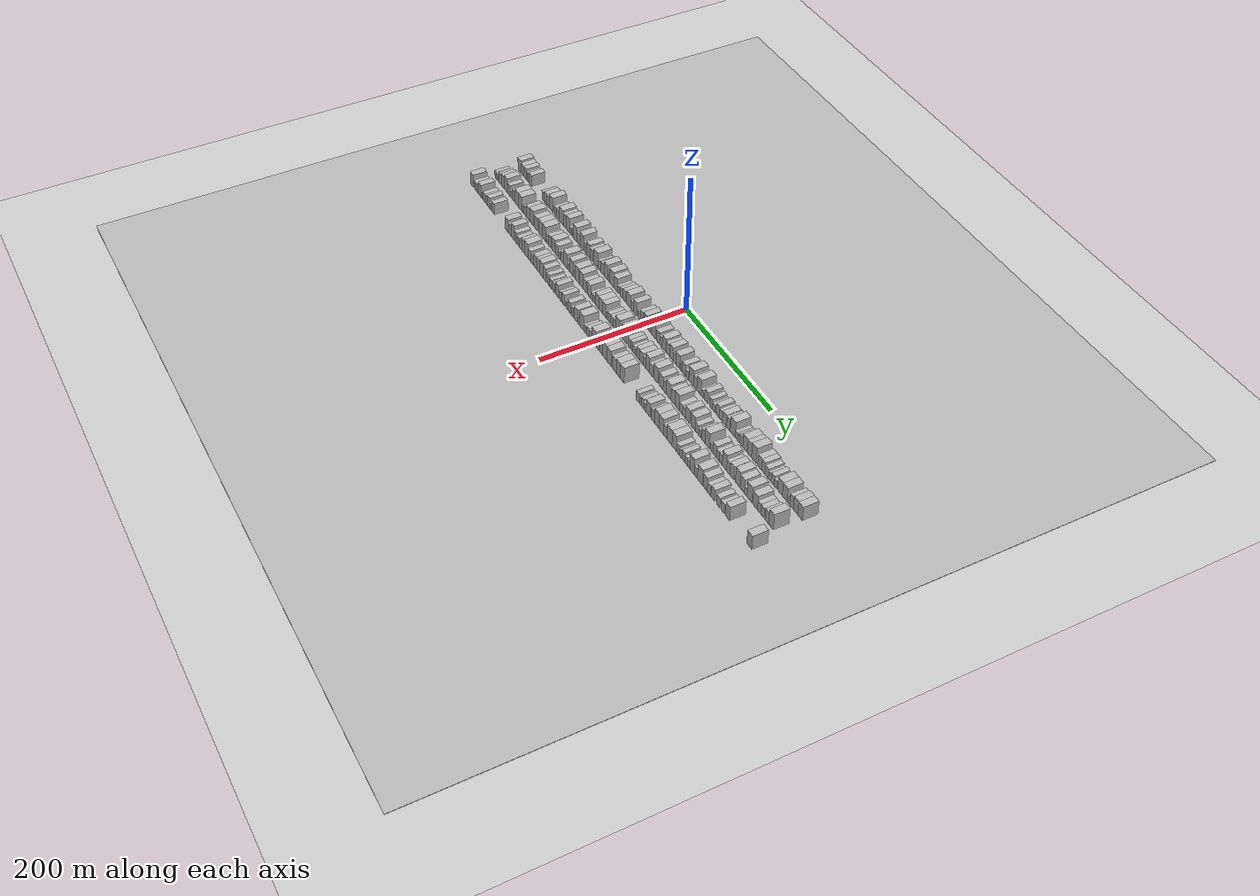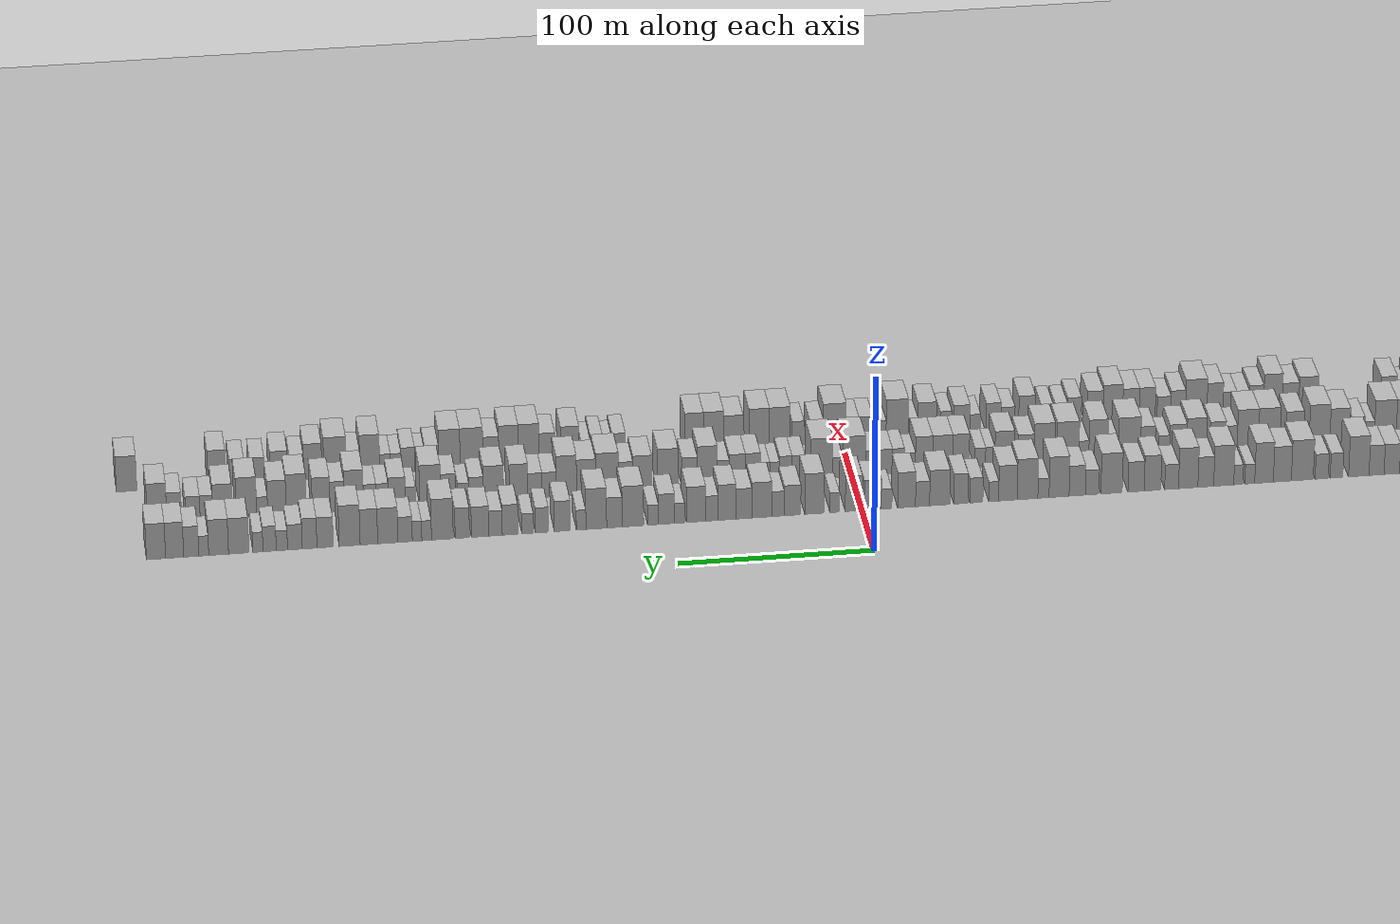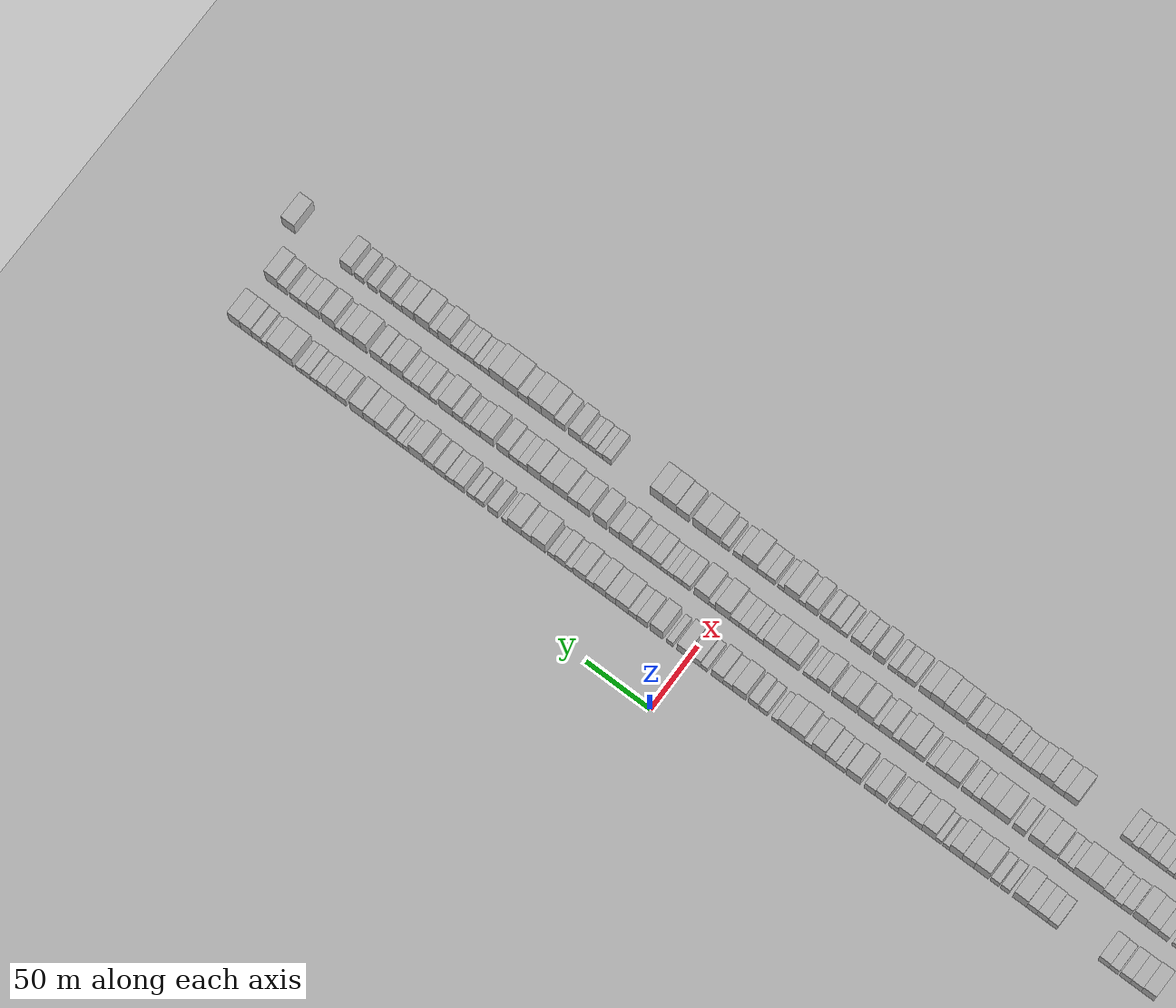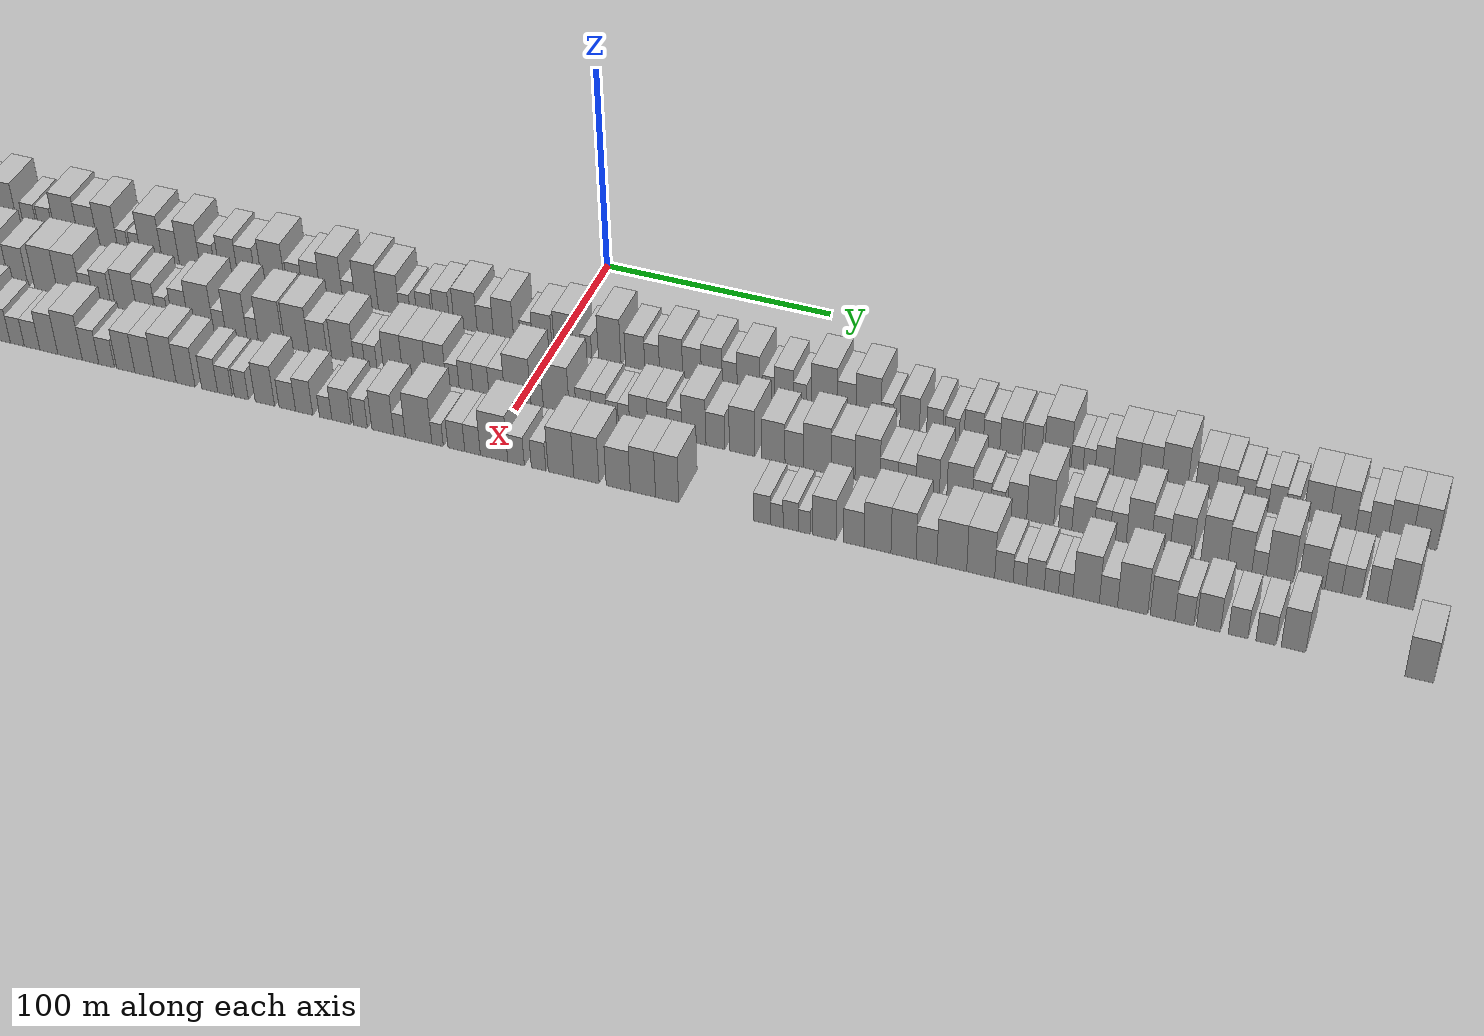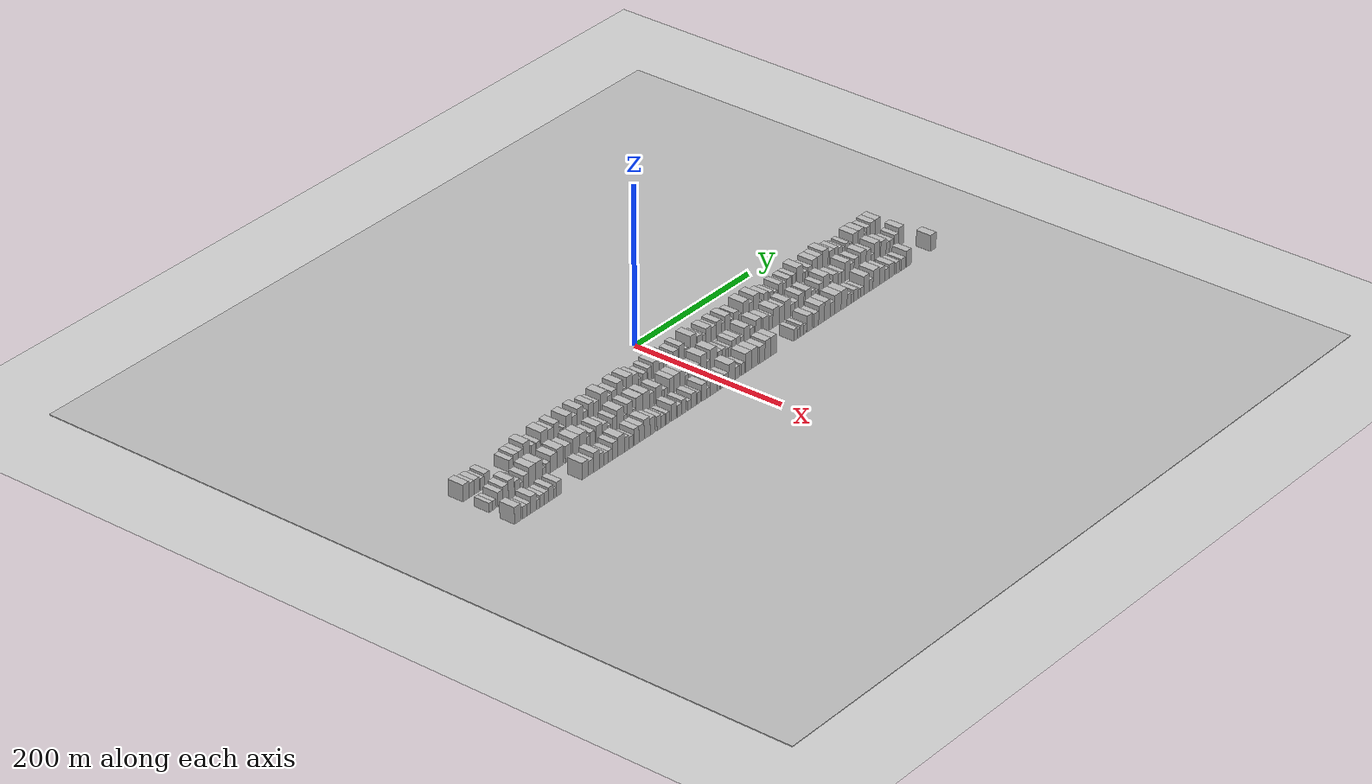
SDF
<?xml version="1.0" encoding="utf-8"?>

<sdf version="1.6">

   <world name="default">

      <gui fullscreen="0">

         <camera name="user_camera">

            <pose>-15 0 4.57585 0 0 0</pose>

            <view_controller>orbit</view_controller>

         </camera>

      </gui>

      <scene>

         <sky>

           <clouds>

             <speed>12</speed>

           </clouds>

         </sky>

         <ambient>0.4 0.4 0.4 1</ambient>

         <background>0.7 0.7 0.7 1</background>

         <shadows>1</shadows>

      </scene>

      <gravity>0 0 -9.8066</gravity>

      <magnetic_field>6e-06 2.3e-05 -4.2e-05</magnetic_field>

      <physics default="0" name="default_physics" type="ode">

         <ode>

            <solver>

               <type>quick</type>

               <iters>10</iters>

               <sor>1.0</sor>

               <use_dynamic_moi_rescaling>0</use_dynamic_moi_rescaling>

            </solver>

            <constraints>

               <cfm>0</cfm>

               <erp>0.2</erp>

               <contact_max_correcting_vel>100</contact_max_correcting_vel>

               <contact_surface_layer>0.001</contact_surface_layer>

            </constraints>

         </ode>

         <max_step_size>0.004</max_step_size>

         <real_time_factor>1</real_time_factor>

         <real_time_update_rate>250</real_time_update_rate>

      </physics>

      <light name="sun" type="directional">

         <cast_shadows>1</cast_shadows>

         <pose>0 0 10 0 0 0</pose>

         <diffuse>0.8 0.8 0.8 1</diffuse>

         <specular>0.2 0.2 0.2 1</specular>

         <attenuation>

            <range>1000</range>

            <constant>0.9</constant>

            <linear>0.01</linear>

            <quadratic>0.001</quadratic>

         </attenuation>

         <direction>-0.5 0.1 -0.9</direction>

      </light>

      <include>

         <name>ground_plane_1</name>

         <uri>model://HANNAS_ground_plane</uri>

         <pose>0 0 0  0 0 0</pose>

      </include>

      <include>

         <name>ground_plane_2</name>

         <uri>model://HANNAS_ground_plane</uri>

         <pose>100 0 0  0 0 0</pose>

      </include>

      <model name="building_1">

         <static>1</static>

         <pose frame="">50.0000 -355.1030 0 0.000000 0.000000 0.000000</pose>

         <link name="link">

            <pose frame="">0 0 10.50 0 0 0</pose>

            <collision name="collision">

               <geometry>

                  <box>

                     <size>20.0000 9.7940 21.0000</size>

                  </box>

               </geometry>

               <max_contacts>10</max_contacts>

               <surface>

                  <contact>

                     <ode/>

                  </contact>

                  <bounce/>

                  <friction>

                     <torsional>

                        <ode/>

                     </torsional>

                     <ode/>

                  </friction>

               </surface>

            </collision>

            <visual name="visual">

               <cast_shadows>0</cast_shadows>

               <geometry>

                  <box>

                     <size>20.0000 9.7940 21.0000</size>

                  </box>

               </geometry>

               <material>

                  <script>

                     <uri>model://HANNAS_wall/materials/scripts</uri>

                     <uri>model://HANNAS_wall/materials/textures</uri>

                     <name>vrc/HANNAS_wall</name>

                  </script>

               </material>

            </visual>

            <self_collide>0</self_collide>

            <enable_wind>0</enable_wind>

            <kinematic>0</kinematic>

         </link>

      </model>

      <model name="building_2">

         <static>1</static>

         <pose frame="">50.0000 -345.9397 0 0.000000 0.000000 0.000000</pose>

         <link name="link">

            <pose frame="">0 0 9.00 0 0 0</pose>

            <collision name="collision">

               <geometry>

                  <box>

                     <size>20.0000 8.5325 18.0000</size>

                  </box>

               </geometry>

               <max_contacts>10</max_contacts>

               <surface>

                  <contact>

                     <ode/>

                  </contact>

                  <bounce/>

                  <friction>

                     <torsional>

                        <ode/>

                     </torsional>

                     <ode/>

                  </friction>

               </surface>

            </collision>

            <visual name="visual">

               <cast_shadows>0</cast_shadows>

               <geometry>

                  <box>

                     <size>20.0000 8.5325 18.0000</size>

                  </box>

               </geometry>

               <material>

                  <script>

                     <uri>model://HANNAS_wall/materials/scripts</uri>

                     <uri>model://HANNAS_wall/materials/textures</uri>

                     <name>vrc/HANNAS_wall</name>

                  </script>

               </material>

            </visual>

            <self_collide>0</self_collide>

            <enable_wind>0</enable_wind>

            <kinematic>0</kinematic>

         </link>

      </model>

      <model name="building_3">

         <static>1</static>

         <pose frame="">50.0000 -337.5042 0 0.000000 0.000000 0.000000</pose>

         <link name="link">

            <pose frame="">0 0 9.00 0 0 0</pose>

            <collision name="collision">

               <geometry>

                  <box>

                     <size>20.0000 8.3385 18.0000</size>

                  </box>

               </geometry>

               <max_contacts>10</max_contacts>

               <surface>

                  <contact>

                     <ode/>

                  </contact>

                  <bounce/>

                  <friction>

                     <torsional>

                        <ode/>

                     </torsional>

                     <ode/>

                  </friction>

               </surface>

            </collision>

            <visual name="visual">

               <cast_shadows>0</cast_shadows>

               <geometry>

                  <box>

                     <size>20.0000 8.3385 18.0000</size>

                  </box>

               </geometry>

               <material>

                  <script>

                     <uri>model://HANNAS_wall/materials/scripts</uri>

                     <uri>model://HANNAS_wall/materials/textures</uri>

                     <name>vrc/HANNAS_wall</name>

                  </script>

               </material>

            </visual>

            <self_collide>0</self_collide>

            <enable_wind>0</enable_wind>

            <kinematic>0</kinematic>

         </link>

      </model>

      <model name="building_4">

         <static>1</static>

         <pose frame="">50.0000 -328.9671 0 0.000000 0.000000 0.000000</pose>

         <link name="link">

            <pose frame="">0 0 7.50 0 0 0</pose>

            <collision name="collision">

               <geometry>

                  <box>

                     <size>20.0000 6.7357 15.0000</size>

                  </box>

               </geometry>

               <max_contacts>10</max_contacts>

               <surface>

                  <contact>

                     <ode/>

                  </contact>

                  <bounce/>

                  <friction>

                     <torsional>

                        <ode/>

                     </torsional>

                     <ode/>

                  </friction>

               </surface>

            </collision>

            <visual name="visual">

               <cast_shadows>0</cast_shadows>

               <geometry>

                  <box>

                     <size>20.0000 6.7357 15.0000</size>

                  </box>

               </geometry>

               <material>

                  <script>

                     <uri>model://HANNAS_wall/materials/scripts</uri>

                     <uri>model://HANNAS_wall/materials/textures</uri>

                     <name>vrc/HANNAS_wall</name>

                  </script>

               </material>

            </visual>

            <self_collide>0</self_collide>

            <enable_wind>0</enable_wind>

            <kinematic>0</kinematic>

         </link>

      </model>

      <model name="building_5">

         <static>1</static>

         <pose frame="">50.0000 -321.3476 0 0.000000 0.000000 0.000000</pose>

         <link name="link">

            <pose frame="">0 0 9.00 0 0 0</pose>

            <collision name="collision">

               <geometry>

                  <box>

                     <size>20.0000 8.5032 18.0000</size>

                  </box>

               </geometry>

               <max_contacts>10</max_contacts>

               <surface>

                  <contact>

                     <ode/>

                  </contact>

                  <bounce/>

                  <friction>

                     <torsional>

                        <ode/>

                     </torsional>

                     <ode/>

                  </friction>

               </surface>

            </collision>

            <visual name="visual">

               <cast_shadows>0</cast_shadows>

               <geometry>

                  <box>

                     <size>20.0000 8.5032 18.0000</size>

                  </box>

               </geometry>

               <material>

                  <script>

                     <uri>model://HANNAS_wall/materials/scripts</uri>

                     <uri>model://HANNAS_wall/materials/textures</uri>

                     <name>vrc/HANNAS_wall</name>

                  </script>

               </material>

            </visual>

            <self_collide>0</self_collide>

            <enable_wind>0</enable_wind>

            <kinematic>0</kinematic>

         </link>

      </model>

      <model name="building_6">

         <static>1</static>

         <pose frame="">50.0000 -281.8934 0 0.000000 0.000000 0.000000</pose>

         <link name="link">

            <pose frame="">0 0 7.50 0 0 0</pose>

            <collision name="collision">

               <geometry>

                  <box>

                     <size>20.0000 7.4684 15.0000</size>

                  </box>

               </geometry>

               <max_contacts>10</max_contacts>

               <surface>

                  <contact>

                     <ode/>

                  </contact>

                  <bounce/>

                  <friction>

                     <torsional>

                        <ode/>

                     </torsional>

                     <ode/>

                  </friction>

               </surface>

            </collision>

            <visual name="visual">

               <cast_shadows>0</cast_shadows>

               <geometry>

                  <box>

                     <size>20.0000 7.4684 15.0000</size>

                  </box>

               </geometry>

               <material>

                  <script>

                     <uri>model://HANNAS_wall/materials/scripts</uri>

                     <uri>model://HANNAS_wall/materials/textures</uri>

                     <name>vrc/HANNAS_wall</name>

                  </script>

               </material>

            </visual>

            <self_collide>0</self_collide>

            <enable_wind>0</enable_wind>

            <kinematic>0</kinematic>

         </link>

      </model>

      <model name="building_7">

         <static>1</static>

         <pose frame="">50.0000 -274.1285 0 0.000000 0.000000 0.000000</pose>

         <link name="link">

            <pose frame="">0 0 9.00 0 0 0</pose>

            <collision name="collision">

               <geometry>

                  <box>

                     <size>20.0000 8.0615 18.0000</size>

                  </box>

               </geometry>

               <max_contacts>10</max_contacts>

               <surface>

                  <contact>

                     <ode/>

                  </contact>

                  <bounce/>

                  <friction>

                     <torsional>

                        <ode/>

                     </torsional>

                     <ode/>

                  </friction>

               </surface>

            </collision>

            <visual name="visual">

               <cast_shadows>0</cast_shadows>

               <geometry>

                  <box>

                     <size>20.0000 8.0615 18.0000</size>

                  </box>

               </geometry>

               <material>

                  <script>

                     <uri>model://HANNAS_wall/materials/scripts</uri>

                     <uri>model://HANNAS_wall/materials/textures</uri>

                     <name>vrc/HANNAS_wall</name>

                  </script>

               </material>

            </visual>

            <self_collide>0</self_collide>

            <enable_wind>0</enable_wind>

            <kinematic>0</kinematic>

         </link>

      </model>

      <model name="building_8">

         <static>1</static>

         <pose frame="">50.0000 -266.1662 0 0.000000 0.000000 0.000000</pose>

         <link name="link">

            <pose frame="">0 0 9.00 0 0 0</pose>

            <collision name="collision">

               <geometry>

                  <box>

                     <size>20.0000 7.8629 18.0000</size>

                  </box>

               </geometry>

               <max_contacts>10</max_contacts>

               <surface>

                  <contact>

                     <ode/>

                  </contact>

                  <bounce/>

                  <friction>

                     <torsional>

                        <ode/>

                     </torsional>

                     <ode/>

                  </friction>

               </surface>

            </collision>

            <visual name="visual">

               <cast_shadows>0</cast_shadows>

               <geometry>

                  <box>

                     <size>20.0000 7.8629 18.0000</size>

                  </box>

               </geometry>

               <material>

                  <script>

                     <uri>model://HANNAS_wall/materials/scripts</uri>

                     <uri>model://HANNAS_wall/materials/textures</uri>

                     <name>vrc/HANNAS_wall</name>

                  </script>

               </material>

            </visual>

            <self_collide>0</self_collide>

            <enable_wind>0</enable_wind>

            <kinematic>0</kinematic>

         </link>

      </model>

      <model name="building_9">

         <static>1</static>

         <pose frame="">50.0000 -256.8970 0 0.000000 0.000000 0.000000</pose>

         <link name="link">

            <pose frame="">0 0 12.00 0 0 0</pose>

            <collision name="collision">

               <geometry>

                  <box>

                     <size>20.0000 10.6755 24.0000</size>

                  </box>

               </geometry>

               <max_contacts>10</max_contacts>

               <surface>

                  <contact>

                     <ode/>

                  </contact>

                  <bounce/>

                  <friction>

                     <torsional>

                        <ode/>

                     </torsional>

                     <ode/>

                  </friction>

               </surface>

            </collision>

            <visual name="visual">

               <cast_shadows>0</cast_shadows>

               <geometry>

                  <box>

                     <size>20.0000 10.6755 24.0000</size>

                  </box>

               </geometry>

               <material>

                  <script>

                     <uri>model://HANNAS_wall/materials/scripts</uri>

                     <uri>model://HANNAS_wall/materials/textures</uri>

                     <name>vrc/HANNAS_wall</name>

                  </script>

               </material>

            </visual>

            <self_collide>0</self_collide>

            <enable_wind>0</enable_wind>

            <kinematic>0</kinematic>

         </link>

      </model>

      <model name="building_10">

         <static>1</static>

         <pose frame="">50.0000 -245.2626 0 0.000000 0.000000 0.000000</pose>

         <link name="link">

            <pose frame="">0 0 7.50 0 0 0</pose>

            <collision name="collision">

               <geometry>

                  <box>

                     <size>20.0000 6.5934 15.0000</size>

                  </box>

               </geometry>

               <max_contacts>10</max_contacts>

               <surface>

                  <contact>

                     <ode/>

                  </contact>

                  <bounce/>

                  <friction>

                     <torsional>

                        <ode/>

                     </torsional>

                     <ode/>

                  </friction>

               </surface>

            </collision>

            <visual name="visual">

               <cast_shadows>0</cast_shadows>

               <geometry>

                  <box>

                     <size>20.0000 6.5934 15.0000</size>

                  </box>

               </geometry>

               <material>

                  <script>

                     <uri>model://HANNAS_wall/materials/scripts</uri>

                     <uri>model://HANNAS_wall/materials/textures</uri>

                     <name>vrc/HANNAS_wall</name>

                  </script>

               </material>

            </visual>

            <self_collide>0</self_collide>

            <enable_wind>0</enable_wind>

            <kinematic>0</kinematic>

         </link>

      </model>

      <model name="building_11">

         <static>1</static>

         <pose frame="">50.0000 -237.5279 0 0.000000 0.000000 0.000000</pose>

         <link name="link">

            <pose frame="">0 0 7.50 0 0 0</pose>

            <collision name="collision">

               <geometry>

                  <box>

                     <size>20.0000 6.8759 15.0000</size>

                  </box>

               </geometry>

               <max_contacts>10</max_contacts>

               <surface>

                  <contact>

                     <ode/>

                  </contact>

                  <bounce/>

                  <friction>

                     <torsional>

                        <ode/>

                     </torsional>

                     <ode/>

                  </friction>

               </surface>

            </collision>

            <visual name="visual">

               <cast_shadows>0</cast_shadows>

               <geometry>

                  <box>

                     <size>20.0000 6.8759 15.0000</size>

                  </box>

               </geometry>

               <material>

                  <script>

                     <uri>model://HANNAS_wall/materials/scripts</uri>

                     <uri>model://HANNAS_wall/materials/textures</uri>

                     <name>vrc/HANNAS_wall</name>

                  </script>

               </material>

            </visual>

            <self_collide>0</self_collide>

            <enable_wind>0</enable_wind>

            <kinematic>0</kinematic>

         </link>

      </model>

      <model name="building_12">

         <static>1</static>

         <pose frame="">50.0000 -227.3818 0 0.000000 0.000000 0.000000</pose>

         <link name="link">

            <pose frame="">0 0 12.00 0 0 0</pose>

            <collision name="collision">

               <geometry>

                  <box>

                     <size>20.0000 11.4164 24.0000</size>

                  </box>

               </geometry>

               <max_contacts>10</max_contacts>

               <surface>

                  <contact>

                     <ode/>

                  </contact>

                  <bounce/>

                  <friction>

                     <torsional>

                        <ode/>

                     </torsional>

                     <ode/>

                  </friction>

               </surface>

            </collision>

            <visual name="visual">

               <cast_shadows>0</cast_shadows>

               <geometry>

                  <box>

                     <size>20.0000 11.4164 24.0000</size>

                  </box>

               </geometry>

               <material>

                  <script>

                     <uri>model://HANNAS_wall/materials/scripts</uri>

                     <uri>model://HANNAS_wall/materials/textures</uri>

                     <name>vrc/HANNAS_wall</name>

                  </script>

               </material>

            </visual>

            <self_collide>0</self_collide>

            <enable_wind>0</enable_wind>

            <kinematic>0</kinematic>

         </link>

      </model>

      <model name="building_13">

         <static>1</static>

         <pose frame="">50.0000 -216.9824 0 0.000000 0.000000 0.000000</pose>

         <link name="link">

            <pose frame="">0 0 10.50 0 0 0</pose>

            <collision name="collision">

               <geometry>

                  <box>

                     <size>20.0000 9.3823 21.0000</size>

                  </box>

               </geometry>

               <max_contacts>10</max_contacts>

               <surface>

                  <contact>

                     <ode/>

                  </contact>

                  <bounce/>

                  <friction>

                     <torsional>

                        <ode/>

                     </torsional>

                     <ode/>

                  </friction>

               </surface>

            </collision>

            <visual name="visual">

               <cast_shadows>0</cast_shadows>

               <geometry>

                  <box>

                     <size>20.0000 9.3823 21.0000</size>

                  </box>

               </geometry>

               <material>

                  <script>

                     <uri>model://HANNAS_wall/materials/scripts</uri>

                     <uri>model://HANNAS_wall/materials/textures</uri>

                     <name>vrc/HANNAS_wall</name>

                  </script>

               </material>

            </visual>

            <self_collide>0</self_collide>

            <enable_wind>0</enable_wind>

            <kinematic>0</kinematic>

         </link>

      </model>

      <model name="building_14">

         <static>1</static>

         <pose frame="">50.0000 -207.4334 0 0.000000 0.000000 0.000000</pose>

         <link name="link">

            <pose frame="">0 0 12.00 0 0 0</pose>

            <collision name="collision">

               <geometry>

                  <box>

                     <size>20.0000 9.7157 24.0000</size>

                  </box>

               </geometry>

               <max_contacts>10</max_contacts>

               <surface>

                  <contact>

                     <ode/>

                  </contact>

                  <bounce/>

                  <friction>

                     <torsional>

                        <ode/>

                     </torsional>

                     <ode/>

                  </friction>

               </surface>

            </collision>

            <visual name="visual">

               <cast_shadows>0</cast_shadows>

               <geometry>

                  <box>

                     <size>20.0000 9.7157 24.0000</size>

                  </box>

               </geometry>

               <material>

                  <script>

                     <uri>model://HANNAS_wall/materials/scripts</uri>

                     <uri>model://HANNAS_wall/materials/textures</uri>

                     <name>vrc/HANNAS_wall</name>

                  </script>

               </material>

            </visual>

            <self_collide>0</self_collide>

            <enable_wind>0</enable_wind>

            <kinematic>0</kinematic>

         </link>

      </model>

      <model name="building_15">

         <static>1</static>

         <pose frame="">50.0000 -200.0205 0 0.000000 0.000000 0.000000</pose>

         <link name="link">

            <pose frame="">0 0 6.00 0 0 0</pose>

            <collision name="collision">

               <geometry>

                  <box>

                     <size>20.0000 5.1102 12.0000</size>

                  </box>

               </geometry>

               <max_contacts>10</max_contacts>

               <surface>

                  <contact>

                     <ode/>

                  </contact>

                  <bounce/>

                  <friction>

                     <torsional>

                        <ode/>

                     </torsional>

                     <ode/>

                  </friction>

               </surface>

            </collision>

            <visual name="visual">

               <cast_shadows>0</cast_shadows>

               <geometry>

                  <box>

                     <size>20.0000 5.1102 12.0000</size>

                  </box>

               </geometry>

               <material>

                  <script>

                     <uri>model://HANNAS_wall/materials/scripts</uri>

                     <uri>model://HANNAS_wall/materials/textures</uri>

                     <name>vrc/HANNAS_wall</name>

                  </script>

               </material>

            </visual>

            <self_collide>0</self_collide>

            <enable_wind>0</enable_wind>

            <kinematic>0</kinematic>

         </link>

      </model>

      <model name="building_16">

         <static>1</static>

         <pose frame="">50.0000 -194.0654 0 0.000000 0.000000 0.000000</pose>

         <link name="link">

            <pose frame="">0 0 6.00 0 0 0</pose>

            <collision name="collision">

               <geometry>

                  <box>

                     <size>20.0000 4.8000 12.0000</size>

                  </box>

               </geometry>

               <max_contacts>10</max_contacts>

               <surface>

                  <contact>

                     <ode/>

                  </contact>

                  <bounce/>

                  <friction>

                     <torsional>

                        <ode/>

                     </torsional>

                     <ode/>

                  </friction>

               </surface>

            </collision>

            <visual name="visual">

               <cast_shadows>0</cast_shadows>

               <geometry>

                  <box>

                     <size>20.0000 4.8000 12.0000</size>

                  </box>

               </geometry>

               <material>

                  <script>

                     <uri>model://HANNAS_wall/materials/scripts</uri>

                     <uri>model://HANNAS_wall/materials/textures</uri>

                     <name>vrc/HANNAS_wall</name>

                  </script>

               </material>

            </visual>

            <self_collide>0</self_collide>

            <enable_wind>0</enable_wind>

            <kinematic>0</kinematic>

         </link>

      </model>

      <model name="building_17">

         <static>1</static>

         <pose frame="">50.0000 -186.4469 0 0.000000 0.000000 0.000000</pose>

         <link name="link">

            <pose frame="">0 0 12.00 0 0 0</pose>

            <collision name="collision">

               <geometry>

                  <box>

                     <size>20.0000 10.4369 24.0000</size>

                  </box>

               </geometry>

               <max_contacts>10</max_contacts>

               <surface>

                  <contact>

                     <ode/>

                  </contact>

                  <bounce/>

                  <friction>

                     <torsional>

                        <ode/>

                     </torsional>

                     <ode/>

                  </friction>

               </surface>

            </collision>

            <visual name="visual">

               <cast_shadows>0</cast_shadows>

               <geometry>

                  <box>

                     <size>20.0000 10.4369 24.0000</size>

                  </box>

               </geometry>

               <material>

                  <script>

                     <uri>model://HANNAS_wall/materials/scripts</uri>

                     <uri>model://HANNAS_wall/materials/textures</uri>

                     <name>vrc/HANNAS_wall</name>

                  </script>

               </material>

            </visual>

            <self_collide>0</self_collide>

            <enable_wind>0</enable_wind>

            <kinematic>0</kinematic>

         </link>

      </model>

      <model name="building_18">

         <static>1</static>

         <pose frame="">50.0000 -177.1281 0 0.000000 0.000000 0.000000</pose>

         <link name="link">

            <pose frame="">0 0 9.00 0 0 0</pose>

            <collision name="collision">

               <geometry>

                  <box>

                     <size>20.0000 8.2006 18.0000</size>

                  </box>

               </geometry>

               <max_contacts>10</max_contacts>

               <surface>

                  <contact>

                     <ode/>

                  </contact>

                  <bounce/>

                  <friction>

                     <torsional>

                        <ode/>

                     </torsional>

                     <ode/>

                  </friction>

               </surface>

            </collision>

            <visual name="visual">

               <cast_shadows>0</cast_shadows>

               <geometry>

                  <box>

                     <size>20.0000 8.2006 18.0000</size>

                  </box>

               </geometry>

               <material>

                  <script>

                     <uri>model://HANNAS_wall/materials/scripts</uri>

                     <uri>model://HANNAS_wall/materials/textures</uri>

                     <name>vrc/HANNAS_wall</name>

                  </script>

               </material>

            </visual>

            <self_collide>0</self_collide>

            <enable_wind>0</enable_wind>

            <kinematic>0</kinematic>

         </link>

      </model>

      <model name="building_19">

         <static>1</static>

         <pose frame="">50.0000 -167.9852 0 0.000000 0.000000 0.000000</pose>

         <link name="link">

            <pose frame="">0 0 12.00 0 0 0</pose>

            <collision name="collision">

               <geometry>

                  <box>

                     <size>20.0000 10.0853 24.0000</size>

                  </box>

               </geometry>

               <max_contacts>10</max_contacts>

               <surface>

                  <contact>

                     <ode/>

                  </contact>

                  <bounce/>

                  <friction>

                     <torsional>

                        <ode/>

                     </torsional>

                     <ode/>

                  </friction>

               </surface>

            </collision>

            <visual name="visual">

               <cast_shadows>0</cast_shadows>

               <geometry>

                  <box>

                     <size>20.0000 10.0853 24.0000</size>

                  </box>

               </geometry>

               <material>

                  <script>

                     <uri>model://HANNAS_wall/materials/scripts</uri>

                     <uri>model://HANNAS_wall/materials/textures</uri>

                     <name>vrc/HANNAS_wall</name>

                  </script>

               </material>

            </visual>

            <self_collide>0</self_collide>

            <enable_wind>0</enable_wind>

            <kinematic>0</kinematic>

         </link>

      </model>

      <model name="building_20">

         <static>1</static>

         <pose frame="">50.0000 -159.3346 0 0.000000 0.000000 0.000000</pose>

         <link name="link">

            <pose frame="">0 0 7.50 0 0 0</pose>

            <collision name="collision">

               <geometry>

                  <box>

                     <size>20.0000 7.2160 15.0000</size>

                  </box>

               </geometry>

               <max_contacts>10</max_contacts>

               <surface>

                  <contact>

                     <ode/>

                  </contact>

                  <bounce/>

                  <friction>

                     <torsional>

                        <ode/>

                     </torsional>

                     <ode/>

                  </friction>

               </surface>

            </collision>

            <visual name="visual">

               <cast_shadows>0</cast_shadows>

               <geometry>

                  <box>

                     <size>20.0000 7.2160 15.0000</size>

                  </box>

               </geometry>

               <material>

                  <script>

                     <uri>model://HANNAS_wall/materials/scripts</uri>

                     <uri>model://HANNAS_wall/materials/textures</uri>

                     <name>vrc/HANNAS_wall</name>

                  </script>

               </material>

            </visual>

            <self_collide>0</self_collide>

            <enable_wind>0</enable_wind>

            <kinematic>0</kinematic>

         </link>

      </model>

      <model name="building_21">

         <static>1</static>

         <pose frame="">50.0000 -149.4013 0 0.000000 0.000000 0.000000</pose>

         <link name="link">

            <pose frame="">0 0 10.50 0 0 0</pose>

            <collision name="collision">

               <geometry>

                  <box>

                     <size>20.0000 8.6504 21.0000</size>

                  </box>

               </geometry>

               <max_contacts>10</max_contacts>

               <surface>

                  <contact>

                     <ode/>

                  </contact>

                  <bounce/>

                  <friction>

                     <torsional>

                        <ode/>

                     </torsional>

                     <ode/>

                  </friction>

               </surface>

            </collision>

            <visual name="visual">

               <cast_shadows>0</cast_shadows>

               <geometry>

                  <box>

                     <size>20.0000 8.6504 21.0000</size>

                  </box>

               </geometry>

               <material>

                  <script>

                     <uri>model://HANNAS_wall/materials/scripts</uri>

                     <uri>model://HANNAS_wall/materials/textures</uri>

                     <name>vrc/HANNAS_wall</name>

                  </script>

               </material>

            </visual>

            <self_collide>0</self_collide>

            <enable_wind>0</enable_wind>

            <kinematic>0</kinematic>

         </link>

      </model>

      <model name="building_22">

         <static>1</static>

         <pose frame="">50.0000 -140.8752 0 0.000000 0.000000 0.000000</pose>

         <link name="link">

            <pose frame="">0 0 9.00 0 0 0</pose>

            <collision name="collision">

               <geometry>

                  <box>

                     <size>20.0000 8.4019 18.0000</size>

                  </box>

               </geometry>

               <max_contacts>10</max_contacts>

               <surface>

                  <contact>

                     <ode/>

                  </contact>

                  <bounce/>

                  <friction>

                     <torsional>

                        <ode/>

                     </torsional>

                     <ode/>

                  </friction>

               </surface>

            </collision>

            <visual name="visual">

               <cast_shadows>0</cast_shadows>

               <geometry>

                  <box>

                     <size>20.0000 8.4019 18.0000</size>

                  </box>

               </geometry>

               <material>

                  <script>

                     <uri>model://HANNAS_wall/materials/scripts</uri>

                     <uri>model://HANNAS_wall/materials/textures</uri>

                     <name>vrc/HANNAS_wall</name>

                  </script>

               </material>

            </visual>

            <self_collide>0</self_collide>

            <enable_wind>0</enable_wind>

            <kinematic>0</kinematic>

         </link>

      </model>

      <model name="building_23">

         <static>1</static>

         <pose frame="">50.0000 -128.1506 0 0.000000 0.000000 0.000000</pose>

         <link name="link">

            <pose frame="">0 0 12.00 0 0 0</pose>

            <collision name="collision">

               <geometry>

                  <box>

                     <size>20.0000 11.0474 24.0000</size>

                  </box>

               </geometry>

               <max_contacts>10</max_contacts>

               <surface>

                  <contact>

                     <ode/>

                  </contact>

                  <bounce/>

                  <friction>

                     <torsional>

                        <ode/>

                     </torsional>

                     <ode/>

                  </friction>

               </surface>

            </collision>

            <visual name="visual">

               <cast_shadows>0</cast_shadows>

               <geometry>

                  <box>

                     <size>20.0000 11.0474 24.0000</size>

                  </box>

               </geometry>

               <material>

                  <script>

                     <uri>model://HANNAS_wall/materials/scripts</uri>

                     <uri>model://HANNAS_wall/materials/textures</uri>

                     <name>vrc/HANNAS_wall</name>

                  </script>

               </material>

            </visual>

            <self_collide>0</self_collide>

            <enable_wind>0</enable_wind>

            <kinematic>0</kinematic>

         </link>

      </model>

      <model name="building_24">

         <static>1</static>

         <pose frame="">50.0000 -118.1010 0 0.000000 0.000000 0.000000</pose>

         <link name="link">

            <pose frame="">0 0 7.50 0 0 0</pose>

            <collision name="collision">

               <geometry>

                  <box>

                     <size>20.0000 7.0517 15.0000</size>

                  </box>

               </geometry>

               <max_contacts>10</max_contacts>

               <surface>

                  <contact>

                     <ode/>

                  </contact>

                  <bounce/>

                  <friction>

                     <torsional>

                        <ode/>

                     </torsional>

                     <ode/>

                  </friction>

               </surface>

            </collision>

            <visual name="visual">

               <cast_shadows>0</cast_shadows>

               <geometry>

                  <box>

                     <size>20.0000 7.0517 15.0000</size>

                  </box>

               </geometry>

               <material>

                  <script>

                     <uri>model://HANNAS_wall/materials/scripts</uri>

                     <uri>model://HANNAS_wall/materials/textures</uri>

                     <name>vrc/HANNAS_wall</name>

                  </script>

               </material>

            </visual>

            <self_collide>0</self_collide>

            <enable_wind>0</enable_wind>

            <kinematic>0</kinematic>

         </link>

      </model>

      <model name="building_25">

         <static>1</static>

         <pose frame="">50.0000 -110.3746 0 0.000000 0.000000 0.000000</pose>

         <link name="link">

            <pose frame="">0 0 9.00 0 0 0</pose>

            <collision name="collision">

               <geometry>

                  <box>

                     <size>20.0000 8.4012 18.0000</size>

                  </box>

               </geometry>

               <max_contacts>10</max_contacts>

               <surface>

                  <contact>

                     <ode/>

                  </contact>

                  <bounce/>

                  <friction>

                     <torsional>

                        <ode/>

                     </torsional>

                     <ode/>

                  </friction>

               </surface>

            </collision>

            <visual name="visual">

               <cast_shadows>0</cast_shadows>

               <geometry>

                  <box>

                     <size>20.0000 8.4012 18.0000</size>

                  </box>

               </geometry>

               <material>

                  <script>

                     <uri>model://HANNAS_wall/materials/scripts</uri>

                     <uri>model://HANNAS_wall/materials/textures</uri>

                     <name>vrc/HANNAS_wall</name>

                  </script>

               </material>

            </visual>

            <self_collide>0</self_collide>

            <enable_wind>0</enable_wind>

            <kinematic>0</kinematic>

         </link>

      </model>

      <model name="building_26">

         <static>1</static>

         <pose frame="">50.0000 -100.9878 0 0.000000 0.000000 0.000000</pose>

         <link name="link">

            <pose frame="">0 0 12.00 0 0 0</pose>

            <collision name="collision">

               <geometry>

                  <box>

                     <size>20.0000 10.3724 24.0000</size>

                  </box>

               </geometry>

               <max_contacts>10</max_contacts>

               <surface>

                  <contact>

                     <ode/>

                  </contact>

                  <bounce/>

                  <friction>

                     <torsional>

                        <ode/>

                     </torsional>

                     <ode/>

                  </friction>

               </surface>

            </collision>

            <visual name="visual">

               <cast_shadows>0</cast_shadows>

               <geometry>

                  <box>

                     <size>20.0000 10.3724 24.0000</size>

                  </box>

               </geometry>

               <material>

                  <script>

                     <uri>model://HANNAS_wall/materials/scripts</uri>

                     <uri>model://HANNAS_wall/materials/textures</uri>

                     <name>vrc/HANNAS_wall</name>

                  </script>

               </material>

            </visual>

            <self_collide>0</self_collide>

            <enable_wind>0</enable_wind>

            <kinematic>0</kinematic>

         </link>

      </model>

      <model name="building_27">

         <static>1</static>

         <pose frame="">50.0000 -92.8949 0 0.000000 0.000000 0.000000</pose>

         <link name="link">

            <pose frame="">0 0 6.00 0 0 0</pose>

            <collision name="collision">

               <geometry>

                  <box>

                     <size>20.0000 5.8134 12.0000</size>

                  </box>

               </geometry>

               <max_contacts>10</max_contacts>

               <surface>

                  <contact>

                     <ode/>

                  </contact>

                  <bounce/>

                  <friction>

                     <torsional>

                        <ode/>

                     </torsional>

                     <ode/>

                  </friction>

               </surface>

            </collision>

            <visual name="visual">

               <cast_shadows>0</cast_shadows>

               <geometry>

                  <box>

                     <size>20.0000 5.8134 12.0000</size>

                  </box>

               </geometry>

               <material>

                  <script>

                     <uri>model://HANNAS_wall/materials/scripts</uri>

                     <uri>model://HANNAS_wall/materials/textures</uri>

                     <name>vrc/HANNAS_wall</name>

                  </script>

               </material>

            </visual>

            <self_collide>0</self_collide>

            <enable_wind>0</enable_wind>

            <kinematic>0</kinematic>

         </link>

      </model>

      <model name="building_28">

         <static>1</static>

         <pose frame="">50.0000 -84.6615 0 0.000000 0.000000 0.000000</pose>

         <link name="link">

            <pose frame="">0 0 12.00 0 0 0</pose>

            <collision name="collision">

               <geometry>

                  <box>

                     <size>20.0000 10.6533 24.0000</size>

                  </box>

               </geometry>

               <max_contacts>10</max_contacts>

               <surface>

                  <contact>

                     <ode/>

                  </contact>

                  <bounce/>

                  <friction>

                     <torsional>

                        <ode/>

                     </torsional>

                     <ode/>

                  </friction>

               </surface>

            </collision>

            <visual name="visual">

               <cast_shadows>0</cast_shadows>

               <geometry>

                  <box>

                     <size>20.0000 10.6533 24.0000</size>

                  </box>

               </geometry>

               <material>

                  <script>

                     <uri>model://HANNAS_wall/materials/scripts</uri>

                     <uri>model://HANNAS_wall/materials/textures</uri>

                     <name>vrc/HANNAS_wall</name>

                  </script>

               </material>

            </visual>

            <self_collide>0</self_collide>

            <enable_wind>0</enable_wind>

            <kinematic>0</kinematic>

         </link>

      </model>

      <model name="building_29">

         <static>1</static>

         <pose frame="">50.0000 -74.5359 0 0.000000 0.000000 0.000000</pose>

         <link name="link">

            <pose frame="">0 0 10.50 0 0 0</pose>

            <collision name="collision">

               <geometry>

                  <box>

                     <size>20.0000 9.5979 21.0000</size>

                  </box>

               </geometry>

               <max_contacts>10</max_contacts>

               <surface>

                  <contact>

                     <ode/>

                  </contact>

                  <bounce/>

                  <friction>

                     <torsional>

                        <ode/>

                     </torsional>

                     <ode/>

                  </friction>

               </surface>

            </collision>

            <visual name="visual">

               <cast_shadows>0</cast_shadows>

               <geometry>

                  <box>

                     <size>20.0000 9.5979 21.0000</size>

                  </box>

               </geometry>

               <material>

                  <script>

                     <uri>model://HANNAS_wall/materials/scripts</uri>

                     <uri>model://HANNAS_wall/materials/textures</uri>

                     <name>vrc/HANNAS_wall</name>

                  </script>

               </material>

            </visual>

            <self_collide>0</self_collide>

            <enable_wind>0</enable_wind>

            <kinematic>0</kinematic>

         </link>

      </model>

      <model name="building_30">

         <static>1</static>

         <pose frame="">50.0000 -67.1546 0 0.000000 0.000000 0.000000</pose>

         <link name="link">

            <pose frame="">0 0 6.00 0 0 0</pose>

            <collision name="collision">

               <geometry>

                  <box>

                     <size>20.0000 5.1647 12.0000</size>

                  </box>

               </geometry>

               <max_contacts>10</max_contacts>

               <surface>

                  <contact>

                     <ode/>

                  </contact>

                  <bounce/>

                  <friction>

                     <torsional>

                        <ode/>

                     </torsional>

                     <ode/>

                  </friction>

               </surface>

            </collision>

            <visual name="visual">

               <cast_shadows>0</cast_shadows>

               <geometry>

                  <box>

                     <size>20.0000 5.1647 12.0000</size>

                  </box>

               </geometry>

               <material>

                  <script>

                     <uri>model://HANNAS_wall/materials/scripts</uri>

                     <uri>model://HANNAS_wall/materials/textures</uri>

                     <name>vrc/HANNAS_wall</name>

                  </script>

               </material>

            </visual>

            <self_collide>0</self_collide>

            <enable_wind>0</enable_wind>

            <kinematic>0</kinematic>

         </link>

      </model>

      <model name="building_31">

         <static>1</static>

         <pose frame="">50.0000 -58.2262 0 0.000000 0.000000 0.000000</pose>

         <link name="link">

            <pose frame="">0 0 7.50 0 0 0</pose>

            <collision name="collision">

               <geometry>

                  <box>

                     <size>20.0000 6.6921 15.0000</size>

                  </box>

               </geometry>

               <max_contacts>10</max_contacts>

               <surface>

                  <contact>

                     <ode/>

                  </contact>

                  <bounce/>

                  <friction>

                     <torsional>

                        <ode/>

                     </torsional>

                     <ode/>

                  </friction>

               </surface>

            </collision>

            <visual name="visual">

               <cast_shadows>0</cast_shadows>

               <geometry>

                  <box>

                     <size>20.0000 6.6921 15.0000</size>

                  </box>

               </geometry>

               <material>

                  <script>

                     <uri>model://HANNAS_wall/materials/scripts</uri>

                     <uri>model://HANNAS_wall/materials/textures</uri>

                     <name>vrc/HANNAS_wall</name>

                  </script>

               </material>

            </visual>

            <self_collide>0</self_collide>

            <enable_wind>0</enable_wind>

            <kinematic>0</kinematic>

         </link>

      </model>

      <model name="building_32">

         <static>1</static>

         <pose frame="">50.0000 -50.2246 0 0.000000 0.000000 0.000000</pose>

         <link name="link">

            <pose frame="">0 0 9.00 0 0 0</pose>

            <collision name="collision">

               <geometry>

                  <box>

                     <size>20.0000 7.3111 18.0000</size>

                  </box>

               </geometry>

               <max_contacts>10</max_contacts>

               <surface>

                  <contact>

                     <ode/>

                  </contact>

                  <bounce/>

                  <friction>

                     <torsional>

                        <ode/>

                     </torsional>

                     <ode/>

                  </friction>

               </surface>

            </collision>

            <visual name="visual">

               <cast_shadows>0</cast_shadows>

               <geometry>

                  <box>

                     <size>20.0000 7.3111 18.0000</size>

                  </box>

               </geometry>

               <material>

                  <script>

                     <uri>model://HANNAS_wall/materials/scripts</uri>

                     <uri>model://HANNAS_wall/materials/textures</uri>

                     <name>vrc/HANNAS_wall</name>

                  </script>

               </material>

            </visual>

            <self_collide>0</self_collide>

            <enable_wind>0</enable_wind>

            <kinematic>0</kinematic>

         </link>

      </model>

      <model name="building_33">

         <static>1</static>

         <pose frame="">50.0000 -39.3509 0 0.000000 0.000000 0.000000</pose>

         <link name="link">

            <pose frame="">0 0 10.50 0 0 0</pose>

            <collision name="collision">

               <geometry>

                  <box>

                     <size>20.0000 10.4364 21.0000</size>

                  </box>

               </geometry>

               <max_contacts>10</max_contacts>

               <surface>

                  <contact>

                     <ode/>

                  </contact>

                  <bounce/>

                  <friction>

                     <torsional>

                        <ode/>

                     </torsional>

                     <ode/>

                  </friction>

               </surface>

            </collision>

            <visual name="visual">

               <cast_shadows>0</cast_shadows>

               <geometry>

                  <box>

                     <size>20.0000 10.4364 21.0000</size>

                  </box>

               </geometry>

               <material>

                  <script>

                     <uri>model://HANNAS_wall/materials/scripts</uri>

                     <uri>model://HANNAS_wall/materials/textures</uri>

                     <name>vrc/HANNAS_wall</name>

                  </script>

               </material>

            </visual>

            <self_collide>0</self_collide>

            <enable_wind>0</enable_wind>

            <kinematic>0</kinematic>

         </link>

      </model>

      <model name="building_34">

         <static>1</static>

         <pose frame="">50.0000 -30.4850 0 0.000000 0.000000 0.000000</pose>

         <link name="link">

            <pose frame="">0 0 7.50 0 0 0</pose>

            <collision name="collision">

               <geometry>

                  <box>

                     <size>20.0000 7.2954 15.0000</size>

                  </box>

               </geometry>

               <max_contacts>10</max_contacts>

               <surface>

                  <contact>

                     <ode/>

                  </contact>

                  <bounce/>

                  <friction>

                     <torsional>

                        <ode/>

                     </torsional>

                     <ode/>

                  </friction>

               </surface>

            </collision>

            <visual name="visual">

               <cast_shadows>0</cast_shadows>

               <geometry>

                  <box>

                     <size>20.0000 7.2954 15.0000</size>

                  </box>

               </geometry>

               <material>

                  <script>

                     <uri>model://HANNAS_wall/materials/scripts</uri>

                     <uri>model://HANNAS_wall/materials/textures</uri>

                     <name>vrc/HANNAS_wall</name>

                  </script>

               </material>

            </visual>

            <self_collide>0</self_collide>

            <enable_wind>0</enable_wind>

            <kinematic>0</kinematic>

         </link>

      </model>

      <model name="building_35">

         <static>1</static>

         <pose frame="">50.0000 -22.2513 0 0.000000 0.000000 0.000000</pose>

         <link name="link">

            <pose frame="">0 0 10.50 0 0 0</pose>

            <collision name="collision">

               <geometry>

                  <box>

                     <size>20.0000 9.1720 21.0000</size>

                  </box>

               </geometry>

               <max_contacts>10</max_contacts>

               <surface>

                  <contact>

                     <ode/>

                  </contact>

                  <bounce/>

                  <friction>

                     <torsional>

                        <ode/>

                     </torsional>

                     <ode/>

                  </friction>

               </surface>

            </collision>

            <visual name="visual">

               <cast_shadows>0</cast_shadows>

               <geometry>

                  <box>

                     <size>20.0000 9.1720 21.0000</size>

                  </box>

               </geometry>

               <material>

                  <script>

                     <uri>model://HANNAS_wall/materials/scripts</uri>

                     <uri>model://HANNAS_wall/materials/textures</uri>

                     <name>vrc/HANNAS_wall</name>

                  </script>

               </material>

            </visual>

            <self_collide>0</self_collide>

            <enable_wind>0</enable_wind>

            <kinematic>0</kinematic>

         </link>

      </model>

      <model name="building_36">

         <static>1</static>

         <pose frame="">50.0000 -11.9494 0 0.000000 0.000000 0.000000</pose>

         <link name="link">

            <pose frame="">0 0 6.00 0 0 0</pose>

            <collision name="collision">

               <geometry>

                  <box>

                     <size>20.0000 5.4317 12.0000</size>

                  </box>

               </geometry>

               <max_contacts>10</max_contacts>

               <surface>

                  <contact>

                     <ode/>

                  </contact>

                  <bounce/>

                  <friction>

                     <torsional>

                        <ode/>

                     </torsional>

                     <ode/>

                  </friction>

               </surface>

            </collision>

            <visual name="visual">

               <cast_shadows>0</cast_shadows>

               <geometry>

                  <box>

                     <size>20.0000 5.4317 12.0000</size>

                  </box>

               </geometry>

               <material>

                  <script>

                     <uri>model://HANNAS_wall/materials/scripts</uri>

                     <uri>model://HANNAS_wall/materials/textures</uri>

                     <name>vrc/HANNAS_wall</name>

                  </script>

               </material>

            </visual>

            <self_collide>0</self_collide>

            <enable_wind>0</enable_wind>

            <kinematic>0</kinematic>

         </link>

      </model>

      <model name="building_37">

         <static>1</static>

         <pose frame="">50.0000 -4.8542 0 0.000000 0.000000 0.000000</pose>

         <link name="link">

            <pose frame="">0 0 9.00 0 0 0</pose>

            <collision name="collision">

               <geometry>

                  <box>

                     <size>20.0000 8.7588 18.0000</size>

                  </box>

               </geometry>

               <max_contacts>10</max_contacts>

               <surface>

                  <contact>

                     <ode/>

                  </contact>

                  <bounce/>

                  <friction>

                     <torsional>

                        <ode/>

                     </torsional>

                     <ode/>

                  </friction>

               </surface>

            </collision>

            <visual name="visual">

               <cast_shadows>0</cast_shadows>

               <geometry>

                  <box>

                     <size>20.0000 8.7588 18.0000</size>

                  </box>

               </geometry>

               <material>

                  <script>

                     <uri>model://HANNAS_wall/materials/scripts</uri>

                     <uri>model://HANNAS_wall/materials/textures</uri>

                     <name>vrc/HANNAS_wall</name>

                  </script>

               </material>

            </visual>

            <self_collide>0</self_collide>

            <enable_wind>0</enable_wind>

            <kinematic>0</kinematic>

         </link>

      </model>

      <model name="building_38">

         <static>1</static>

         <pose frame="">50.0000 4.8962 0 0.000000 0.000000 0.000000</pose>

         <link name="link">

            <pose frame="">0 0 10.50 0 0 0</pose>

            <collision name="collision">

               <geometry>

                  <box>

                     <size>20.0000 8.7420 21.0000</size>

                  </box>

               </geometry>

               <max_contacts>10</max_contacts>

               <surface>

                  <contact>

                     <ode/>

                  </contact>

                  <bounce/>

                  <friction>

                     <torsional>

                        <ode/>

                     </torsional>

                     <ode/>

                  </friction>

               </surface>

            </collision>

            <visual name="visual">

               <cast_shadows>0</cast_shadows>

               <geometry>

                  <box>

                     <size>20.0000 8.7420 21.0000</size>

                  </box>

               </geometry>

               <material>

                  <script>

                     <uri>model://HANNAS_wall/materials/scripts</uri>

                     <uri>model://HANNAS_wall/materials/textures</uri>

                     <name>vrc/HANNAS_wall</name>

                  </script>

               </material>

            </visual>

            <self_collide>0</self_collide>

            <enable_wind>0</enable_wind>

            <kinematic>0</kinematic>

         </link>

      </model>

      <model name="building_39">

         <static>1</static>

         <pose frame="">50.0000 14.7177 0 0.000000 0.000000 0.000000</pose>

         <link name="link">

            <pose frame="">0 0 6.00 0 0 0</pose>

            <collision name="collision">

               <geometry>

                  <box>

                     <size>20.0000 4.9009 12.0000</size>

                  </box>

               </geometry>

               <max_contacts>10</max_contacts>

               <surface>

                  <contact>

                     <ode/>

                  </contact>

                  <bounce/>

                  <friction>

                     <torsional>

                        <ode/>

                     </torsional>

                     <ode/>

                  </friction>

               </surface>

            </collision>

            <visual name="visual">

               <cast_shadows>0</cast_shadows>

               <geometry>

                  <box>

                     <size>20.0000 4.9009 12.0000</size>

                  </box>

               </geometry>

               <material>

                  <script>

                     <uri>model://HANNAS_wall/materials/scripts</uri>

                     <uri>model://HANNAS_wall/materials/textures</uri>

                     <name>vrc/HANNAS_wall</name>

                  </script>

               </material>

            </visual>

            <self_collide>0</self_collide>

            <enable_wind>0</enable_wind>

            <kinematic>0</kinematic>

         </link>

      </model>

      <model name="building_40">

         <static>1</static>

         <pose frame="">50.0000 25.1463 0 0.000000 0.000000 0.000000</pose>

         <link name="link">

            <pose frame="">0 0 12.00 0 0 0</pose>

            <collision name="collision">

               <geometry>

                  <box>

                     <size>20.0000 9.9563 24.0000</size>

                  </box>

               </geometry>

               <max_contacts>10</max_contacts>

               <surface>

                  <contact>

                     <ode/>

                  </contact>

                  <bounce/>

                  <friction>

                     <torsional>

                        <ode/>

                     </torsional>

                     <ode/>

                  </friction>

               </surface>

            </collision>

            <visual name="visual">

               <cast_shadows>0</cast_shadows>

               <geometry>

                  <box>

                     <size>20.0000 9.9563 24.0000</size>

                  </box>

               </geometry>

               <material>

                  <script>

                     <uri>model://HANNAS_wall/materials/scripts</uri>

                     <uri>model://HANNAS_wall/materials/textures</uri>

                     <name>vrc/HANNAS_wall</name>

                  </script>

               </material>

            </visual>

            <self_collide>0</self_collide>

            <enable_wind>0</enable_wind>

            <kinematic>0</kinematic>

         </link>

      </model>

      <model name="building_41">

         <static>1</static>

         <pose frame="">50.0000 36.3663 0 0.000000 0.000000 0.000000</pose>

         <link name="link">

            <pose frame="">0 0 9.00 0 0 0</pose>

            <collision name="collision">

               <geometry>

                  <box>

                     <size>20.0000 8.4837 18.0000</size>

                  </box>

               </geometry>

               <max_contacts>10</max_contacts>

               <surface>

                  <contact>

                     <ode/>

                  </contact>

                  <bounce/>

                  <friction>

                     <torsional>

                        <ode/>

                     </torsional>

                     <ode/>

                  </friction>

               </surface>

            </collision>

            <visual name="visual">

               <cast_shadows>0</cast_shadows>

               <geometry>

                  <box>

                     <size>20.0000 8.4837 18.0000</size>

                  </box>

               </geometry>

               <material>

                  <script>

                     <uri>model://HANNAS_wall/materials/scripts</uri>

                     <uri>model://HANNAS_wall/materials/textures</uri>

                     <name>vrc/HANNAS_wall</name>

                  </script>

               </material>

            </visual>

            <self_collide>0</self_collide>

            <enable_wind>0</enable_wind>

            <kinematic>0</kinematic>

         </link>

      </model>

      <model name="building_42">

         <static>1</static>

         <pose frame="">50.0000 43.8344 0 0.000000 0.000000 0.000000</pose>

         <link name="link">

            <pose frame="">0 0 7.50 0 0 0</pose>

            <collision name="collision">

               <geometry>

                  <box>

                     <size>20.0000 6.4525 15.0000</size>

                  </box>

               </geometry>

               <max_contacts>10</max_contacts>

               <surface>

                  <contact>

                     <ode/>

                  </contact>

                  <bounce/>

                  <friction>

                     <torsional>

                        <ode/>

                     </torsional>

                     <ode/>

                  </friction>

               </surface>

            </collision>

            <visual name="visual">

               <cast_shadows>0</cast_shadows>

               <geometry>

                  <box>

                     <size>20.0000 6.4525 15.0000</size>

                  </box>

               </geometry>

               <material>

                  <script>

                     <uri>model://HANNAS_wall/materials/scripts</uri>

                     <uri>model://HANNAS_wall/materials/textures</uri>

                     <name>vrc/HANNAS_wall</name>

                  </script>

               </material>

            </visual>

            <self_collide>0</self_collide>

            <enable_wind>0</enable_wind>

            <kinematic>0</kinematic>

         </link>

      </model>

      <model name="building_43">

         <static>1</static>

         <pose frame="">50.0000 52.1158 0 0.000000 0.000000 0.000000</pose>

         <link name="link">

            <pose frame="">0 0 10.50 0 0 0</pose>

            <collision name="collision">

               <geometry>

                  <box>

                     <size>20.0000 10.1102 21.0000</size>

                  </box>

               </geometry>

               <max_contacts>10</max_contacts>

               <surface>

                  <contact>

                     <ode/>

                  </contact>

                  <bounce/>

                  <friction>

                     <torsional>

                        <ode/>

                     </torsional>

                     <ode/>

                  </friction>

               </surface>

            </collision>

            <visual name="visual">

               <cast_shadows>0</cast_shadows>

               <geometry>

                  <box>

                     <size>20.0000 10.1102 21.0000</size>

                  </box>

               </geometry>

               <material>

                  <script>

                     <uri>model://HANNAS_wall/materials/scripts</uri>

                     <uri>model://HANNAS_wall/materials/textures</uri>

                     <name>vrc/HANNAS_wall</name>

                  </script>

               </material>

            </visual>

            <self_collide>0</self_collide>

            <enable_wind>0</enable_wind>

            <kinematic>0</kinematic>

         </link>

      </model>

      <model name="building_44">

         <static>1</static>

         <pose frame="">50.0000 61.2699 0 0.000000 0.000000 0.000000</pose>

         <link name="link">

            <pose frame="">0 0 9.00 0 0 0</pose>

            <collision name="collision">

               <geometry>

                  <box>

                     <size>20.0000 8.1979 18.0000</size>

                  </box>

               </geometry>

               <max_contacts>10</max_contacts>

               <surface>

                  <contact>

                     <ode/>

                  </contact>

                  <bounce/>

                  <friction>

                     <torsional>

                        <ode/>

                     </torsional>

                     <ode/>

                  </friction>

               </surface>

            </collision>

            <visual name="visual">

               <cast_shadows>0</cast_shadows>

               <geometry>

                  <box>

                     <size>20.0000 8.1979 18.0000</size>

                  </box>

               </geometry>

               <material>

                  <script>

                     <uri>model://HANNAS_wall/materials/scripts</uri>

                     <uri>model://HANNAS_wall/materials/textures</uri>

                     <name>vrc/HANNAS_wall</name>

                  </script>

               </material>

            </visual>

            <self_collide>0</self_collide>

            <enable_wind>0</enable_wind>

            <kinematic>0</kinematic>

         </link>

      </model>

      <model name="building_45">

         <static>1</static>

         <pose frame="">50.0000 69.8804 0 0.000000 0.000000 0.000000</pose>

         <link name="link">

            <pose frame="">0 0 10.50 0 0 0</pose>

            <collision name="collision">

               <geometry>

                  <box>

                     <size>20.0000 9.0231 21.0000</size>

                  </box>

               </geometry>

               <max_contacts>10</max_contacts>

               <surface>

                  <contact>

                     <ode/>

                  </contact>

                  <bounce/>

                  <friction>

                     <torsional>

                        <ode/>

                     </torsional>

                     <ode/>

                  </friction>

               </surface>

            </collision>

            <visual name="visual">

               <cast_shadows>0</cast_shadows>

               <geometry>

                  <box>

                     <size>20.0000 9.0231 21.0000</size>

                  </box>

               </geometry>

               <material>

                  <script>

                     <uri>model://HANNAS_wall/materials/scripts</uri>

                     <uri>model://HANNAS_wall/materials/textures</uri>

                     <name>vrc/HANNAS_wall</name>

                  </script>

               </material>

            </visual>

            <self_collide>0</self_collide>

            <enable_wind>0</enable_wind>

            <kinematic>0</kinematic>

         </link>

      </model>

      <model name="building_46">

         <static>1</static>

         <pose frame="">50.0000 77.6053 0 0.000000 0.000000 0.000000</pose>

         <link name="link">

            <pose frame="">0 0 7.50 0 0 0</pose>

            <collision name="collision">

               <geometry>

                  <box>

                     <size>20.0000 6.4268 15.0000</size>

                  </box>

               </geometry>

               <max_contacts>10</max_contacts>

               <surface>

                  <contact>

                     <ode/>

                  </contact>

                  <bounce/>

                  <friction>

                     <torsional>

                        <ode/>

                     </torsional>

                     <ode/>

                  </friction>

               </surface>

            </collision>

            <visual name="visual">

               <cast_shadows>0</cast_shadows>

               <geometry>

                  <box>

                     <size>20.0000 6.4268 15.0000</size>

                  </box>

               </geometry>

               <material>

                  <script>

                     <uri>model://HANNAS_wall/materials/scripts</uri>

                     <uri>model://HANNAS_wall/materials/textures</uri>

                     <name>vrc/HANNAS_wall</name>

                  </script>

               </material>

            </visual>

            <self_collide>0</self_collide>

            <enable_wind>0</enable_wind>

            <kinematic>0</kinematic>

         </link>

      </model>

      <model name="building_47">

         <static>1</static>

         <pose frame="">50.0000 85.7421 0 0.000000 0.000000 0.000000</pose>

         <link name="link">

            <pose frame="">0 0 10.50 0 0 0</pose>

            <collision name="collision">

               <geometry>

                  <box>

                     <size>20.0000 9.8468 21.0000</size>

                  </box>

               </geometry>

               <max_contacts>10</max_contacts>

               <surface>

                  <contact>

                     <ode/>

                  </contact>

                  <bounce/>

                  <friction>

                     <torsional>

                        <ode/>

                     </torsional>

                     <ode/>

                  </friction>

               </surface>

            </collision>

            <visual name="visual">

               <cast_shadows>0</cast_shadows>

               <geometry>

                  <box>

                     <size>20.0000 9.8468 21.0000</size>

                  </box>

               </geometry>

               <material>

                  <script>

                     <uri>model://HANNAS_wall/materials/scripts</uri>

                     <uri>model://HANNAS_wall/materials/textures</uri>

                     <name>vrc/HANNAS_wall</name>

                  </script>

               </material>

            </visual>

            <self_collide>0</self_collide>

            <enable_wind>0</enable_wind>

            <kinematic>0</kinematic>

         </link>

      </model>

      <model name="building_48">

         <static>1</static>

         <pose frame="">50.0000 94.1984 0 0.000000 0.000000 0.000000</pose>

         <link name="link">

            <pose frame="">0 0 6.00 0 0 0</pose>

            <collision name="collision">

               <geometry>

                  <box>

                     <size>20.0000 5.0657 12.0000</size>

                  </box>

               </geometry>

               <max_contacts>10</max_contacts>

               <surface>

                  <contact>

                     <ode/>

                  </contact>

                  <bounce/>

                  <friction>

                     <torsional>

                        <ode/>

                     </torsional>

                     <ode/>

                  </friction>

               </surface>

            </collision>

            <visual name="visual">

               <cast_shadows>0</cast_shadows>

               <geometry>

                  <box>

                     <size>20.0000 5.0657 12.0000</size>

                  </box>

               </geometry>

               <material>

                  <script>

                     <uri>model://HANNAS_wall/materials/scripts</uri>

                     <uri>model://HANNAS_wall/materials/textures</uri>

                     <name>vrc/HANNAS_wall</name>

                  </script>

               </material>

            </visual>

            <self_collide>0</self_collide>

            <enable_wind>0</enable_wind>

            <kinematic>0</kinematic>

         </link>

      </model>

      <model name="building_49">

         <static>1</static>

         <pose frame="">50.0000 100.8727 0 0.000000 0.000000 0.000000</pose>

         <link name="link">

            <pose frame="">0 0 9.00 0 0 0</pose>

            <collision name="collision">

               <geometry>

                  <box>

                     <size>20.0000 8.2829 18.0000</size>

                  </box>

               </geometry>

               <max_contacts>10</max_contacts>

               <surface>

                  <contact>

                     <ode/>

                  </contact>

                  <bounce/>

                  <friction>

                     <torsional>

                        <ode/>

                     </torsional>

                     <ode/>

                  </friction>

               </surface>

            </collision>

            <visual name="visual">

               <cast_shadows>0</cast_shadows>

               <geometry>

                  <box>

                     <size>20.0000 8.2829 18.0000</size>

                  </box>

               </geometry>

               <material>

                  <script>

                     <uri>model://HANNAS_wall/materials/scripts</uri>

                     <uri>model://HANNAS_wall/materials/textures</uri>

                     <name>vrc/HANNAS_wall</name>

                  </script>

               </material>

            </visual>

            <self_collide>0</self_collide>

            <enable_wind>0</enable_wind>

            <kinematic>0</kinematic>

         </link>

      </model>

      <model name="building_50">

         <static>1</static>

         <pose frame="">50.0000 107.8115 0 0.000000 0.000000 0.000000</pose>

         <link name="link">

            <pose frame="">0 0 6.00 0 0 0</pose>

            <collision name="collision">

               <geometry>

                  <box>

                     <size>20.0000 5.5947 12.0000</size>

                  </box>

               </geometry>

               <max_contacts>10</max_contacts>

               <surface>

                  <contact>

                     <ode/>

                  </contact>

                  <bounce/>

                  <friction>

                     <torsional>

                        <ode/>

                     </torsional>

                     <ode/>

                  </friction>

               </surface>

            </collision>

            <visual name="visual">

               <cast_shadows>0</cast_shadows>

               <geometry>

                  <box>

                     <size>20.0000 5.5947 12.0000</size>

                  </box>

               </geometry>

               <material>

                  <script>

                     <uri>model://HANNAS_wall/materials/scripts</uri>

                     <uri>model://HANNAS_wall/materials/textures</uri>

                     <name>vrc/HANNAS_wall</name>

                  </script>

               </material>

            </visual>

            <self_collide>0</self_collide>

            <enable_wind>0</enable_wind>

            <kinematic>0</kinematic>

         </link>

      </model>

      <model name="building_51">

         <static>1</static>

         <pose frame="">50.0000 118.1007 0 0.000000 0.000000 0.000000</pose>

         <link name="link">

            <pose frame="">0 0 12.00 0 0 0</pose>

            <collision name="collision">

               <geometry>

                  <box>

                     <size>20.0000 10.9835 24.0000</size>

                  </box>

               </geometry>

               <max_contacts>10</max_contacts>

               <surface>

                  <contact>

                     <ode/>

                  </contact>

                  <bounce/>

                  <friction>

                     <torsional>

                        <ode/>

                     </torsional>

                     <ode/>

                  </friction>

               </surface>

            </collision>

            <visual name="visual">

               <cast_shadows>0</cast_shadows>

               <geometry>

                  <box>

                     <size>20.0000 10.9835 24.0000</size>

                  </box>

               </geometry>

               <material>

                  <script>

                     <uri>model://HANNAS_wall/materials/scripts</uri>

                     <uri>model://HANNAS_wall/materials/textures</uri>

                     <name>vrc/HANNAS_wall</name>

                  </script>

               </material>

            </visual>

            <self_collide>0</self_collide>

            <enable_wind>0</enable_wind>

            <kinematic>0</kinematic>

         </link>

      </model>

      <model name="building_52">

         <static>1</static>

         <pose frame="">50.0000 127.5272 0 0.000000 0.000000 0.000000</pose>

         <link name="link">

            <pose frame="">0 0 9.00 0 0 0</pose>

            <collision name="collision">

               <geometry>

                  <box>

                     <size>20.0000 7.8695 18.0000</size>

                  </box>

               </geometry>

               <max_contacts>10</max_contacts>

               <surface>

                  <contact>

                     <ode/>

                  </contact>

                  <bounce/>

                  <friction>

                     <torsional>

                        <ode/>

                     </torsional>

                     <ode/>

                  </friction>

               </surface>

            </collision>

            <visual name="visual">

               <cast_shadows>0</cast_shadows>

               <geometry>

                  <box>

                     <size>20.0000 7.8695 18.0000</size>

                  </box>

               </geometry>

               <material>

                  <script>

                     <uri>model://HANNAS_wall/materials/scripts</uri>

                     <uri>model://HANNAS_wall/materials/textures</uri>

                     <name>vrc/HANNAS_wall</name>

                  </script>

               </material>

            </visual>

            <self_collide>0</self_collide>

            <enable_wind>0</enable_wind>

            <kinematic>0</kinematic>

         </link>

      </model>

      <model name="building_53">

         <static>1</static>

         <pose frame="">50.0000 136.7461 0 0.000000 0.000000 0.000000</pose>

         <link name="link">

            <pose frame="">0 0 12.00 0 0 0</pose>

            <collision name="collision">

               <geometry>

                  <box>

                     <size>20.0000 10.5684 24.0000</size>

                  </box>

               </geometry>

               <max_contacts>10</max_contacts>

               <surface>

                  <contact>

                     <ode/>

                  </contact>

                  <bounce/>

                  <friction>

                     <torsional>

                        <ode/>

                     </torsional>

                     <ode/>

                  </friction>

               </surface>

            </collision>

            <visual name="visual">

               <cast_shadows>0</cast_shadows>

               <geometry>

                  <box>

                     <size>20.0000 10.5684 24.0000</size>

                  </box>

               </geometry>

               <material>

                  <script>

                     <uri>model://HANNAS_wall/materials/scripts</uri>

                     <uri>model://HANNAS_wall/materials/textures</uri>

                     <name>vrc/HANNAS_wall</name>

                  </script>

               </material>

            </visual>

            <self_collide>0</self_collide>

            <enable_wind>0</enable_wind>

            <kinematic>0</kinematic>

         </link>

      </model>

      <model name="building_54">

         <static>1</static>

         <pose frame="">50.0000 144.4675 0 0.000000 0.000000 0.000000</pose>

         <link name="link">

            <pose frame="">0 0 6.00 0 0 0</pose>

            <collision name="collision">

               <geometry>

                  <box>

                     <size>20.0000 4.8745 12.0000</size>

                  </box>

               </geometry>

               <max_contacts>10</max_contacts>

               <surface>

                  <contact>

                     <ode/>

                  </contact>

                  <bounce/>

                  <friction>

                     <torsional>

                        <ode/>

                     </torsional>

                     <ode/>

                  </friction>

               </surface>

            </collision>

            <visual name="visual">

               <cast_shadows>0</cast_shadows>

               <geometry>

                  <box>

                     <size>20.0000 4.8745 12.0000</size>

                  </box>

               </geometry>

               <material>

                  <script>

                     <uri>model://HANNAS_wall/materials/scripts</uri>

                     <uri>model://HANNAS_wall/materials/textures</uri>

                     <name>vrc/HANNAS_wall</name>

                  </script>

               </material>

            </visual>

            <self_collide>0</self_collide>

            <enable_wind>0</enable_wind>

            <kinematic>0</kinematic>

         </link>

      </model>

      <model name="building_55">

         <static>1</static>

         <pose frame="">50.0000 154.0031 0 0.000000 0.000000 0.000000</pose>

         <link name="link">

            <pose frame="">0 0 9.00 0 0 0</pose>

            <collision name="collision">

               <geometry>

                  <box>

                     <size>20.0000 8.1967 18.0000</size>

                  </box>

               </geometry>

               <max_contacts>10</max_contacts>

               <surface>

                  <contact>

                     <ode/>

                  </contact>

                  <bounce/>

                  <friction>

                     <torsional>

                        <ode/>

                     </torsional>

                     <ode/>

                  </friction>

               </surface>

            </collision>

            <visual name="visual">

               <cast_shadows>0</cast_shadows>

               <geometry>

                  <box>

                     <size>20.0000 8.1967 18.0000</size>

                  </box>

               </geometry>

               <material>

                  <script>

                     <uri>model://HANNAS_wall/materials/scripts</uri>

                     <uri>model://HANNAS_wall/materials/textures</uri>

                     <name>vrc/HANNAS_wall</name>

                  </script>

               </material>

            </visual>

            <self_collide>0</self_collide>

            <enable_wind>0</enable_wind>

            <kinematic>0</kinematic>

         </link>

      </model>

      <model name="building_56">

         <static>1</static>

         <pose frame="">50.0000 164.4056 0 0.000000 0.000000 0.000000</pose>

         <link name="link">

            <pose frame="">0 0 7.50 0 0 0</pose>

            <collision name="collision">

               <geometry>

                  <box>

                     <size>20.0000 6.6082 15.0000</size>

                  </box>

               </geometry>

               <max_contacts>10</max_contacts>

               <surface>

                  <contact>

                     <ode/>

                  </contact>

                  <bounce/>

                  <friction>

                     <torsional>

                        <ode/>

                     </torsional>

                     <ode/>

                  </friction>

               </surface>

            </collision>

            <visual name="visual">

               <cast_shadows>0</cast_shadows>

               <geometry>

                  <box>

                     <size>20.0000 6.6082 15.0000</size>

                  </box>

               </geometry>

               <material>

                  <script>

                     <uri>model://HANNAS_wall/materials/scripts</uri>

                     <uri>model://HANNAS_wall/materials/textures</uri>

                     <name>vrc/HANNAS_wall</name>

                  </script>

               </material>

            </visual>

            <self_collide>0</self_collide>

            <enable_wind>0</enable_wind>

            <kinematic>0</kinematic>

         </link>

      </model>

      <model name="building_57">

         <static>1</static>

         <pose frame="">50.0000 171.6649 0 0.000000 0.000000 0.000000</pose>

         <link name="link">

            <pose frame="">0 0 6.00 0 0 0</pose>

            <collision name="collision">

               <geometry>

                  <box>

                     <size>20.0000 5.9103 12.0000</size>

                  </box>

               </geometry>

               <max_contacts>10</max_contacts>

               <surface>

                  <contact>

                     <ode/>

                  </contact>

                  <bounce/>

                  <friction>

                     <torsional>

                        <ode/>

                     </torsional>

                     <ode/>

                  </friction>

               </surface>

            </collision>

            <visual name="visual">

               <cast_shadows>0</cast_shadows>

               <geometry>

                  <box>

                     <size>20.0000 5.9103 12.0000</size>

                  </box>

               </geometry>

               <material>

                  <script>

                     <uri>model://HANNAS_wall/materials/scripts</uri>

                     <uri>model://HANNAS_wall/materials/textures</uri>

                     <name>vrc/HANNAS_wall</name>

                  </script>

               </material>

            </visual>

            <self_collide>0</self_collide>

            <enable_wind>0</enable_wind>

            <kinematic>0</kinematic>

         </link>

      </model>

      <model name="building_58">

         <static>1</static>

         <pose frame="">50.0000 180.5965 0 0.000000 0.000000 0.000000</pose>

         <link name="link">

            <pose frame="">0 0 9.00 0 0 0</pose>

            <collision name="collision">

               <geometry>

                  <box>

                     <size>20.0000 7.9528 18.0000</size>

                  </box>

               </geometry>

               <max_contacts>10</max_contacts>

               <surface>

                  <contact>

                     <ode/>

                  </contact>

                  <bounce/>

                  <friction>

                     <torsional>

                        <ode/>

                     </torsional>

                     <ode/>

                  </friction>

               </surface>

            </collision>

            <visual name="visual">

               <cast_shadows>0</cast_shadows>

               <geometry>

                  <box>

                     <size>20.0000 7.9528 18.0000</size>

                  </box>

               </geometry>

               <material>

                  <script>

                     <uri>model://HANNAS_wall/materials/scripts</uri>

                     <uri>model://HANNAS_wall/materials/textures</uri>

                     <name>vrc/HANNAS_wall</name>

                  </script>

               </material>

            </visual>

            <self_collide>0</self_collide>

            <enable_wind>0</enable_wind>

            <kinematic>0</kinematic>

         </link>

      </model>

      <model name="building_59">

         <static>1</static>

         <pose frame="">50.0000 187.9920 0 0.000000 0.000000 0.000000</pose>

         <link name="link">

            <pose frame="">0 0 7.50 0 0 0</pose>

            <collision name="collision">

               <geometry>

                  <box>

                     <size>20.0000 6.8383 15.0000</size>

                  </box>

               </geometry>

               <max_contacts>10</max_contacts>

               <surface>

                  <contact>

                     <ode/>

                  </contact>

                  <bounce/>

                  <friction>

                     <torsional>

                        <ode/>

                     </torsional>

                     <ode/>

                  </friction>

               </surface>

            </collision>

            <visual name="visual">

               <cast_shadows>0</cast_shadows>

               <geometry>

                  <box>

                     <size>20.0000 6.8383 15.0000</size>

                  </box>

               </geometry>

               <material>

                  <script>

                     <uri>model://HANNAS_wall/materials/scripts</uri>

                     <uri>model://HANNAS_wall/materials/textures</uri>

                     <name>vrc/HANNAS_wall</name>

                  </script>

               </material>

            </visual>

            <self_collide>0</self_collide>

            <enable_wind>0</enable_wind>

            <kinematic>0</kinematic>

         </link>

      </model>

      <model name="building_60">

         <static>1</static>

         <pose frame="">50.0000 195.8295 0 0.000000 0.000000 0.000000</pose>

         <link name="link">

            <pose frame="">0 0 9.00 0 0 0</pose>

            <collision name="collision">

               <geometry>

                  <box>

                     <size>20.0000 8.8369 18.0000</size>

                  </box>

               </geometry>

               <max_contacts>10</max_contacts>

               <surface>

                  <contact>

                     <ode/>

                  </contact>

                  <bounce/>

                  <friction>

                     <torsional>

                        <ode/>

                     </torsional>

                     <ode/>

                  </friction>

               </surface>

            </collision>

            <visual name="visual">

               <cast_shadows>0</cast_shadows>

               <geometry>

                  <box>

                     <size>20.0000 8.8369 18.0000</size>

                  </box>

               </geometry>

               <material>

                  <script>

                     <uri>model://HANNAS_wall/materials/scripts</uri>

                     <uri>model://HANNAS_wall/materials/textures</uri>

                     <name>vrc/HANNAS_wall</name>

                  </script>

               </material>

            </visual>

            <self_collide>0</self_collide>

            <enable_wind>0</enable_wind>

            <kinematic>0</kinematic>

         </link>

      </model>

      <model name="building_61">

         <static>1</static>

         <pose frame="">50.0000 204.8910 0 0.000000 0.000000 0.000000</pose>

         <link name="link">

            <pose frame="">0 0 9.00 0 0 0</pose>

            <collision name="collision">

               <geometry>

                  <box>

                     <size>20.0000 7.2860 18.0000</size>

                  </box>

               </geometry>

               <max_contacts>10</max_contacts>

               <surface>

                  <contact>

                     <ode/>

                  </contact>

                  <bounce/>

                  <friction>

                     <torsional>

                        <ode/>

                     </torsional>

                     <ode/>

                  </friction>

               </surface>

            </collision>

            <visual name="visual">

               <cast_shadows>0</cast_shadows>

               <geometry>

                  <box>

                     <size>20.0000 7.2860 18.0000</size>

                  </box>

               </geometry>

               <material>

                  <script>

                     <uri>model://HANNAS_wall/materials/scripts</uri>

                     <uri>model://HANNAS_wall/materials/textures</uri>

                     <name>vrc/HANNAS_wall</name>

                  </script>

               </material>

            </visual>

            <self_collide>0</self_collide>

            <enable_wind>0</enable_wind>

            <kinematic>0</kinematic>

         </link>

      </model>

      <model name="building_62">

         <static>1</static>

         <pose frame="">50.0000 215.0394 0 0.000000 0.000000 0.000000</pose>

         <link name="link">

            <pose frame="">0 0 12.00 0 0 0</pose>

            <collision name="collision">

               <geometry>

                  <box>

                     <size>20.0000 11.0108 24.0000</size>

                  </box>

               </geometry>

               <max_contacts>10</max_contacts>

               <surface>

                  <contact>

                     <ode/>

                  </contact>

                  <bounce/>

                  <friction>

                     <torsional>

                        <ode/>

                     </torsional>

                     <ode/>

                  </friction>

               </surface>

            </collision>

            <visual name="visual">

               <cast_shadows>0</cast_shadows>

               <geometry>

                  <box>

                     <size>20.0000 11.0108 24.0000</size>

                  </box>

               </geometry>

               <material>

                  <script>

                     <uri>model://HANNAS_wall/materials/scripts</uri>

                     <uri>model://HANNAS_wall/materials/textures</uri>

                     <name>vrc/HANNAS_wall</name>

                  </script>

               </material>

            </visual>

            <self_collide>0</self_collide>

            <enable_wind>0</enable_wind>

            <kinematic>0</kinematic>

         </link>

      </model>

      <model name="building_63">

         <static>1</static>

         <pose frame="">50.0000 222.9950 0 0.000000 0.000000 0.000000</pose>

         <link name="link">

            <pose frame="">0 0 6.00 0 0 0</pose>

            <collision name="collision">

               <geometry>

                  <box>

                     <size>20.0000 4.9003 12.0000</size>

                  </box>

               </geometry>

               <max_contacts>10</max_contacts>

               <surface>

                  <contact>

                     <ode/>

                  </contact>

                  <bounce/>

                  <friction>

                     <torsional>

                        <ode/>

                     </torsional>

                     <ode/>

                  </friction>

               </surface>

            </collision>

            <visual name="visual">

               <cast_shadows>0</cast_shadows>

               <geometry>

                  <box>

                     <size>20.0000 4.9003 12.0000</size>

                  </box>

               </geometry>

               <material>

                  <script>

                     <uri>model://HANNAS_wall/materials/scripts</uri>

                     <uri>model://HANNAS_wall/materials/textures</uri>

                     <name>vrc/HANNAS_wall</name>

                  </script>

               </material>

            </visual>

            <self_collide>0</self_collide>

            <enable_wind>0</enable_wind>

            <kinematic>0</kinematic>

         </link>

      </model>

      <model name="building_64">

         <static>1</static>

         <pose frame="">50.0000 227.8455 0 0.000000 0.000000 0.000000</pose>

         <link name="link">

            <pose frame="">0 0 6.00 0 0 0</pose>

            <collision name="collision">

               <geometry>

                  <box>

                     <size>20.0000 4.8007 12.0000</size>

                  </box>

               </geometry>

               <max_contacts>10</max_contacts>

               <surface>

                  <contact>

                     <ode/>

                  </contact>

                  <bounce/>

                  <friction>

                     <torsional>

                        <ode/>

                     </torsional>

                     <ode/>

                  </friction>

               </surface>

            </collision>

            <visual name="visual">

               <cast_shadows>0</cast_shadows>

               <geometry>

                  <box>

                     <size>20.0000 4.8007 12.0000</size>

                  </box>

               </geometry>

               <material>

                  <script>

                     <uri>model://HANNAS_wall/materials/scripts</uri>

                     <uri>model://HANNAS_wall/materials/textures</uri>

                     <name>vrc/HANNAS_wall</name>

                  </script>

               </material>

            </visual>

            <self_collide>0</self_collide>

            <enable_wind>0</enable_wind>

            <kinematic>0</kinematic>

         </link>

      </model>

      <model name="building_65">

         <static>1</static>

         <pose frame="">50.0000 233.8890 0 0.000000 0.000000 0.000000</pose>

         <link name="link">

            <pose frame="">0 0 7.50 0 0 0</pose>

            <collision name="collision">

               <geometry>

                  <box>

                     <size>20.0000 7.2863 15.0000</size>

                  </box>

               </geometry>

               <max_contacts>10</max_contacts>

               <surface>

                  <contact>

                     <ode/>

                  </contact>

                  <bounce/>

                  <friction>

                     <torsional>

                        <ode/>

                     </torsional>

                     <ode/>

                  </friction>

               </surface>

            </collision>

            <visual name="visual">

               <cast_shadows>0</cast_shadows>

               <geometry>

                  <box>

                     <size>20.0000 7.2863 15.0000</size>

                  </box>

               </geometry>

               <material>

                  <script>

                     <uri>model://HANNAS_wall/materials/scripts</uri>

                     <uri>model://HANNAS_wall/materials/textures</uri>

                     <name>vrc/HANNAS_wall</name>

                  </script>

               </material>

            </visual>

            <self_collide>0</self_collide>

            <enable_wind>0</enable_wind>

            <kinematic>0</kinematic>

         </link>

      </model>

      <model name="building_66">

         <static>1</static>

         <pose frame="">50.0000 242.6615 0 0.000000 0.000000 0.000000</pose>

         <link name="link">

            <pose frame="">0 0 10.50 0 0 0</pose>

            <collision name="collision">

               <geometry>

                  <box>

                     <size>20.0000 10.2587 21.0000</size>

                  </box>

               </geometry>

               <max_contacts>10</max_contacts>

               <surface>

                  <contact>

                     <ode/>

                  </contact>

                  <bounce/>

                  <friction>

                     <torsional>

                        <ode/>

                     </torsional>

                     <ode/>

                  </friction>

               </surface>

            </collision>

            <visual name="visual">

               <cast_shadows>0</cast_shadows>

               <geometry>

                  <box>

                     <size>20.0000 10.2587 21.0000</size>

                  </box>

               </geometry>

               <material>

                  <script>

                     <uri>model://HANNAS_wall/materials/scripts</uri>

                     <uri>model://HANNAS_wall/materials/textures</uri>

                     <name>vrc/HANNAS_wall</name>

                  </script>

               </material>

            </visual>

            <self_collide>0</self_collide>

            <enable_wind>0</enable_wind>

            <kinematic>0</kinematic>

         </link>

      </model>

      <model name="building_67">

         <static>1</static>

         <pose frame="">50.0000 252.2241 0 0.000000 0.000000 0.000000</pose>

         <link name="link">

            <pose frame="">0 0 10.50 0 0 0</pose>

            <collision name="collision">

               <geometry>

                  <box>

                     <size>20.0000 8.8666 21.0000</size>

                  </box>

               </geometry>

               <max_contacts>10</max_contacts>

               <surface>

                  <contact>

                     <ode/>

                  </contact>

                  <bounce/>

                  <friction>

                     <torsional>

                        <ode/>

                     </torsional>

                     <ode/>

                  </friction>

               </surface>

            </collision>

            <visual name="visual">

               <cast_shadows>0</cast_shadows>

               <geometry>

                  <box>

                     <size>20.0000 8.8666 21.0000</size>

                  </box>

               </geometry>

               <material>

                  <script>

                     <uri>model://HANNAS_wall/materials/scripts</uri>

                     <uri>model://HANNAS_wall/materials/textures</uri>

                     <name>vrc/HANNAS_wall</name>

                  </script>

               </material>

            </visual>

            <self_collide>0</self_collide>

            <enable_wind>0</enable_wind>

            <kinematic>0</kinematic>

         </link>

      </model>

      <model name="building_68">

         <static>1</static>

         <pose frame="">50.0000 261.9543 0 0.000000 0.000000 0.000000</pose>

         <link name="link">

            <pose frame="">0 0 12.00 0 0 0</pose>

            <collision name="collision">

               <geometry>

                  <box>

                     <size>20.0000 10.5939 24.0000</size>

                  </box>

               </geometry>

               <max_contacts>10</max_contacts>

               <surface>

                  <contact>

                     <ode/>

                  </contact>

                  <bounce/>

                  <friction>

                     <torsional>

                        <ode/>

                     </torsional>

                     <ode/>

                  </friction>

               </surface>

            </collision>

            <visual name="visual">

               <cast_shadows>0</cast_shadows>

               <geometry>

                  <box>

                     <size>20.0000 10.5939 24.0000</size>

                  </box>

               </geometry>

               <material>

                  <script>

                     <uri>model://HANNAS_wall/materials/scripts</uri>

                     <uri>model://HANNAS_wall/materials/textures</uri>

                     <name>vrc/HANNAS_wall</name>

                  </script>

               </material>

            </visual>

            <self_collide>0</self_collide>

            <enable_wind>0</enable_wind>

            <kinematic>0</kinematic>

         </link>

      </model>

      <model name="building_69">

         <static>1</static>

         <pose frame="">50.0000 274.3774 0 0.000000 0.000000 0.000000</pose>

         <link name="link">

            <pose frame="">0 0 9.00 0 0 0</pose>

            <collision name="collision">

               <geometry>

                  <box>

                     <size>20.0000 8.2523 18.0000</size>

                  </box>

               </geometry>

               <max_contacts>10</max_contacts>

               <surface>

                  <contact>

                     <ode/>

                  </contact>

                  <bounce/>

                  <friction>

                     <torsional>

                        <ode/>

                     </torsional>

                     <ode/>

                  </friction>

               </surface>

            </collision>

            <visual name="visual">

               <cast_shadows>0</cast_shadows>

               <geometry>

                  <box>

                     <size>20.0000 8.2523 18.0000</size>

                  </box>

               </geometry>

               <material>

                  <script>

                     <uri>model://HANNAS_wall/materials/scripts</uri>

                     <uri>model://HANNAS_wall/materials/textures</uri>

                     <name>vrc/HANNAS_wall</name>

                  </script>

               </material>

            </visual>

            <self_collide>0</self_collide>

            <enable_wind>0</enable_wind>

            <kinematic>0</kinematic>

         </link>

      </model>

      <model name="building_70">

         <static>1</static>

         <pose frame="">50.0000 282.2072 0 0.000000 0.000000 0.000000</pose>

         <link name="link">

            <pose frame="">0 0 9.00 0 0 0</pose>

            <collision name="collision">

               <geometry>

                  <box>

                     <size>20.0000 7.4074 18.0000</size>

                  </box>

               </geometry>

               <max_contacts>10</max_contacts>

               <surface>

                  <contact>

                     <ode/>

                  </contact>

                  <bounce/>

                  <friction>

                     <torsional>

                        <ode/>

                     </torsional>

                     <ode/>

                  </friction>

               </surface>

            </collision>

            <visual name="visual">

               <cast_shadows>0</cast_shadows>

               <geometry>

                  <box>

                     <size>20.0000 7.4074 18.0000</size>

                  </box>

               </geometry>

               <material>

                  <script>

                     <uri>model://HANNAS_wall/materials/scripts</uri>

                     <uri>model://HANNAS_wall/materials/textures</uri>

                     <name>vrc/HANNAS_wall</name>

                  </script>

               </material>

            </visual>

            <self_collide>0</self_collide>

            <enable_wind>0</enable_wind>

            <kinematic>0</kinematic>

         </link>

      </model>

      <model name="building_71">

         <static>1</static>

         <pose frame="">50.0000 289.6396 0 0.000000 0.000000 0.000000</pose>

         <link name="link">

            <pose frame="">0 0 7.50 0 0 0</pose>

            <collision name="collision">

               <geometry>

                  <box>

                     <size>20.0000 7.4573 15.0000</size>

                  </box>

               </geometry>

               <max_contacts>10</max_contacts>

               <surface>

                  <contact>

                     <ode/>

                  </contact>

                  <bounce/>

                  <friction>

                     <torsional>

                        <ode/>

                     </torsional>

                     <ode/>

                  </friction>

               </surface>

            </collision>

            <visual name="visual">

               <cast_shadows>0</cast_shadows>

               <geometry>

                  <box>

                     <size>20.0000 7.4573 15.0000</size>

                  </box>

               </geometry>

               <material>

                  <script>

                     <uri>model://HANNAS_wall/materials/scripts</uri>

                     <uri>model://HANNAS_wall/materials/textures</uri>

                     <name>vrc/HANNAS_wall</name>

                  </script>

               </material>

            </visual>

            <self_collide>0</self_collide>

            <enable_wind>0</enable_wind>

            <kinematic>0</kinematic>

         </link>

      </model>

      <model name="building_72">

         <static>1</static>

         <pose frame="">50.0000 296.2019 0 0.000000 0.000000 0.000000</pose>

         <link name="link">

            <pose frame="">0 0 6.00 0 0 0</pose>

            <collision name="collision">

               <geometry>

                  <box>

                     <size>20.0000 5.6674 12.0000</size>

                  </box>

               </geometry>

               <max_contacts>10</max_contacts>

               <surface>

                  <contact>

                     <ode/>

                  </contact>

                  <bounce/>

                  <friction>

                     <torsional>

                        <ode/>

                     </torsional>

                     <ode/>

                  </friction>

               </surface>

            </collision>

            <visual name="visual">

               <cast_shadows>0</cast_shadows>

               <geometry>

                  <box>

                     <size>20.0000 5.6674 12.0000</size>

                  </box>

               </geometry>

               <material>

                  <script>

                     <uri>model://HANNAS_wall/materials/scripts</uri>

                     <uri>model://HANNAS_wall/materials/textures</uri>

                     <name>vrc/HANNAS_wall</name>

                  </script>

               </material>

            </visual>

            <self_collide>0</self_collide>

            <enable_wind>0</enable_wind>

            <kinematic>0</kinematic>

         </link>

      </model>

      <model name="building_73">

         <static>1</static>

         <pose frame="">50.0000 302.3867 0 0.000000 0.000000 0.000000</pose>

         <link name="link">

            <pose frame="">0 0 7.50 0 0 0</pose>

            <collision name="collision">

               <geometry>

                  <box>

                     <size>20.0000 6.7023 15.0000</size>

                  </box>

               </geometry>

               <max_contacts>10</max_contacts>

               <surface>

                  <contact>

                     <ode/>

                  </contact>

                  <bounce/>

                  <friction>

                     <torsional>

                        <ode/>

                     </torsional>

                     <ode/>

                  </friction>

               </surface>

            </collision>

            <visual name="visual">

               <cast_shadows>0</cast_shadows>

               <geometry>

                  <box>

                     <size>20.0000 6.7023 15.0000</size>

                  </box>

               </geometry>

               <material>

                  <script>

                     <uri>model://HANNAS_wall/materials/scripts</uri>

                     <uri>model://HANNAS_wall/materials/textures</uri>

                     <name>vrc/HANNAS_wall</name>

                  </script>

               </material>

            </visual>

            <self_collide>0</self_collide>

            <enable_wind>0</enable_wind>

            <kinematic>0</kinematic>

         </link>

      </model>

      <model name="building_74">

         <static>1</static>

         <pose frame="">50.0000 308.2793 0 0.000000 0.000000 0.000000</pose>

         <link name="link">

            <pose frame="">0 0 6.00 0 0 0</pose>

            <collision name="collision">

               <geometry>

                  <box>

                     <size>20.0000 5.0828 12.0000</size>

                  </box>

               </geometry>

               <max_contacts>10</max_contacts>

               <surface>

                  <contact>

                     <ode/>

                  </contact>

                  <bounce/>

                  <friction>

                     <torsional>

                        <ode/>

                     </torsional>

                     <ode/>

                  </friction>

               </surface>

            </collision>

            <visual name="visual">

               <cast_shadows>0</cast_shadows>

               <geometry>

                  <box>

                     <size>20.0000 5.0828 12.0000</size>

                  </box>

               </geometry>

               <material>

                  <script>

                     <uri>model://HANNAS_wall/materials/scripts</uri>

                     <uri>model://HANNAS_wall/materials/textures</uri>

                     <name>vrc/HANNAS_wall</name>

                  </script>

               </material>

            </visual>

            <self_collide>0</self_collide>

            <enable_wind>0</enable_wind>

            <kinematic>0</kinematic>

         </link>

      </model>

      <model name="building_75">

         <static>1</static>

         <pose frame="">50.0000 317.9730 0 0.000000 0.000000 0.000000</pose>

         <link name="link">

            <pose frame="">0 0 10.50 0 0 0</pose>

            <collision name="collision">

               <geometry>

                  <box>

                     <size>20.0000 10.3047 21.0000</size>

                  </box>

               </geometry>

               <max_contacts>10</max_contacts>

               <surface>

                  <contact>

                     <ode/>

                  </contact>

                  <bounce/>

                  <friction>

                     <torsional>

                        <ode/>

                     </torsional>

                     <ode/>

                  </friction>

               </surface>

            </collision>

            <visual name="visual">

               <cast_shadows>0</cast_shadows>

               <geometry>

                  <box>

                     <size>20.0000 10.3047 21.0000</size>

                  </box>

               </geometry>

               <material>

                  <script>

                     <uri>model://HANNAS_wall/materials/scripts</uri>

                     <uri>model://HANNAS_wall/materials/textures</uri>

                     <name>vrc/HANNAS_wall</name>

                  </script>

               </material>

            </visual>

            <self_collide>0</self_collide>

            <enable_wind>0</enable_wind>

            <kinematic>0</kinematic>

         </link>

      </model>

      <model name="building_76">

         <static>1</static>

         <pose frame="">50.0000 328.1072 0 0.000000 0.000000 0.000000</pose>

         <link name="link">

            <pose frame="">0 0 10.50 0 0 0</pose>

            <collision name="collision">

               <geometry>

                  <box>

                     <size>20.0000 9.9636 21.0000</size>

                  </box>

               </geometry>

               <max_contacts>10</max_contacts>

               <surface>

                  <contact>

                     <ode/>

                  </contact>

                  <bounce/>

                  <friction>

                     <torsional>

                        <ode/>

                     </torsional>

                     <ode/>

                  </friction>

               </surface>

            </collision>

            <visual name="visual">

               <cast_shadows>0</cast_shadows>

               <geometry>

                  <box>

                     <size>20.0000 9.9636 21.0000</size>

                  </box>

               </geometry>

               <material>

                  <script>

                     <uri>model://HANNAS_wall/materials/scripts</uri>

                     <uri>model://HANNAS_wall/materials/textures</uri>

                     <name>vrc/HANNAS_wall</name>

                  </script>

               </material>

            </visual>

            <self_collide>0</self_collide>

            <enable_wind>0</enable_wind>

            <kinematic>0</kinematic>

         </link>

      </model>

      <model name="building_77">

         <static>1</static>

         <pose frame="">50.0000 335.5725 0 0.000000 0.000000 0.000000</pose>

         <link name="link">

            <pose frame="">0 0 6.00 0 0 0</pose>

            <collision name="collision">

               <geometry>

                  <box>

                     <size>20.0000 4.9671 12.0000</size>

                  </box>

               </geometry>

               <max_contacts>10</max_contacts>

               <surface>

                  <contact>

                     <ode/>

                  </contact>

                  <bounce/>

                  <friction>

                     <torsional>

                        <ode/>

                     </torsional>

                     <ode/>

                  </friction>

               </surface>

            </collision>

            <visual name="visual">

               <cast_shadows>0</cast_shadows>

               <geometry>

                  <box>

                     <size>20.0000 4.9671 12.0000</size>

                  </box>

               </geometry>

               <material>

                  <script>

                     <uri>model://HANNAS_wall/materials/scripts</uri>

                     <uri>model://HANNAS_wall/materials/textures</uri>

                     <name>vrc/HANNAS_wall</name>

                  </script>

               </material>

            </visual>

            <self_collide>0</self_collide>

            <enable_wind>0</enable_wind>

            <kinematic>0</kinematic>

         </link>

      </model>

      <model name="building_78">

         <static>1</static>

         <pose frame="">50.0000 341.8691 0 0.000000 0.000000 0.000000</pose>

         <link name="link">

            <pose frame="">0 0 9.00 0 0 0</pose>

            <collision name="collision">

               <geometry>

                  <box>

                     <size>20.0000 7.6261 18.0000</size>

                  </box>

               </geometry>

               <max_contacts>10</max_contacts>

               <surface>

                  <contact>

                     <ode/>

                  </contact>

                  <bounce/>

                  <friction>

                     <torsional>

                        <ode/>

                     </torsional>

                     <ode/>

                  </friction>

               </surface>

            </collision>

            <visual name="visual">

               <cast_shadows>0</cast_shadows>

               <geometry>

                  <box>

                     <size>20.0000 7.6261 18.0000</size>

                  </box>

               </geometry>

               <material>

                  <script>

                     <uri>model://HANNAS_wall/materials/scripts</uri>

                     <uri>model://HANNAS_wall/materials/textures</uri>

                     <name>vrc/HANNAS_wall</name>

                  </script>

               </material>

            </visual>

            <self_collide>0</self_collide>

            <enable_wind>0</enable_wind>

            <kinematic>0</kinematic>

         </link>

      </model>

      <model name="building_79">

         <static>1</static>

         <pose frame="">50.0000 350.2382 0 0.000000 0.000000 0.000000</pose>

         <link name="link">

            <pose frame="">0 0 10.50 0 0 0</pose>

            <collision name="collision">

               <geometry>

                  <box>

                     <size>20.0000 9.1122 21.0000</size>

                  </box>

               </geometry>

               <max_contacts>10</max_contacts>

               <surface>

                  <contact>

                     <ode/>

                  </contact>

                  <bounce/>

                  <friction>

                     <torsional>

                        <ode/>

                     </torsional>

                     <ode/>

                  </friction>

               </surface>

            </collision>

            <visual name="visual">

               <cast_shadows>0</cast_shadows>

               <geometry>

                  <box>

                     <size>20.0000 9.1122 21.0000</size>

                  </box>

               </geometry>

               <material>

                  <script>

                     <uri>model://HANNAS_wall/materials/scripts</uri>

                     <uri>model://HANNAS_wall/materials/textures</uri>

                     <name>vrc/HANNAS_wall</name>

                  </script>

               </material>

            </visual>

            <self_collide>0</self_collide>

            <enable_wind>0</enable_wind>

            <kinematic>0</kinematic>

         </link>

      </model>

      <model name="building_80">

         <static>1</static>

         <pose frame="">50.0000 359.6091 0 0.000000 0.000000 0.000000</pose>

         <link name="link">

            <pose frame="">0 0 10.50 0 0 0</pose>

            <collision name="collision">

               <geometry>

                  <box>

                     <size>20.0000 9.6297 21.0000</size>

                  </box>

               </geometry>

               <max_contacts>10</max_contacts>

               <surface>

                  <contact>

                     <ode/>

                  </contact>

                  <bounce/>

                  <friction>

                     <torsional>

                        <ode/>

                     </torsional>

                     <ode/>

                  </friction>

               </surface>

            </collision>

            <visual name="visual">

               <cast_shadows>0</cast_shadows>

               <geometry>

                  <box>

                     <size>20.0000 9.6297 21.0000</size>

                  </box>

               </geometry>

               <material>

                  <script>

                     <uri>model://HANNAS_wall/materials/scripts</uri>

                     <uri>model://HANNAS_wall/materials/textures</uri>

                     <name>vrc/HANNAS_wall</name>

                  </script>

               </material>

            </visual>

            <self_collide>0</self_collide>

            <enable_wind>0</enable_wind>

            <kinematic>0</kinematic>

         </link>

      </model>

      <model name="building_81">

         <static>1</static>

         <pose frame="">85.0000 -356.2820 0 0.000000 0.000000 0.000000</pose>

         <link name="link">

            <pose frame="">0 0 6.00 0 0 0</pose>

            <collision name="collision">

               <geometry>

                  <box>

                     <size>20.0000 5.4359 12.0000</size>

                  </box>

               </geometry>

               <max_contacts>10</max_contacts>

               <surface>

                  <contact>

                     <ode/>

                  </contact>

                  <bounce/>

                  <friction>

                     <torsional>

                        <ode/>

                     </torsional>

                     <ode/>

                  </friction>

               </surface>

            </collision>

            <visual name="visual">

               <cast_shadows>0</cast_shadows>

               <geometry>

                  <box>

                     <size>20.0000 5.4359 12.0000</size>

                  </box>

               </geometry>

               <material>

                  <script>

                     <uri>model://HANNAS_wall/materials/scripts</uri>

                     <uri>model://HANNAS_wall/materials/textures</uri>

                     <name>vrc/HANNAS_wall</name>

                  </script>

               </material>

            </visual>

            <self_collide>0</self_collide>

            <enable_wind>0</enable_wind>

            <kinematic>0</kinematic>

         </link>

      </model>

      <model name="building_82">

         <static>1</static>

         <pose frame="">85.0000 -350.8285 0 0.000000 0.000000 0.000000</pose>

         <link name="link">

            <pose frame="">0 0 6.00 0 0 0</pose>

            <collision name="collision">

               <geometry>

                  <box>

                     <size>20.0000 5.4711 12.0000</size>

                  </box>

               </geometry>

               <max_contacts>10</max_contacts>

               <surface>

                  <contact>

                     <ode/>

                  </contact>

                  <bounce/>

                  <friction>

                     <torsional>

                        <ode/>

                     </torsional>

                     <ode/>

                  </friction>

               </surface>

            </collision>

            <visual name="visual">

               <cast_shadows>0</cast_shadows>

               <geometry>

                  <box>

                     <size>20.0000 5.4711 12.0000</size>

                  </box>

               </geometry>

               <material>

                  <script>

                     <uri>model://HANNAS_wall/materials/scripts</uri>

                     <uri>model://HANNAS_wall/materials/textures</uri>

                     <name>vrc/HANNAS_wall</name>

                  </script>

               </material>

            </visual>

            <self_collide>0</self_collide>

            <enable_wind>0</enable_wind>

            <kinematic>0</kinematic>

         </link>

      </model>

      <model name="building_83">

         <static>1</static>

         <pose frame="">85.0000 -341.2318 0 0.000000 0.000000 0.000000</pose>

         <link name="link">

            <pose frame="">0 0 9.00 0 0 0</pose>

            <collision name="collision">

               <geometry>

                  <box>

                     <size>20.0000 7.7224 18.0000</size>

                  </box>

               </geometry>

               <max_contacts>10</max_contacts>

               <surface>

                  <contact>

                     <ode/>

                  </contact>

                  <bounce/>

                  <friction>

                     <torsional>

                        <ode/>

                     </torsional>

                     <ode/>

                  </friction>

               </surface>

            </collision>

            <visual name="visual">

               <cast_shadows>0</cast_shadows>

               <geometry>

                  <box>

                     <size>20.0000 7.7224 18.0000</size>

                  </box>

               </geometry>

               <material>

                  <script>

                     <uri>model://HANNAS_wall/materials/scripts</uri>

                     <uri>model://HANNAS_wall/materials/textures</uri>

                     <name>vrc/HANNAS_wall</name>

                  </script>

               </material>

            </visual>

            <self_collide>0</self_collide>

            <enable_wind>0</enable_wind>

            <kinematic>0</kinematic>

         </link>

      </model>

      <model name="building_84">

         <static>1</static>

         <pose frame="">85.0000 -332.7279 0 0.000000 0.000000 0.000000</pose>

         <link name="link">

            <pose frame="">0 0 10.50 0 0 0</pose>

            <collision name="collision">

               <geometry>

                  <box>

                     <size>20.0000 9.2854 21.0000</size>

                  </box>

               </geometry>

               <max_contacts>10</max_contacts>

               <surface>

                  <contact>

                     <ode/>

                  </contact>

                  <bounce/>

                  <friction>

                     <torsional>

                        <ode/>

                     </torsional>

                     <ode/>

                  </friction>

               </surface>

            </collision>

            <visual name="visual">

               <cast_shadows>0</cast_shadows>

               <geometry>

                  <box>

                     <size>20.0000 9.2854 21.0000</size>

                  </box>

               </geometry>

               <material>

                  <script>

                     <uri>model://HANNAS_wall/materials/scripts</uri>

                     <uri>model://HANNAS_wall/materials/textures</uri>

                     <name>vrc/HANNAS_wall</name>

                  </script>

               </material>

            </visual>

            <self_collide>0</self_collide>

            <enable_wind>0</enable_wind>

            <kinematic>0</kinematic>

         </link>

      </model>

      <model name="building_85">

         <static>1</static>

         <pose frame="">85.0000 -323.1978 0 0.000000 0.000000 0.000000</pose>

         <link name="link">

            <pose frame="">0 0 12.00 0 0 0</pose>

            <collision name="collision">

               <geometry>

                  <box>

                     <size>20.0000 9.7748 24.0000</size>

                  </box>

               </geometry>

               <max_contacts>10</max_contacts>

               <surface>

                  <contact>

                     <ode/>

                  </contact>

                  <bounce/>

                  <friction>

                     <torsional>

                        <ode/>

                     </torsional>

                     <ode/>

                  </friction>

               </surface>

            </collision>

            <visual name="visual">

               <cast_shadows>0</cast_shadows>

               <geometry>

                  <box>

                     <size>20.0000 9.7748 24.0000</size>

                  </box>

               </geometry>

               <material>

                  <script>

                     <uri>model://HANNAS_wall/materials/scripts</uri>

                     <uri>model://HANNAS_wall/materials/textures</uri>

                     <name>vrc/HANNAS_wall</name>

                  </script>

               </material>

            </visual>

            <self_collide>0</self_collide>

            <enable_wind>0</enable_wind>

            <kinematic>0</kinematic>

         </link>

      </model>

      <model name="building_86">

         <static>1</static>

         <pose frame="">85.0000 -313.4139 0 0.000000 0.000000 0.000000</pose>

         <link name="link">

            <pose frame="">0 0 9.00 0 0 0</pose>

            <collision name="collision">

               <geometry>

                  <box>

                     <size>20.0000 7.7929 18.0000</size>

                  </box>

               </geometry>

               <max_contacts>10</max_contacts>

               <surface>

                  <contact>

                     <ode/>

                  </contact>

                  <bounce/>

                  <friction>

                     <torsional>

                        <ode/>

                     </torsional>

                     <ode/>

                  </friction>

               </surface>

            </collision>

            <visual name="visual">

               <cast_shadows>0</cast_shadows>

               <geometry>

                  <box>

                     <size>20.0000 7.7929 18.0000</size>

                  </box>

               </geometry>

               <material>

                  <script>

                     <uri>model://HANNAS_wall/materials/scripts</uri>

                     <uri>model://HANNAS_wall/materials/textures</uri>

                     <name>vrc/HANNAS_wall</name>

                  </script>

               </material>

            </visual>

            <self_collide>0</self_collide>

            <enable_wind>0</enable_wind>

            <kinematic>0</kinematic>

         </link>

      </model>

      <model name="building_87">

         <static>1</static>

         <pose frame="">85.0000 -306.5376 0 0.000000 0.000000 0.000000</pose>

         <link name="link">

            <pose frame="">0 0 6.00 0 0 0</pose>

            <collision name="collision">

               <geometry>

                  <box>

                     <size>20.0000 5.9599 12.0000</size>

                  </box>

               </geometry>

               <max_contacts>10</max_contacts>

               <surface>

                  <contact>

                     <ode/>

                  </contact>

                  <bounce/>

                  <friction>

                     <torsional>

                        <ode/>

                     </torsional>

                     <ode/>

                  </friction>

               </surface>

            </collision>

            <visual name="visual">

               <cast_shadows>0</cast_shadows>

               <geometry>

                  <box>

                     <size>20.0000 5.9599 12.0000</size>

                  </box>

               </geometry>

               <material>

                  <script>

                     <uri>model://HANNAS_wall/materials/scripts</uri>

                     <uri>model://HANNAS_wall/materials/textures</uri>

                     <name>vrc/HANNAS_wall</name>

                  </script>

               </material>

            </visual>

            <self_collide>0</self_collide>

            <enable_wind>0</enable_wind>

            <kinematic>0</kinematic>

         </link>

      </model>

      <model name="building_88">

         <static>1</static>

         <pose frame="">85.0000 -299.1780 0 0.000000 0.000000 0.000000</pose>

         <link name="link">

            <pose frame="">0 0 9.00 0 0 0</pose>

            <collision name="collision">

               <geometry>

                  <box>

                     <size>20.0000 8.7593 18.0000</size>

                  </box>

               </geometry>

               <max_contacts>10</max_contacts>

               <surface>

                  <contact>

                     <ode/>

                  </contact>

                  <bounce/>

                  <friction>

                     <torsional>

                        <ode/>

                     </torsional>

                     <ode/>

                  </friction>

               </surface>

            </collision>

            <visual name="visual">

               <cast_shadows>0</cast_shadows>

               <geometry>

                  <box>

                     <size>20.0000 8.7593 18.0000</size>

                  </box>

               </geometry>

               <material>

                  <script>

                     <uri>model://HANNAS_wall/materials/scripts</uri>

                     <uri>model://HANNAS_wall/materials/textures</uri>

                     <name>vrc/HANNAS_wall</name>

                  </script>

               </material>

            </visual>

            <self_collide>0</self_collide>

            <enable_wind>0</enable_wind>

            <kinematic>0</kinematic>

         </link>

      </model>

      <model name="building_89">

         <static>1</static>

         <pose frame="">85.0000 -289.3631 0 0.000000 0.000000 0.000000</pose>

         <link name="link">

            <pose frame="">0 0 12.00 0 0 0</pose>

            <collision name="collision">

               <geometry>

                  <box>

                     <size>20.0000 10.8705 24.0000</size>

                  </box>

               </geometry>

               <max_contacts>10</max_contacts>

               <surface>

                  <contact>

                     <ode/>

                  </contact>

                  <bounce/>

                  <friction>

                     <torsional>

                        <ode/>

                     </torsional>

                     <ode/>

                  </friction>

               </surface>

            </collision>

            <visual name="visual">

               <cast_shadows>0</cast_shadows>

               <geometry>

                  <box>

                     <size>20.0000 10.8705 24.0000</size>

                  </box>

               </geometry>

               <material>

                  <script>

                     <uri>model://HANNAS_wall/materials/scripts</uri>

                     <uri>model://HANNAS_wall/materials/textures</uri>

                     <name>vrc/HANNAS_wall</name>

                  </script>

               </material>

            </visual>

            <self_collide>0</self_collide>

            <enable_wind>0</enable_wind>

            <kinematic>0</kinematic>

         </link>

      </model>

      <model name="building_90">

         <static>1</static>

         <pose frame="">85.0000 -278.1805 0 0.000000 0.000000 0.000000</pose>

         <link name="link">

            <pose frame="">0 0 12.00 0 0 0</pose>

            <collision name="collision">

               <geometry>

                  <box>

                     <size>20.0000 11.4947 24.0000</size>

                  </box>

               </geometry>

               <max_contacts>10</max_contacts>

               <surface>

                  <contact>

                     <ode/>

                  </contact>

                  <bounce/>

                  <friction>

                     <torsional>

                        <ode/>

                     </torsional>

                     <ode/>

                  </friction>

               </surface>

            </collision>

            <visual name="visual">

               <cast_shadows>0</cast_shadows>

               <geometry>

                  <box>

                     <size>20.0000 11.4947 24.0000</size>

                  </box>

               </geometry>

               <material>

                  <script>

                     <uri>model://HANNAS_wall/materials/scripts</uri>

                     <uri>model://HANNAS_wall/materials/textures</uri>

                     <name>vrc/HANNAS_wall</name>

                  </script>

               </material>

            </visual>

            <self_collide>0</self_collide>

            <enable_wind>0</enable_wind>

            <kinematic>0</kinematic>

         </link>

      </model>

      <model name="building_91">

         <static>1</static>

         <pose frame="">85.0000 -269.8425 0 0.000000 0.000000 0.000000</pose>

         <link name="link">

            <pose frame="">0 0 6.00 0 0 0</pose>

            <collision name="collision">

               <geometry>

                  <box>

                     <size>20.0000 5.1814 12.0000</size>

                  </box>

               </geometry>

               <max_contacts>10</max_contacts>

               <surface>

                  <contact>

                     <ode/>

                  </contact>

                  <bounce/>

                  <friction>

                     <torsional>

                        <ode/>

                     </torsional>

                     <ode/>

                  </friction>

               </surface>

            </collision>

            <visual name="visual">

               <cast_shadows>0</cast_shadows>

               <geometry>

                  <box>

                     <size>20.0000 5.1814 12.0000</size>

                  </box>

               </geometry>

               <material>

                  <script>

                     <uri>model://HANNAS_wall/materials/scripts</uri>

                     <uri>model://HANNAS_wall/materials/textures</uri>

                     <name>vrc/HANNAS_wall</name>

                  </script>

               </material>

            </visual>

            <self_collide>0</self_collide>

            <enable_wind>0</enable_wind>

            <kinematic>0</kinematic>

         </link>

      </model>

      <model name="building_92">

         <static>1</static>

         <pose frame="">85.0000 -263.8322 0 0.000000 0.000000 0.000000</pose>

         <link name="link">

            <pose frame="">0 0 7.50 0 0 0</pose>

            <collision name="collision">

               <geometry>

                  <box>

                     <size>20.0000 6.8390 15.0000</size>

                  </box>

               </geometry>

               <max_contacts>10</max_contacts>

               <surface>

                  <contact>

                     <ode/>

                  </contact>

                  <bounce/>

                  <friction>

                     <torsional>

                        <ode/>

                     </torsional>

                     <ode/>

                  </friction>

               </surface>

            </collision>

            <visual name="visual">

               <cast_shadows>0</cast_shadows>

               <geometry>

                  <box>

                     <size>20.0000 6.8390 15.0000</size>

                  </box>

               </geometry>

               <material>

                  <script>

                     <uri>model://HANNAS_wall/materials/scripts</uri>

                     <uri>model://HANNAS_wall/materials/textures</uri>

                     <name>vrc/HANNAS_wall</name>

                  </script>

               </material>

            </visual>

            <self_collide>0</self_collide>

            <enable_wind>0</enable_wind>

            <kinematic>0</kinematic>

         </link>

      </model>

      <model name="building_93">

         <static>1</static>

         <pose frame="">85.0000 -254.2164 0 0.000000 0.000000 0.000000</pose>

         <link name="link">

            <pose frame="">0 0 10.50 0 0 0</pose>

            <collision name="collision">

               <geometry>

                  <box>

                     <size>20.0000 10.3926 21.0000</size>

                  </box>

               </geometry>

               <max_contacts>10</max_contacts>

               <surface>

                  <contact>

                     <ode/>

                  </contact>

                  <bounce/>

                  <friction>

                     <torsional>

                        <ode/>

                     </torsional>

                     <ode/>

                  </friction>

               </surface>

            </collision>

            <visual name="visual">

               <cast_shadows>0</cast_shadows>

               <geometry>

                  <box>

                     <size>20.0000 10.3926 21.0000</size>

                  </box>

               </geometry>

               <material>

                  <script>

                     <uri>model://HANNAS_wall/materials/scripts</uri>

                     <uri>model://HANNAS_wall/materials/textures</uri>

                     <name>vrc/HANNAS_wall</name>

                  </script>

               </material>

            </visual>

            <self_collide>0</self_collide>

            <enable_wind>0</enable_wind>

            <kinematic>0</kinematic>

         </link>

      </model>

      <model name="building_94">

         <static>1</static>

         <pose frame="">85.0000 -243.5573 0 0.000000 0.000000 0.000000</pose>

         <link name="link">

            <pose frame="">0 0 12.00 0 0 0</pose>

            <collision name="collision">

               <geometry>

                  <box>

                     <size>20.0000 10.9257 24.0000</size>

                  </box>

               </geometry>

               <max_contacts>10</max_contacts>

               <surface>

                  <contact>

                     <ode/>

                  </contact>

                  <bounce/>

                  <friction>

                     <torsional>

                        <ode/>

                     </torsional>

                     <ode/>

                  </friction>

               </surface>

            </collision>

            <visual name="visual">

               <cast_shadows>0</cast_shadows>

               <geometry>

                  <box>

                     <size>20.0000 10.9257 24.0000</size>

                  </box>

               </geometry>

               <material>

                  <script>

                     <uri>model://HANNAS_wall/materials/scripts</uri>

                     <uri>model://HANNAS_wall/materials/textures</uri>

                     <name>vrc/HANNAS_wall</name>

                  </script>

               </material>

            </visual>

            <self_collide>0</self_collide>

            <enable_wind>0</enable_wind>

            <kinematic>0</kinematic>

         </link>

      </model>

      <model name="building_95">

         <static>1</static>

         <pose frame="">85.0000 -230.4207 0 0.000000 0.000000 0.000000</pose>

         <link name="link">

            <pose frame="">0 0 10.50 0 0 0</pose>

            <collision name="collision">

               <geometry>

                  <box>

                     <size>20.0000 9.3475 21.0000</size>

                  </box>

               </geometry>

               <max_contacts>10</max_contacts>

               <surface>

                  <contact>

                     <ode/>

                  </contact>

                  <bounce/>

                  <friction>

                     <torsional>

                        <ode/>

                     </torsional>

                     <ode/>

                  </friction>

               </surface>

            </collision>

            <visual name="visual">

               <cast_shadows>0</cast_shadows>

               <geometry>

                  <box>

                     <size>20.0000 9.3475 21.0000</size>

                  </box>

               </geometry>

               <material>

                  <script>

                     <uri>model://HANNAS_wall/materials/scripts</uri>

                     <uri>model://HANNAS_wall/materials/textures</uri>

                     <name>vrc/HANNAS_wall</name>

                  </script>

               </material>

            </visual>

            <self_collide>0</self_collide>

            <enable_wind>0</enable_wind>

            <kinematic>0</kinematic>

         </link>

      </model>

      <model name="building_96">

         <static>1</static>

         <pose frame="">85.0000 -217.0927 0 0.000000 0.000000 0.000000</pose>

         <link name="link">

            <pose frame="">0 0 12.00 0 0 0</pose>

            <collision name="collision">

               <geometry>

                  <box>

                     <size>20.0000 11.3086 24.0000</size>

                  </box>

               </geometry>

               <max_contacts>10</max_contacts>

               <surface>

                  <contact>

                     <ode/>

                  </contact>

                  <bounce/>

                  <friction>

                     <torsional>

                        <ode/>

                     </torsional>

                     <ode/>

                  </friction>

               </surface>

            </collision>

            <visual name="visual">

               <cast_shadows>0</cast_shadows>

               <geometry>

                  <box>

                     <size>20.0000 11.3086 24.0000</size>

                  </box>

               </geometry>

               <material>

                  <script>

                     <uri>model://HANNAS_wall/materials/scripts</uri>

                     <uri>model://HANNAS_wall/materials/textures</uri>

                     <name>vrc/HANNAS_wall</name>

                  </script>

               </material>

            </visual>

            <self_collide>0</self_collide>

            <enable_wind>0</enable_wind>

            <kinematic>0</kinematic>

         </link>

      </model>

      <model name="building_97">

         <static>1</static>

         <pose frame="">85.0000 -205.8536 0 0.000000 0.000000 0.000000</pose>

         <link name="link">

            <pose frame="">0 0 12.00 0 0 0</pose>

            <collision name="collision">

               <geometry>

                  <box>

                     <size>20.0000 11.1697 24.0000</size>

                  </box>

               </geometry>

               <max_contacts>10</max_contacts>

               <surface>

                  <contact>

                     <ode/>

                  </contact>

                  <bounce/>

                  <friction>

                     <torsional>

                        <ode/>

                     </torsional>

                     <ode/>

                  </friction>

               </surface>

            </collision>

            <visual name="visual">

               <cast_shadows>0</cast_shadows>

               <geometry>

                  <box>

                     <size>20.0000 11.1697 24.0000</size>

                  </box>

               </geometry>

               <material>

                  <script>

                     <uri>model://HANNAS_wall/materials/scripts</uri>

                     <uri>model://HANNAS_wall/materials/textures</uri>

                     <name>vrc/HANNAS_wall</name>

                  </script>

               </material>

            </visual>

            <self_collide>0</self_collide>

            <enable_wind>0</enable_wind>

            <kinematic>0</kinematic>

         </link>

      </model>

      <model name="building_98">

         <static>1</static>

         <pose frame="">85.0000 -197.2558 0 0.000000 0.000000 0.000000</pose>

         <link name="link">

            <pose frame="">0 0 7.50 0 0 0</pose>

            <collision name="collision">

               <geometry>

                  <box>

                     <size>20.0000 6.0258 15.0000</size>

                  </box>

               </geometry>

               <max_contacts>10</max_contacts>

               <surface>

                  <contact>

                     <ode/>

                  </contact>

                  <bounce/>

                  <friction>

                     <torsional>

                        <ode/>

                     </torsional>

                     <ode/>

                  </friction>

               </surface>

            </collision>

            <visual name="visual">

               <cast_shadows>0</cast_shadows>

               <geometry>

                  <box>

                     <size>20.0000 6.0258 15.0000</size>

                  </box>

               </geometry>

               <material>

                  <script>

                     <uri>model://HANNAS_wall/materials/scripts</uri>

                     <uri>model://HANNAS_wall/materials/textures</uri>

                     <name>vrc/HANNAS_wall</name>

                  </script>

               </material>

            </visual>

            <self_collide>0</self_collide>

            <enable_wind>0</enable_wind>

            <kinematic>0</kinematic>

         </link>

      </model>

      <model name="building_99">

         <static>1</static>

         <pose frame="">85.0000 -190.2075 0 0.000000 0.000000 0.000000</pose>

         <link name="link">

            <pose frame="">0 0 9.00 0 0 0</pose>

            <collision name="collision">

               <geometry>

                  <box>

                     <size>20.0000 8.0709 18.0000</size>

                  </box>

               </geometry>

               <max_contacts>10</max_contacts>

               <surface>

                  <contact>

                     <ode/>

                  </contact>

                  <bounce/>

                  <friction>

                     <torsional>

                        <ode/>

                     </torsional>

                     <ode/>

                  </friction>

               </surface>

            </collision>

            <visual name="visual">

               <cast_shadows>0</cast_shadows>

               <geometry>

                  <box>

                     <size>20.0000 8.0709 18.0000</size>

                  </box>

               </geometry>

               <material>

                  <script>

                     <uri>model://HANNAS_wall/materials/scripts</uri>

                     <uri>model://HANNAS_wall/materials/textures</uri>

                     <name>vrc/HANNAS_wall</name>

                  </script>

               </material>

            </visual>

            <self_collide>0</self_collide>

            <enable_wind>0</enable_wind>

            <kinematic>0</kinematic>

         </link>

      </model>

      <model name="building_100">

         <static>1</static>

         <pose frame="">85.0000 -179.0098 0 0.000000 0.000000 0.000000</pose>

         <link name="link">

            <pose frame="">0 0 10.50 0 0 0</pose>

            <collision name="collision">

               <geometry>

                  <box>

                     <size>20.0000 10.3245 21.0000</size>

                  </box>

               </geometry>

               <max_contacts>10</max_contacts>

               <surface>

                  <contact>

                     <ode/>

                  </contact>

                  <bounce/>

                  <friction>

                     <torsional>

                        <ode/>

                     </torsional>

                     <ode/>

                  </friction>

               </surface>

            </collision>

            <visual name="visual">

               <cast_shadows>0</cast_shadows>

               <geometry>

                  <box>

                     <size>20.0000 10.3245 21.0000</size>

                  </box>

               </geometry>

               <material>

                  <script>

                     <uri>model://HANNAS_wall/materials/scripts</uri>

                     <uri>model://HANNAS_wall/materials/textures</uri>

                     <name>vrc/HANNAS_wall</name>

                  </script>

               </material>

            </visual>

            <self_collide>0</self_collide>

            <enable_wind>0</enable_wind>

            <kinematic>0</kinematic>

         </link>

      </model>

      <model name="building_101">

         <static>1</static>

         <pose frame="">85.0000 -169.3495 0 0.000000 0.000000 0.000000</pose>

         <link name="link">

            <pose frame="">0 0 9.00 0 0 0</pose>

            <collision name="collision">

               <geometry>

                  <box>

                     <size>20.0000 8.9962 18.0000</size>

                  </box>

               </geometry>

               <max_contacts>10</max_contacts>

               <surface>

                  <contact>

                     <ode/>

                  </contact>

                  <bounce/>

                  <friction>

                     <torsional>

                        <ode/>

                     </torsional>

                     <ode/>

                  </friction>

               </surface>

            </collision>

            <visual name="visual">

               <cast_shadows>0</cast_shadows>

               <geometry>

                  <box>

                     <size>20.0000 8.9962 18.0000</size>

                  </box>

               </geometry>

               <material>

                  <script>

                     <uri>model://HANNAS_wall/materials/scripts</uri>

                     <uri>model://HANNAS_wall/materials/textures</uri>

                     <name>vrc/HANNAS_wall</name>

                  </script>

               </material>

            </visual>

            <self_collide>0</self_collide>

            <enable_wind>0</enable_wind>

            <kinematic>0</kinematic>

         </link>

      </model>

      <model name="building_102">

         <static>1</static>

         <pose frame="">85.0000 -162.0179 0 0.000000 0.000000 0.000000</pose>

         <link name="link">

            <pose frame="">0 0 6.00 0 0 0</pose>

            <collision name="collision">

               <geometry>

                  <box>

                     <size>20.0000 5.6670 12.0000</size>

                  </box>

               </geometry>

               <max_contacts>10</max_contacts>

               <surface>

                  <contact>

                     <ode/>

                  </contact>

                  <bounce/>

                  <friction>

                     <torsional>

                        <ode/>

                     </torsional>

                     <ode/>

                  </friction>

               </surface>

            </collision>

            <visual name="visual">

               <cast_shadows>0</cast_shadows>

               <geometry>

                  <box>

                     <size>20.0000 5.6670 12.0000</size>

                  </box>

               </geometry>

               <material>

                  <script>

                     <uri>model://HANNAS_wall/materials/scripts</uri>

                     <uri>model://HANNAS_wall/materials/textures</uri>

                     <name>vrc/HANNAS_wall</name>

                  </script>

               </material>

            </visual>

            <self_collide>0</self_collide>

            <enable_wind>0</enable_wind>

            <kinematic>0</kinematic>

         </link>

      </model>

      <model name="building_103">

         <static>1</static>

         <pose frame="">85.0000 -153.3922 0 0.000000 0.000000 0.000000</pose>

         <link name="link">

            <pose frame="">0 0 9.00 0 0 0</pose>

            <collision name="collision">

               <geometry>

                  <box>

                     <size>20.0000 7.5845 18.0000</size>

                  </box>

               </geometry>

               <max_contacts>10</max_contacts>

               <surface>

                  <contact>

                     <ode/>

                  </contact>

                  <bounce/>

                  <friction>

                     <torsional>

                        <ode/>

                     </torsional>

                     <ode/>

                  </friction>

               </surface>

            </collision>

            <visual name="visual">

               <cast_shadows>0</cast_shadows>

               <geometry>

                  <box>

                     <size>20.0000 7.5845 18.0000</size>

                  </box>

               </geometry>

               <material>

                  <script>

                     <uri>model://HANNAS_wall/materials/scripts</uri>

                     <uri>model://HANNAS_wall/materials/textures</uri>

                     <name>vrc/HANNAS_wall</name>

                  </script>

               </material>

            </visual>

            <self_collide>0</self_collide>

            <enable_wind>0</enable_wind>

            <kinematic>0</kinematic>

         </link>

      </model>

      <model name="building_104">

         <static>1</static>

         <pose frame="">85.0000 -143.7992 0 0.000000 0.000000 0.000000</pose>

         <link name="link">

            <pose frame="">0 0 12.00 0 0 0</pose>

            <collision name="collision">

               <geometry>

                  <box>

                     <size>20.0000 11.6013 24.0000</size>

                  </box>

               </geometry>

               <max_contacts>10</max_contacts>

               <surface>

                  <contact>

                     <ode/>

                  </contact>

                  <bounce/>

                  <friction>

                     <torsional>

                        <ode/>

                     </torsional>

                     <ode/>

                  </friction>

               </surface>

            </collision>

            <visual name="visual">

               <cast_shadows>0</cast_shadows>

               <geometry>

                  <box>

                     <size>20.0000 11.6013 24.0000</size>

                  </box>

               </geometry>

               <material>

                  <script>

                     <uri>model://HANNAS_wall/materials/scripts</uri>

                     <uri>model://HANNAS_wall/materials/textures</uri>

                     <name>vrc/HANNAS_wall</name>

                  </script>

               </material>

            </visual>

            <self_collide>0</self_collide>

            <enable_wind>0</enable_wind>

            <kinematic>0</kinematic>

         </link>

      </model>

      <model name="building_105">

         <static>1</static>

         <pose frame="">85.0000 -135.1825 0 0.000000 0.000000 0.000000</pose>

         <link name="link">

            <pose frame="">0 0 6.00 0 0 0</pose>

            <collision name="collision">

               <geometry>

                  <box>

                     <size>20.0000 5.6321 12.0000</size>

                  </box>

               </geometry>

               <max_contacts>10</max_contacts>

               <surface>

                  <contact>

                     <ode/>

                  </contact>

                  <bounce/>

                  <friction>

                     <torsional>

                        <ode/>

                     </torsional>

                     <ode/>

                  </friction>

               </surface>

            </collision>

            <visual name="visual">

               <cast_shadows>0</cast_shadows>

               <geometry>

                  <box>

                     <size>20.0000 5.6321 12.0000</size>

                  </box>

               </geometry>

               <material>

                  <script>

                     <uri>model://HANNAS_wall/materials/scripts</uri>

                     <uri>model://HANNAS_wall/materials/textures</uri>

                     <name>vrc/HANNAS_wall</name>

                  </script>

               </material>

            </visual>

            <self_collide>0</self_collide>

            <enable_wind>0</enable_wind>

            <kinematic>0</kinematic>

         </link>

      </model>

      <model name="building_106">

         <static>1</static>

         <pose frame="">85.0000 -127.4810 0 0.000000 0.000000 0.000000</pose>

         <link name="link">

            <pose frame="">0 0 12.00 0 0 0</pose>

            <collision name="collision">

               <geometry>

                  <box>

                     <size>20.0000 9.7708 24.0000</size>

                  </box>

               </geometry>

               <max_contacts>10</max_contacts>

               <surface>

                  <contact>

                     <ode/>

                  </contact>

                  <bounce/>

                  <friction>

                     <torsional>

                        <ode/>

                     </torsional>

                     <ode/>

                  </friction>

               </surface>

            </collision>

            <visual name="visual">

               <cast_shadows>0</cast_shadows>

               <geometry>

                  <box>

                     <size>20.0000 9.7708 24.0000</size>

                  </box>

               </geometry>

               <material>

                  <script>

                     <uri>model://HANNAS_wall/materials/scripts</uri>

                     <uri>model://HANNAS_wall/materials/textures</uri>

                     <name>vrc/HANNAS_wall</name>

                  </script>

               </material>

            </visual>

            <self_collide>0</self_collide>

            <enable_wind>0</enable_wind>

            <kinematic>0</kinematic>

         </link>

      </model>

      <model name="building_107">

         <static>1</static>

         <pose frame="">85.0000 -120.0042 0 0.000000 0.000000 0.000000</pose>

         <link name="link">

            <pose frame="">0 0 6.00 0 0 0</pose>

            <collision name="collision">

               <geometry>

                  <box>

                     <size>20.0000 5.1828 12.0000</size>

                  </box>

               </geometry>

               <max_contacts>10</max_contacts>

               <surface>

                  <contact>

                     <ode/>

                  </contact>

                  <bounce/>

                  <friction>

                     <torsional>

                        <ode/>

                     </torsional>

                     <ode/>

                  </friction>

               </surface>

            </collision>

            <visual name="visual">

               <cast_shadows>0</cast_shadows>

               <geometry>

                  <box>

                     <size>20.0000 5.1828 12.0000</size>

                  </box>

               </geometry>

               <material>

                  <script>

                     <uri>model://HANNAS_wall/materials/scripts</uri>

                     <uri>model://HANNAS_wall/materials/textures</uri>

                     <name>vrc/HANNAS_wall</name>

                  </script>

               </material>

            </visual>

            <self_collide>0</self_collide>

            <enable_wind>0</enable_wind>

            <kinematic>0</kinematic>

         </link>

      </model>

      <model name="building_108">

         <static>1</static>

         <pose frame="">85.0000 -111.6673 0 0.000000 0.000000 0.000000</pose>

         <link name="link">

            <pose frame="">0 0 12.00 0 0 0</pose>

            <collision name="collision">

               <geometry>

                  <box>

                     <size>20.0000 11.4910 24.0000</size>

                  </box>

               </geometry>

               <max_contacts>10</max_contacts>

               <surface>

                  <contact>

                     <ode/>

                  </contact>

                  <bounce/>

                  <friction>

                     <torsional>

                        <ode/>

                     </torsional>

                     <ode/>

                  </friction>

               </surface>

            </collision>

            <visual name="visual">

               <cast_shadows>0</cast_shadows>

               <geometry>

                  <box>

                     <size>20.0000 11.4910 24.0000</size>

                  </box>

               </geometry>

               <material>

                  <script>

                     <uri>model://HANNAS_wall/materials/scripts</uri>

                     <uri>model://HANNAS_wall/materials/textures</uri>

                     <name>vrc/HANNAS_wall</name>

                  </script>

               </material>

            </visual>

            <self_collide>0</self_collide>

            <enable_wind>0</enable_wind>

            <kinematic>0</kinematic>

         </link>

      </model>

      <model name="building_109">

         <static>1</static>

         <pose frame="">85.0000 -99.5013 0 0.000000 0.000000 0.000000</pose>

         <link name="link">

            <pose frame="">0 0 12.00 0 0 0</pose>

            <collision name="collision">

               <geometry>

                  <box>

                     <size>20.0000 10.8409 24.0000</size>

                  </box>

               </geometry>

               <max_contacts>10</max_contacts>

               <surface>

                  <contact>

                     <ode/>

                  </contact>

                  <bounce/>

                  <friction>

                     <torsional>

                        <ode/>

                     </torsional>

                     <ode/>

                  </friction>

               </surface>

            </collision>

            <visual name="visual">

               <cast_shadows>0</cast_shadows>

               <geometry>

                  <box>

                     <size>20.0000 10.8409 24.0000</size>

                  </box>

               </geometry>

               <material>

                  <script>

                     <uri>model://HANNAS_wall/materials/scripts</uri>

                     <uri>model://HANNAS_wall/materials/textures</uri>

                     <name>vrc/HANNAS_wall</name>

                  </script>

               </material>

            </visual>

            <self_collide>0</self_collide>

            <enable_wind>0</enable_wind>

            <kinematic>0</kinematic>

         </link>

      </model>

      <model name="building_110">

         <static>1</static>

         <pose frame="">85.0000 -89.8886 0 0.000000 0.000000 0.000000</pose>

         <link name="link">

            <pose frame="">0 0 9.00 0 0 0</pose>

            <collision name="collision">

               <geometry>

                  <box>

                     <size>20.0000 8.3845 18.0000</size>

                  </box>

               </geometry>

               <max_contacts>10</max_contacts>

               <surface>

                  <contact>

                     <ode/>

                  </contact>

                  <bounce/>

                  <friction>

                     <torsional>

                        <ode/>

                     </torsional>

                     <ode/>

                  </friction>

               </surface>

            </collision>

            <visual name="visual">

               <cast_shadows>0</cast_shadows>

               <geometry>

                  <box>

                     <size>20.0000 8.3845 18.0000</size>

                  </box>

               </geometry>

               <material>

                  <script>

                     <uri>model://HANNAS_wall/materials/scripts</uri>

                     <uri>model://HANNAS_wall/materials/textures</uri>

                     <name>vrc/HANNAS_wall</name>

                  </script>

               </material>

            </visual>

            <self_collide>0</self_collide>

            <enable_wind>0</enable_wind>

            <kinematic>0</kinematic>

         </link>

      </model>

      <model name="building_111">

         <static>1</static>

         <pose frame="">85.0000 -78.6477 0 0.000000 0.000000 0.000000</pose>

         <link name="link">

            <pose frame="">0 0 10.50 0 0 0</pose>

            <collision name="collision">

               <geometry>

                  <box>

                     <size>20.0000 10.0974 21.0000</size>

                  </box>

               </geometry>

               <max_contacts>10</max_contacts>

               <surface>

                  <contact>

                     <ode/>

                  </contact>

                  <bounce/>

                  <friction>

                     <torsional>

                        <ode/>

                     </torsional>

                     <ode/>

                  </friction>

               </surface>

            </collision>

            <visual name="visual">

               <cast_shadows>0</cast_shadows>

               <geometry>

                  <box>

                     <size>20.0000 10.0974 21.0000</size>

                  </box>

               </geometry>

               <material>

                  <script>

                     <uri>model://HANNAS_wall/materials/scripts</uri>

                     <uri>model://HANNAS_wall/materials/textures</uri>

                     <name>vrc/HANNAS_wall</name>

                  </script>

               </material>

            </visual>

            <self_collide>0</self_collide>

            <enable_wind>0</enable_wind>

            <kinematic>0</kinematic>

         </link>

      </model>

      <model name="building_112">

         <static>1</static>

         <pose frame="">85.0000 -71.1833 0 0.000000 0.000000 0.000000</pose>

         <link name="link">

            <pose frame="">0 0 6.00 0 0 0</pose>

            <collision name="collision">

               <geometry>

                  <box>

                     <size>20.0000 4.8314 12.0000</size>

                  </box>

               </geometry>

               <max_contacts>10</max_contacts>

               <surface>

                  <contact>

                     <ode/>

                  </contact>

                  <bounce/>

                  <friction>

                     <torsional>

                        <ode/>

                     </torsional>

                     <ode/>

                  </friction>

               </surface>

            </collision>

            <visual name="visual">

               <cast_shadows>0</cast_shadows>

               <geometry>

                  <box>

                     <size>20.0000 4.8314 12.0000</size>

                  </box>

               </geometry>

               <material>

                  <script>

                     <uri>model://HANNAS_wall/materials/scripts</uri>

                     <uri>model://HANNAS_wall/materials/textures</uri>

                     <name>vrc/HANNAS_wall</name>

                  </script>

               </material>

            </visual>

            <self_collide>0</self_collide>

            <enable_wind>0</enable_wind>

            <kinematic>0</kinematic>

         </link>

      </model>

      <model name="building_113">

         <static>1</static>

         <pose frame="">85.0000 -66.0208 0 0.000000 0.000000 0.000000</pose>

         <link name="link">

            <pose frame="">0 0 6.00 0 0 0</pose>

            <collision name="collision">

               <geometry>

                  <box>

                     <size>20.0000 5.4936 12.0000</size>

                  </box>

               </geometry>

               <max_contacts>10</max_contacts>

               <surface>

                  <contact>

                     <ode/>

                  </contact>

                  <bounce/>

                  <friction>

                     <torsional>

                        <ode/>

                     </torsional>

                     <ode/>

                  </friction>

               </surface>

            </collision>

            <visual name="visual">

               <cast_shadows>0</cast_shadows>

               <geometry>

                  <box>

                     <size>20.0000 5.4936 12.0000</size>

                  </box>

               </geometry>

               <material>

                  <script>

                     <uri>model://HANNAS_wall/materials/scripts</uri>

                     <uri>model://HANNAS_wall/materials/textures</uri>

                     <name>vrc/HANNAS_wall</name>

                  </script>

               </material>

            </visual>

            <self_collide>0</self_collide>

            <enable_wind>0</enable_wind>

            <kinematic>0</kinematic>

         </link>

      </model>

      <model name="building_114">

         <static>1</static>

         <pose frame="">85.0000 -55.9657 0 0.000000 0.000000 0.000000</pose>

         <link name="link">

            <pose frame="">0 0 10.50 0 0 0</pose>

            <collision name="collision">

               <geometry>

                  <box>

                     <size>20.0000 8.6166 21.0000</size>

                  </box>

               </geometry>

               <max_contacts>10</max_contacts>

               <surface>

                  <contact>

                     <ode/>

                  </contact>

                  <bounce/>

                  <friction>

                     <torsional>

                        <ode/>

                     </torsional>

                     <ode/>

                  </friction>

               </surface>

            </collision>

            <visual name="visual">

               <cast_shadows>0</cast_shadows>

               <geometry>

                  <box>

                     <size>20.0000 8.6166 21.0000</size>

                  </box>

               </geometry>

               <material>

                  <script>

                     <uri>model://HANNAS_wall/materials/scripts</uri>

                     <uri>model://HANNAS_wall/materials/textures</uri>

                     <name>vrc/HANNAS_wall</name>

                  </script>

               </material>

            </visual>

            <self_collide>0</self_collide>

            <enable_wind>0</enable_wind>

            <kinematic>0</kinematic>

         </link>

      </model>

      <model name="building_115">

         <static>1</static>

         <pose frame="">85.0000 -46.4165 0 0.000000 0.000000 0.000000</pose>

         <link name="link">

            <pose frame="">0 0 10.50 0 0 0</pose>

            <collision name="collision">

               <geometry>

                  <box>

                     <size>20.0000 10.4817 21.0000</size>

                  </box>

               </geometry>

               <max_contacts>10</max_contacts>

               <surface>

                  <contact>

                     <ode/>

                  </contact>

                  <bounce/>

                  <friction>

                     <torsional>

                        <ode/>

                     </torsional>

                     <ode/>

                  </friction>

               </surface>

            </collision>

            <visual name="visual">

               <cast_shadows>0</cast_shadows>

               <geometry>

                  <box>

                     <size>20.0000 10.4817 21.0000</size>

                  </box>

               </geometry>

               <material>

                  <script>

                     <uri>model://HANNAS_wall/materials/scripts</uri>

                     <uri>model://HANNAS_wall/materials/textures</uri>

                     <name>vrc/HANNAS_wall</name>

                  </script>

               </material>

            </visual>

            <self_collide>0</self_collide>

            <enable_wind>0</enable_wind>

            <kinematic>0</kinematic>

         </link>

      </model>

      <model name="building_116">

         <static>1</static>

         <pose frame="">85.0000 -36.7361 0 0.000000 0.000000 0.000000</pose>

         <link name="link">

            <pose frame="">0 0 10.50 0 0 0</pose>

            <collision name="collision">

               <geometry>

                  <box>

                     <size>20.0000 8.8791 21.0000</size>

                  </box>

               </geometry>

               <max_contacts>10</max_contacts>

               <surface>

                  <contact>

                     <ode/>

                  </contact>

                  <bounce/>

                  <friction>

                     <torsional>

                        <ode/>

                     </torsional>

                     <ode/>

                  </friction>

               </surface>

            </collision>

            <visual name="visual">

               <cast_shadows>0</cast_shadows>

               <geometry>

                  <box>

                     <size>20.0000 8.8791 21.0000</size>

                  </box>

               </geometry>

               <material>

                  <script>

                     <uri>model://HANNAS_wall/materials/scripts</uri>

                     <uri>model://HANNAS_wall/materials/textures</uri>

                     <name>vrc/HANNAS_wall</name>

                  </script>

               </material>

            </visual>

            <self_collide>0</self_collide>

            <enable_wind>0</enable_wind>

            <kinematic>0</kinematic>

         </link>

      </model>

      <model name="building_117">

         <static>1</static>

         <pose frame="">85.0000 -29.4316 0 0.000000 0.000000 0.000000</pose>

         <link name="link">

            <pose frame="">0 0 6.00 0 0 0</pose>

            <collision name="collision">

               <geometry>

                  <box>

                     <size>20.0000 5.7299 12.0000</size>

                  </box>

               </geometry>

               <max_contacts>10</max_contacts>

               <surface>

                  <contact>

                     <ode/>

                  </contact>

                  <bounce/>

                  <friction>

                     <torsional>

                        <ode/>

                     </torsional>

                     <ode/>

                  </friction>

               </surface>

            </collision>

            <visual name="visual">

               <cast_shadows>0</cast_shadows>

               <geometry>

                  <box>

                     <size>20.0000 5.7299 12.0000</size>

                  </box>

               </geometry>

               <material>

                  <script>

                     <uri>model://HANNAS_wall/materials/scripts</uri>

                     <uri>model://HANNAS_wall/materials/textures</uri>

                     <name>vrc/HANNAS_wall</name>

                  </script>

               </material>

            </visual>

            <self_collide>0</self_collide>

            <enable_wind>0</enable_wind>

            <kinematic>0</kinematic>

         </link>

      </model>

      <model name="building_118">

         <static>1</static>

         <pose frame="">85.0000 -23.4868 0 0.000000 0.000000 0.000000</pose>

         <link name="link">

            <pose frame="">0 0 7.50 0 0 0</pose>

            <collision name="collision">

               <geometry>

                  <box>

                     <size>20.0000 6.1596 15.0000</size>

                  </box>

               </geometry>

               <max_contacts>10</max_contacts>

               <surface>

                  <contact>

                     <ode/>

                  </contact>

                  <bounce/>

                  <friction>

                     <torsional>

                        <ode/>

                     </torsional>

                     <ode/>

                  </friction>

               </surface>

            </collision>

            <visual name="visual">

               <cast_shadows>0</cast_shadows>

               <geometry>

                  <box>

                     <size>20.0000 6.1596 15.0000</size>

                  </box>

               </geometry>

               <material>

                  <script>

                     <uri>model://HANNAS_wall/materials/scripts</uri>

                     <uri>model://HANNAS_wall/materials/textures</uri>

                     <name>vrc/HANNAS_wall</name>

                  </script>

               </material>

            </visual>

            <self_collide>0</self_collide>

            <enable_wind>0</enable_wind>

            <kinematic>0</kinematic>

         </link>

      </model>

      <model name="building_119">

         <static>1</static>

         <pose frame="">85.0000 -16.8671 0 0.000000 0.000000 0.000000</pose>

         <link name="link">

            <pose frame="">0 0 7.50 0 0 0</pose>

            <collision name="collision">

               <geometry>

                  <box>

                     <size>20.0000 7.0799 15.0000</size>

                  </box>

               </geometry>

               <max_contacts>10</max_contacts>

               <surface>

                  <contact>

                     <ode/>

                  </contact>

                  <bounce/>

                  <friction>

                     <torsional>

                        <ode/>

                     </torsional>

                     <ode/>

                  </friction>

               </surface>

            </collision>

            <visual name="visual">

               <cast_shadows>0</cast_shadows>

               <geometry>

                  <box>

                     <size>20.0000 7.0799 15.0000</size>

                  </box>

               </geometry>

               <material>

                  <script>

                     <uri>model://HANNAS_wall/materials/scripts</uri>

                     <uri>model://HANNAS_wall/materials/textures</uri>

                     <name>vrc/HANNAS_wall</name>

                  </script>

               </material>

            </visual>

            <self_collide>0</self_collide>

            <enable_wind>0</enable_wind>

            <kinematic>0</kinematic>

         </link>

      </model>

      <model name="building_120">

         <static>1</static>

         <pose frame="">85.0000 -9.8595 0 0.000000 0.000000 0.000000</pose>

         <link name="link">

            <pose frame="">0 0 7.50 0 0 0</pose>

            <collision name="collision">

               <geometry>

                  <box>

                     <size>20.0000 6.9353 15.0000</size>

                  </box>

               </geometry>

               <max_contacts>10</max_contacts>

               <surface>

                  <contact>

                     <ode/>

                  </contact>

                  <bounce/>

                  <friction>

                     <torsional>

                        <ode/>

                     </torsional>

                     <ode/>

                  </friction>

               </surface>

            </collision>

            <visual name="visual">

               <cast_shadows>0</cast_shadows>

               <geometry>

                  <box>

                     <size>20.0000 6.9353 15.0000</size>

                  </box>

               </geometry>

               <material>

                  <script>

                     <uri>model://HANNAS_wall/materials/scripts</uri>

                     <uri>model://HANNAS_wall/materials/textures</uri>

                     <name>vrc/HANNAS_wall</name>

                  </script>

               </material>

            </visual>

            <self_collide>0</self_collide>

            <enable_wind>0</enable_wind>

            <kinematic>0</kinematic>

         </link>

      </model>

      <model name="building_121">

         <static>1</static>

         <pose frame="">85.0000 -0.6195 0 0.000000 0.000000 0.000000</pose>

         <link name="link">

            <pose frame="">0 0 12.00 0 0 0</pose>

            <collision name="collision">

               <geometry>

                  <box>

                     <size>20.0000 11.5448 24.0000</size>

                  </box>

               </geometry>

               <max_contacts>10</max_contacts>

               <surface>

                  <contact>

                     <ode/>

                  </contact>

                  <bounce/>

                  <friction>

                     <torsional>

                        <ode/>

                     </torsional>

                     <ode/>

                  </friction>

               </surface>

            </collision>

            <visual name="visual">

               <cast_shadows>0</cast_shadows>

               <geometry>

                  <box>

                     <size>20.0000 11.5448 24.0000</size>

                  </box>

               </geometry>

               <material>

                  <script>

                     <uri>model://HANNAS_wall/materials/scripts</uri>

                     <uri>model://HANNAS_wall/materials/textures</uri>

                     <name>vrc/HANNAS_wall</name>

                  </script>

               </material>

            </visual>

            <self_collide>0</self_collide>

            <enable_wind>0</enable_wind>

            <kinematic>0</kinematic>

         </link>

      </model>

      <model name="building_122">

         <static>1</static>

         <pose frame="">85.0000 7.8334 0 0.000000 0.000000 0.000000</pose>

         <link name="link">

            <pose frame="">0 0 6.00 0 0 0</pose>

            <collision name="collision">

               <geometry>

                  <box>

                     <size>20.0000 5.3609 12.0000</size>

                  </box>

               </geometry>

               <max_contacts>10</max_contacts>

               <surface>

                  <contact>

                     <ode/>

                  </contact>

                  <bounce/>

                  <friction>

                     <torsional>

                        <ode/>

                     </torsional>

                     <ode/>

                  </friction>

               </surface>

            </collision>

            <visual name="visual">

               <cast_shadows>0</cast_shadows>

               <geometry>

                  <box>

                     <size>20.0000 5.3609 12.0000</size>

                  </box>

               </geometry>

               <material>

                  <script>

                     <uri>model://HANNAS_wall/materials/scripts</uri>

                     <uri>model://HANNAS_wall/materials/textures</uri>

                     <name>vrc/HANNAS_wall</name>

                  </script>

               </material>

            </visual>

            <self_collide>0</self_collide>

            <enable_wind>0</enable_wind>

            <kinematic>0</kinematic>

         </link>

      </model>

      <model name="building_123">

         <static>1</static>

         <pose frame="">85.0000 16.2155 0 0.000000 0.000000 0.000000</pose>

         <link name="link">

            <pose frame="">0 0 12.00 0 0 0</pose>

            <collision name="collision">

               <geometry>

                  <box>

                     <size>20.0000 11.4034 24.0000</size>

                  </box>

               </geometry>

               <max_contacts>10</max_contacts>

               <surface>

                  <contact>

                     <ode/>

                  </contact>

                  <bounce/>

                  <friction>

                     <torsional>

                        <ode/>

                     </torsional>

                     <ode/>

                  </friction>

               </surface>

            </collision>

            <visual name="visual">

               <cast_shadows>0</cast_shadows>

               <geometry>

                  <box>

                     <size>20.0000 11.4034 24.0000</size>

                  </box>

               </geometry>

               <material>

                  <script>

                     <uri>model://HANNAS_wall/materials/scripts</uri>

                     <uri>model://HANNAS_wall/materials/textures</uri>

                     <name>vrc/HANNAS_wall</name>

                  </script>

               </material>

            </visual>

            <self_collide>0</self_collide>

            <enable_wind>0</enable_wind>

            <kinematic>0</kinematic>

         </link>

      </model>

      <model name="building_124">

         <static>1</static>

         <pose frame="">85.0000 28.2920 0 0.000000 0.000000 0.000000</pose>

         <link name="link">

            <pose frame="">0 0 7.50 0 0 0</pose>

            <collision name="collision">

               <geometry>

                  <box>

                     <size>20.0000 6.7495 15.0000</size>

                  </box>

               </geometry>

               <max_contacts>10</max_contacts>

               <surface>

                  <contact>

                     <ode/>

                  </contact>

                  <bounce/>

                  <friction>

                     <torsional>

                        <ode/>

                     </torsional>

                     <ode/>

                  </friction>

               </surface>

            </collision>

            <visual name="visual">

               <cast_shadows>0</cast_shadows>

               <geometry>

                  <box>

                     <size>20.0000 6.7495 15.0000</size>

                  </box>

               </geometry>

               <material>

                  <script>

                     <uri>model://HANNAS_wall/materials/scripts</uri>

                     <uri>model://HANNAS_wall/materials/textures</uri>

                     <name>vrc/HANNAS_wall</name>

                  </script>

               </material>

            </visual>

            <self_collide>0</self_collide>

            <enable_wind>0</enable_wind>

            <kinematic>0</kinematic>

         </link>

      </model>

      <model name="building_125">

         <static>1</static>

         <pose frame="">85.0000 34.8657 0 0.000000 0.000000 0.000000</pose>

         <link name="link">

            <pose frame="">0 0 7.50 0 0 0</pose>

            <collision name="collision">

               <geometry>

                  <box>

                     <size>20.0000 6.3980 15.0000</size>

                  </box>

               </geometry>

               <max_contacts>10</max_contacts>

               <surface>

                  <contact>

                     <ode/>

                  </contact>

                  <bounce/>

                  <friction>

                     <torsional>

                        <ode/>

                     </torsional>

                     <ode/>

                  </friction>

               </surface>

            </collision>

            <visual name="visual">

               <cast_shadows>0</cast_shadows>

               <geometry>

                  <box>

                     <size>20.0000 6.3980 15.0000</size>

                  </box>

               </geometry>

               <material>

                  <script>

                     <uri>model://HANNAS_wall/materials/scripts</uri>

                     <uri>model://HANNAS_wall/materials/textures</uri>

                     <name>vrc/HANNAS_wall</name>

                  </script>

               </material>

            </visual>

            <self_collide>0</self_collide>

            <enable_wind>0</enable_wind>

            <kinematic>0</kinematic>

         </link>

      </model>

      <model name="building_126">

         <static>1</static>

         <pose frame="">85.0000 40.5719 0 0.000000 0.000000 0.000000</pose>

         <link name="link">

            <pose frame="">0 0 6.00 0 0 0</pose>

            <collision name="collision">

               <geometry>

                  <box>

                     <size>20.0000 5.0143 12.0000</size>

                  </box>

               </geometry>

               <max_contacts>10</max_contacts>

               <surface>

                  <contact>

                     <ode/>

                  </contact>

                  <bounce/>

                  <friction>

                     <torsional>

                        <ode/>

                     </torsional>

                     <ode/>

                  </friction>

               </surface>

            </collision>

            <visual name="visual">

               <cast_shadows>0</cast_shadows>

               <geometry>

                  <box>

                     <size>20.0000 5.0143 12.0000</size>

                  </box>

               </geometry>

               <material>

                  <script>

                     <uri>model://HANNAS_wall/materials/scripts</uri>

                     <uri>model://HANNAS_wall/materials/textures</uri>

                     <name>vrc/HANNAS_wall</name>

                  </script>

               </material>

            </visual>

            <self_collide>0</self_collide>

            <enable_wind>0</enable_wind>

            <kinematic>0</kinematic>

         </link>

      </model>

      <model name="building_127">

         <static>1</static>

         <pose frame="">85.0000 45.5158 0 0.000000 0.000000 0.000000</pose>

         <link name="link">

            <pose frame="">0 0 6.00 0 0 0</pose>

            <collision name="collision">

               <geometry>

                  <box>

                     <size>20.0000 4.8736 12.0000</size>

                  </box>

               </geometry>

               <max_contacts>10</max_contacts>

               <surface>

                  <contact>

                     <ode/>

                  </contact>

                  <bounce/>

                  <friction>

                     <torsional>

                        <ode/>

                     </torsional>

                     <ode/>

                  </friction>

               </surface>

            </collision>

            <visual name="visual">

               <cast_shadows>0</cast_shadows>

               <geometry>

                  <box>

                     <size>20.0000 4.8736 12.0000</size>

                  </box>

               </geometry>

               <material>

                  <script>

                     <uri>model://HANNAS_wall/materials/scripts</uri>

                     <uri>model://HANNAS_wall/materials/textures</uri>

                     <name>vrc/HANNAS_wall</name>

                  </script>

               </material>

            </visual>

            <self_collide>0</self_collide>

            <enable_wind>0</enable_wind>

            <kinematic>0</kinematic>

         </link>

      </model>

      <model name="building_128">

         <static>1</static>

         <pose frame="">85.0000 51.8381 0 0.000000 0.000000 0.000000</pose>

         <link name="link">

            <pose frame="">0 0 9.00 0 0 0</pose>

            <collision name="collision">

               <geometry>

                  <box>

                     <size>20.0000 7.7709 18.0000</size>

                  </box>

               </geometry>

               <max_contacts>10</max_contacts>

               <surface>

                  <contact>

                     <ode/>

                  </contact>

                  <bounce/>

                  <friction>

                     <torsional>

                        <ode/>

                     </torsional>

                     <ode/>

                  </friction>

               </surface>

            </collision>

            <visual name="visual">

               <cast_shadows>0</cast_shadows>

               <geometry>

                  <box>

                     <size>20.0000 7.7709 18.0000</size>

                  </box>

               </geometry>

               <material>

                  <script>

                     <uri>model://HANNAS_wall/materials/scripts</uri>

                     <uri>model://HANNAS_wall/materials/textures</uri>

                     <name>vrc/HANNAS_wall</name>

                  </script>

               </material>

            </visual>

            <self_collide>0</self_collide>

            <enable_wind>0</enable_wind>

            <kinematic>0</kinematic>

         </link>

      </model>

      <model name="building_129">

         <static>1</static>

         <pose frame="">85.0000 59.9154 0 0.000000 0.000000 0.000000</pose>

         <link name="link">

            <pose frame="">0 0 9.00 0 0 0</pose>

            <collision name="collision">

               <geometry>

                  <box>

                     <size>20.0000 8.3837 18.0000</size>

                  </box>

               </geometry>

               <max_contacts>10</max_contacts>

               <surface>

                  <contact>

                     <ode/>

                  </contact>

                  <bounce/>

                  <friction>

                     <torsional>

                        <ode/>

                     </torsional>

                     <ode/>

                  </friction>

               </surface>

            </collision>

            <visual name="visual">

               <cast_shadows>0</cast_shadows>

               <geometry>

                  <box>

                     <size>20.0000 8.3837 18.0000</size>

                  </box>

               </geometry>

               <material>

                  <script>

                     <uri>model://HANNAS_wall/materials/scripts</uri>

                     <uri>model://HANNAS_wall/materials/textures</uri>

                     <name>vrc/HANNAS_wall</name>

                  </script>

               </material>

            </visual>

            <self_collide>0</self_collide>

            <enable_wind>0</enable_wind>

            <kinematic>0</kinematic>

         </link>

      </model>

      <model name="building_130">

         <static>1</static>

         <pose frame="">85.0000 67.2110 0 0.000000 0.000000 0.000000</pose>

         <link name="link">

            <pose frame="">0 0 7.50 0 0 0</pose>

            <collision name="collision">

               <geometry>

                  <box>

                     <size>20.0000 6.2076 15.0000</size>

                  </box>

               </geometry>

               <max_contacts>10</max_contacts>

               <surface>

                  <contact>

                     <ode/>

                  </contact>

                  <bounce/>

                  <friction>

                     <torsional>

                        <ode/>

                     </torsional>

                     <ode/>

                  </friction>

               </surface>

            </collision>

            <visual name="visual">

               <cast_shadows>0</cast_shadows>

               <geometry>

                  <box>

                     <size>20.0000 6.2076 15.0000</size>

                  </box>

               </geometry>

               <material>

                  <script>

                     <uri>model://HANNAS_wall/materials/scripts</uri>

                     <uri>model://HANNAS_wall/materials/textures</uri>

                     <name>vrc/HANNAS_wall</name>

                  </script>

               </material>

            </visual>

            <self_collide>0</self_collide>

            <enable_wind>0</enable_wind>

            <kinematic>0</kinematic>

         </link>

      </model>

      <model name="building_131">

         <static>1</static>

         <pose frame="">85.0000 75.3964 0 0.000000 0.000000 0.000000</pose>

         <link name="link">

            <pose frame="">0 0 12.00 0 0 0</pose>

            <collision name="collision">

               <geometry>

                  <box>

                     <size>20.0000 10.1631 24.0000</size>

                  </box>

               </geometry>

               <max_contacts>10</max_contacts>

               <surface>

                  <contact>

                     <ode/>

                  </contact>

                  <bounce/>

                  <friction>

                     <torsional>

                        <ode/>

                     </torsional>

                     <ode/>

                  </friction>

               </surface>

            </collision>

            <visual name="visual">

               <cast_shadows>0</cast_shadows>

               <geometry>

                  <box>

                     <size>20.0000 10.1631 24.0000</size>

                  </box>

               </geometry>

               <material>

                  <script>

                     <uri>model://HANNAS_wall/materials/scripts</uri>

                     <uri>model://HANNAS_wall/materials/textures</uri>

                     <name>vrc/HANNAS_wall</name>

                  </script>

               </material>

            </visual>

            <self_collide>0</self_collide>

            <enable_wind>0</enable_wind>

            <kinematic>0</kinematic>

         </link>

      </model>

      <model name="building_132">

         <static>1</static>

         <pose frame="">85.0000 84.4402 0 0.000000 0.000000 0.000000</pose>

         <link name="link">

            <pose frame="">0 0 9.00 0 0 0</pose>

            <collision name="collision">

               <geometry>

                  <box>

                     <size>20.0000 7.9245 18.0000</size>

                  </box>

               </geometry>

               <max_contacts>10</max_contacts>

               <surface>

                  <contact>

                     <ode/>

                  </contact>

                  <bounce/>

                  <friction>

                     <torsional>

                        <ode/>

                     </torsional>

                     <ode/>

                  </friction>

               </surface>

            </collision>

            <visual name="visual">

               <cast_shadows>0</cast_shadows>

               <geometry>

                  <box>

                     <size>20.0000 7.9245 18.0000</size>

                  </box>

               </geometry>

               <material>

                  <script>

                     <uri>model://HANNAS_wall/materials/scripts</uri>

                     <uri>model://HANNAS_wall/materials/textures</uri>

                     <name>vrc/HANNAS_wall</name>

                  </script>

               </material>

            </visual>

            <self_collide>0</self_collide>

            <enable_wind>0</enable_wind>

            <kinematic>0</kinematic>

         </link>

      </model>

      <model name="building_133">

         <static>1</static>

         <pose frame="">85.0000 95.7066 0 0.000000 0.000000 0.000000</pose>

         <link name="link">

            <pose frame="">0 0 12.00 0 0 0</pose>

            <collision name="collision">

               <geometry>

                  <box>

                     <size>20.0000 10.6085 24.0000</size>

                  </box>

               </geometry>

               <max_contacts>10</max_contacts>

               <surface>

                  <contact>

                     <ode/>

                  </contact>

                  <bounce/>

                  <friction>

                     <torsional>

                        <ode/>

                     </torsional>

                     <ode/>

                  </friction>

               </surface>

            </collision>

            <visual name="visual">

               <cast_shadows>0</cast_shadows>

               <geometry>

                  <box>

                     <size>20.0000 10.6085 24.0000</size>

                  </box>

               </geometry>

               <material>

                  <script>

                     <uri>model://HANNAS_wall/materials/scripts</uri>

                     <uri>model://HANNAS_wall/materials/textures</uri>

                     <name>vrc/HANNAS_wall</name>

                  </script>

               </material>

            </visual>

            <self_collide>0</self_collide>

            <enable_wind>0</enable_wind>

            <kinematic>0</kinematic>

         </link>

      </model>

      <model name="building_134">

         <static>1</static>

         <pose frame="">85.0000 108.8487 0 0.000000 0.000000 0.000000</pose>

         <link name="link">

            <pose frame="">0 0 10.50 0 0 0</pose>

            <collision name="collision">

               <geometry>

                  <box>

                     <size>20.0000 9.6756 21.0000</size>

                  </box>

               </geometry>

               <max_contacts>10</max_contacts>

               <surface>

                  <contact>

                     <ode/>

                  </contact>

                  <bounce/>

                  <friction>

                     <torsional>

                        <ode/>

                     </torsional>

                     <ode/>

                  </friction>

               </surface>

            </collision>

            <visual name="visual">

               <cast_shadows>0</cast_shadows>

               <geometry>

                  <box>

                     <size>20.0000 9.6756 21.0000</size>

                  </box>

               </geometry>

               <material>

                  <script>

                     <uri>model://HANNAS_wall/materials/scripts</uri>

                     <uri>model://HANNAS_wall/materials/textures</uri>

                     <name>vrc/HANNAS_wall</name>

                  </script>

               </material>

            </visual>

            <self_collide>0</self_collide>

            <enable_wind>0</enable_wind>

            <kinematic>0</kinematic>

         </link>

      </model>

      <model name="building_135">

         <static>1</static>

         <pose frame="">85.0000 117.4447 0 0.000000 0.000000 0.000000</pose>

         <link name="link">

            <pose frame="">0 0 9.00 0 0 0</pose>

            <collision name="collision">

               <geometry>

                  <box>

                     <size>20.0000 7.5165 18.0000</size>

                  </box>

               </geometry>

               <max_contacts>10</max_contacts>

               <surface>

                  <contact>

                     <ode/>

                  </contact>

                  <bounce/>

                  <friction>

                     <torsional>

                        <ode/>

                     </torsional>

                     <ode/>

                  </friction>

               </surface>

            </collision>

            <visual name="visual">

               <cast_shadows>0</cast_shadows>

               <geometry>

                  <box>

                     <size>20.0000 7.5165 18.0000</size>

                  </box>

               </geometry>

               <material>

                  <script>

                     <uri>model://HANNAS_wall/materials/scripts</uri>

                     <uri>model://HANNAS_wall/materials/textures</uri>

                     <name>vrc/HANNAS_wall</name>

                  </script>

               </material>

            </visual>

            <self_collide>0</self_collide>

            <enable_wind>0</enable_wind>

            <kinematic>0</kinematic>

         </link>

      </model>

      <model name="building_136">

         <static>1</static>

         <pose frame="">85.0000 127.0059 0 0.000000 0.000000 0.000000</pose>

         <link name="link">

            <pose frame="">0 0 12.00 0 0 0</pose>

            <collision name="collision">

               <geometry>

                  <box>

                     <size>20.0000 11.6059 24.0000</size>

                  </box>

               </geometry>

               <max_contacts>10</max_contacts>

               <surface>

                  <contact>

                     <ode/>

                  </contact>

                  <bounce/>

                  <friction>

                     <torsional>

                        <ode/>

                     </torsional>

                     <ode/>

                  </friction>

               </surface>

            </collision>

            <visual name="visual">

               <cast_shadows>0</cast_shadows>

               <geometry>

                  <box>

                     <size>20.0000 11.6059 24.0000</size>

                  </box>

               </geometry>

               <material>

                  <script>

                     <uri>model://HANNAS_wall/materials/scripts</uri>

                     <uri>model://HANNAS_wall/materials/textures</uri>

                     <name>vrc/HANNAS_wall</name>

                  </script>

               </material>

            </visual>

            <self_collide>0</self_collide>

            <enable_wind>0</enable_wind>

            <kinematic>0</kinematic>

         </link>

      </model>

      <model name="building_137">

         <static>1</static>

         <pose frame="">85.0000 137.7514 0 0.000000 0.000000 0.000000</pose>

         <link name="link">

            <pose frame="">0 0 10.50 0 0 0</pose>

            <collision name="collision">

               <geometry>

                  <box>

                     <size>20.0000 9.8850 21.0000</size>

                  </box>

               </geometry>

               <max_contacts>10</max_contacts>

               <surface>

                  <contact>

                     <ode/>

                  </contact>

                  <bounce/>

                  <friction>

                     <torsional>

                        <ode/>

                     </torsional>

                     <ode/>

                  </friction>

               </surface>

            </collision>

            <visual name="visual">

               <cast_shadows>0</cast_shadows>

               <geometry>

                  <box>

                     <size>20.0000 9.8850 21.0000</size>

                  </box>

               </geometry>

               <material>

                  <script>

                     <uri>model://HANNAS_wall/materials/scripts</uri>

                     <uri>model://HANNAS_wall/materials/textures</uri>

                     <name>vrc/HANNAS_wall</name>

                  </script>

               </material>

            </visual>

            <self_collide>0</self_collide>

            <enable_wind>0</enable_wind>

            <kinematic>0</kinematic>

         </link>

      </model>

      <model name="building_138">

         <static>1</static>

         <pose frame="">85.0000 147.8547 0 0.000000 0.000000 0.000000</pose>

         <link name="link">

            <pose frame="">0 0 12.00 0 0 0</pose>

            <collision name="collision">

               <geometry>

                  <box>

                     <size>20.0000 10.3217 24.0000</size>

                  </box>

               </geometry>

               <max_contacts>10</max_contacts>

               <surface>

                  <contact>

                     <ode/>

                  </contact>

                  <bounce/>

                  <friction>

                     <torsional>

                        <ode/>

                     </torsional>

                     <ode/>

                  </friction>

               </surface>

            </collision>

            <visual name="visual">

               <cast_shadows>0</cast_shadows>

               <geometry>

                  <box>

                     <size>20.0000 10.3217 24.0000</size>

                  </box>

               </geometry>

               <material>

                  <script>

                     <uri>model://HANNAS_wall/materials/scripts</uri>

                     <uri>model://HANNAS_wall/materials/textures</uri>

                     <name>vrc/HANNAS_wall</name>

                  </script>

               </material>

            </visual>

            <self_collide>0</self_collide>

            <enable_wind>0</enable_wind>

            <kinematic>0</kinematic>

         </link>

      </model>

      <model name="building_139">

         <static>1</static>

         <pose frame="">85.0000 156.7014 0 0.000000 0.000000 0.000000</pose>

         <link name="link">

            <pose frame="">0 0 7.50 0 0 0</pose>

            <collision name="collision">

               <geometry>

                  <box>

                     <size>20.0000 7.3718 15.0000</size>

                  </box>

               </geometry>

               <max_contacts>10</max_contacts>

               <surface>

                  <contact>

                     <ode/>

                  </contact>

                  <bounce/>

                  <friction>

                     <torsional>

                        <ode/>

                     </torsional>

                     <ode/>

                  </friction>

               </surface>

            </collision>

            <visual name="visual">

               <cast_shadows>0</cast_shadows>

               <geometry>

                  <box>

                     <size>20.0000 7.3718 15.0000</size>

                  </box>

               </geometry>

               <material>

                  <script>

                     <uri>model://HANNAS_wall/materials/scripts</uri>

                     <uri>model://HANNAS_wall/materials/textures</uri>

                     <name>vrc/HANNAS_wall</name>

                  </script>

               </material>

            </visual>

            <self_collide>0</self_collide>

            <enable_wind>0</enable_wind>

            <kinematic>0</kinematic>

         </link>

      </model>

      <model name="building_140">

         <static>1</static>

         <pose frame="">85.0000 164.0363 0 0.000000 0.000000 0.000000</pose>

         <link name="link">

            <pose frame="">0 0 7.50 0 0 0</pose>

            <collision name="collision">

               <geometry>

                  <box>

                     <size>20.0000 7.2979 15.0000</size>

                  </box>

               </geometry>

               <max_contacts>10</max_contacts>

               <surface>

                  <contact>

                     <ode/>

                  </contact>

                  <bounce/>

                  <friction>

                     <torsional>

                        <ode/>

                     </torsional>

                     <ode/>

                  </friction>

               </surface>

            </collision>

            <visual name="visual">

               <cast_shadows>0</cast_shadows>

               <geometry>

                  <box>

                     <size>20.0000 7.2979 15.0000</size>

                  </box>

               </geometry>

               <material>

                  <script>

                     <uri>model://HANNAS_wall/materials/scripts</uri>

                     <uri>model://HANNAS_wall/materials/textures</uri>

                     <name>vrc/HANNAS_wall</name>

                  </script>

               </material>

            </visual>

            <self_collide>0</self_collide>

            <enable_wind>0</enable_wind>

            <kinematic>0</kinematic>

         </link>

      </model>

      <model name="building_141">

         <static>1</static>

         <pose frame="">85.0000 172.4159 0 0.000000 0.000000 0.000000</pose>

         <link name="link">

            <pose frame="">0 0 10.50 0 0 0</pose>

            <collision name="collision">

               <geometry>

                  <box>

                     <size>20.0000 9.4614 21.0000</size>

                  </box>

               </geometry>

               <max_contacts>10</max_contacts>

               <surface>

                  <contact>

                     <ode/>

                  </contact>

                  <bounce/>

                  <friction>

                     <torsional>

                        <ode/>

                     </torsional>

                     <ode/>

                  </friction>

               </surface>

            </collision>

            <visual name="visual">

               <cast_shadows>0</cast_shadows>

               <geometry>

                  <box>

                     <size>20.0000 9.4614 21.0000</size>

                  </box>

               </geometry>

               <material>

                  <script>

                     <uri>model://HANNAS_wall/materials/scripts</uri>

                     <uri>model://HANNAS_wall/materials/textures</uri>

                     <name>vrc/HANNAS_wall</name>

                  </script>

               </material>

            </visual>

            <self_collide>0</self_collide>

            <enable_wind>0</enable_wind>

            <kinematic>0</kinematic>

         </link>

      </model>

      <model name="building_142">

         <static>1</static>

         <pose frame="">85.0000 185.2955 0 0.000000 0.000000 0.000000</pose>

         <link name="link">

            <pose frame="">0 0 10.50 0 0 0</pose>

            <collision name="collision">

               <geometry>

                  <box>

                     <size>20.0000 10.2978 21.0000</size>

                  </box>

               </geometry>

               <max_contacts>10</max_contacts>

               <surface>

                  <contact>

                     <ode/>

                  </contact>

                  <bounce/>

                  <friction>

                     <torsional>

                        <ode/>

                     </torsional>

                     <ode/>

                  </friction>

               </surface>

            </collision>

            <visual name="visual">

               <cast_shadows>0</cast_shadows>

               <geometry>

                  <box>

                     <size>20.0000 10.2978 21.0000</size>

                  </box>

               </geometry>

               <material>

                  <script>

                     <uri>model://HANNAS_wall/materials/scripts</uri>

                     <uri>model://HANNAS_wall/materials/textures</uri>

                     <name>vrc/HANNAS_wall</name>

                  </script>

               </material>

            </visual>

            <self_collide>0</self_collide>

            <enable_wind>0</enable_wind>

            <kinematic>0</kinematic>

         </link>

      </model>

      <model name="building_143">

         <static>1</static>

         <pose frame="">85.0000 194.1838 0 0.000000 0.000000 0.000000</pose>

         <link name="link">

            <pose frame="">0 0 7.50 0 0 0</pose>

            <collision name="collision">

               <geometry>

                  <box>

                     <size>20.0000 7.4789 15.0000</size>

                  </box>

               </geometry>

               <max_contacts>10</max_contacts>

               <surface>

                  <contact>

                     <ode/>

                  </contact>

                  <bounce/>

                  <friction>

                     <torsional>

                        <ode/>

                     </torsional>

                     <ode/>

                  </friction>

               </surface>

            </collision>

            <visual name="visual">

               <cast_shadows>0</cast_shadows>

               <geometry>

                  <box>

                     <size>20.0000 7.4789 15.0000</size>

                  </box>

               </geometry>

               <material>

                  <script>

                     <uri>model://HANNAS_wall/materials/scripts</uri>

                     <uri>model://HANNAS_wall/materials/textures</uri>

                     <name>vrc/HANNAS_wall</name>

                  </script>

               </material>

            </visual>

            <self_collide>0</self_collide>

            <enable_wind>0</enable_wind>

            <kinematic>0</kinematic>

         </link>

      </model>

      <model name="building_144">

         <static>1</static>

         <pose frame="">85.0000 200.7501 0 0.000000 0.000000 0.000000</pose>

         <link name="link">

            <pose frame="">0 0 6.00 0 0 0</pose>

            <collision name="collision">

               <geometry>

                  <box>

                     <size>20.0000 5.6537 12.0000</size>

                  </box>

               </geometry>

               <max_contacts>10</max_contacts>

               <surface>

                  <contact>

                     <ode/>

                  </contact>

                  <bounce/>

                  <friction>

                     <torsional>

                        <ode/>

                     </torsional>

                     <ode/>

                  </friction>

               </surface>

            </collision>

            <visual name="visual">

               <cast_shadows>0</cast_shadows>

               <geometry>

                  <box>

                     <size>20.0000 5.6537 12.0000</size>

                  </box>

               </geometry>

               <material>

                  <script>

                     <uri>model://HANNAS_wall/materials/scripts</uri>

                     <uri>model://HANNAS_wall/materials/textures</uri>

                     <name>vrc/HANNAS_wall</name>

                  </script>

               </material>

            </visual>

            <self_collide>0</self_collide>

            <enable_wind>0</enable_wind>

            <kinematic>0</kinematic>

         </link>

      </model>

      <model name="building_145">

         <static>1</static>

         <pose frame="">85.0000 208.4741 0 0.000000 0.000000 0.000000</pose>

         <link name="link">

            <pose frame="">0 0 9.00 0 0 0</pose>

            <collision name="collision">

               <geometry>

                  <box>

                     <size>20.0000 7.7942 18.0000</size>

                  </box>

               </geometry>

               <max_contacts>10</max_contacts>

               <surface>

                  <contact>

                     <ode/>

                  </contact>

                  <bounce/>

                  <friction>

                     <torsional>

                        <ode/>

                     </torsional>

                     <ode/>

                  </friction>

               </surface>

            </collision>

            <visual name="visual">

               <cast_shadows>0</cast_shadows>

               <geometry>

                  <box>

                     <size>20.0000 7.7942 18.0000</size>

                  </box>

               </geometry>

               <material>

                  <script>

                     <uri>model://HANNAS_wall/materials/scripts</uri>

                     <uri>model://HANNAS_wall/materials/textures</uri>

                     <name>vrc/HANNAS_wall</name>

                  </script>

               </material>

            </visual>

            <self_collide>0</self_collide>

            <enable_wind>0</enable_wind>

            <kinematic>0</kinematic>

         </link>

      </model>

      <model name="building_146">

         <static>1</static>

         <pose frame="">85.0000 217.7223 0 0.000000 0.000000 0.000000</pose>

         <link name="link">

            <pose frame="">0 0 12.00 0 0 0</pose>

            <collision name="collision">

               <geometry>

                  <box>

                     <size>20.0000 10.7023 24.0000</size>

                  </box>

               </geometry>

               <max_contacts>10</max_contacts>

               <surface>

                  <contact>

                     <ode/>

                  </contact>

                  <bounce/>

                  <friction>

                     <torsional>

                        <ode/>

                     </torsional>

                     <ode/>

                  </friction>

               </surface>

            </collision>

            <visual name="visual">

               <cast_shadows>0</cast_shadows>

               <geometry>

                  <box>

                     <size>20.0000 10.7023 24.0000</size>

                  </box>

               </geometry>

               <material>

                  <script>

                     <uri>model://HANNAS_wall/materials/scripts</uri>

                     <uri>model://HANNAS_wall/materials/textures</uri>

                     <name>vrc/HANNAS_wall</name>

                  </script>

               </material>

            </visual>

            <self_collide>0</self_collide>

            <enable_wind>0</enable_wind>

            <kinematic>0</kinematic>

         </link>

      </model>

      <model name="building_147">

         <static>1</static>

         <pose frame="">85.0000 227.7122 0 0.000000 0.000000 0.000000</pose>

         <link name="link">

            <pose frame="">0 0 6.00 0 0 0</pose>

            <collision name="collision">

               <geometry>

                  <box>

                     <size>20.0000 5.2774 12.0000</size>

                  </box>

               </geometry>

               <max_contacts>10</max_contacts>

               <surface>

                  <contact>

                     <ode/>

                  </contact>

                  <bounce/>

                  <friction>

                     <torsional>

                        <ode/>

                     </torsional>

                     <ode/>

                  </friction>

               </surface>

            </collision>

            <visual name="visual">

               <cast_shadows>0</cast_shadows>

               <geometry>

                  <box>

                     <size>20.0000 5.2774 12.0000</size>

                  </box>

               </geometry>

               <material>

                  <script>

                     <uri>model://HANNAS_wall/materials/scripts</uri>

                     <uri>model://HANNAS_wall/materials/textures</uri>

                     <name>vrc/HANNAS_wall</name>

                  </script>

               </material>

            </visual>

            <self_collide>0</self_collide>

            <enable_wind>0</enable_wind>

            <kinematic>0</kinematic>

         </link>

      </model>

      <model name="building_148">

         <static>1</static>

         <pose frame="">85.0000 234.6835 0 0.000000 0.000000 0.000000</pose>

         <link name="link">

            <pose frame="">0 0 9.00 0 0 0</pose>

            <collision name="collision">

               <geometry>

                  <box>

                     <size>20.0000 8.6652 18.0000</size>

                  </box>

               </geometry>

               <max_contacts>10</max_contacts>

               <surface>

                  <contact>

                     <ode/>

                  </contact>

                  <bounce/>

                  <friction>

                     <torsional>

                        <ode/>

                     </torsional>

                     <ode/>

                  </friction>

               </surface>

            </collision>

            <visual name="visual">

               <cast_shadows>0</cast_shadows>

               <geometry>

                  <box>

                     <size>20.0000 8.6652 18.0000</size>

                  </box>

               </geometry>

               <material>

                  <script>

                     <uri>model://HANNAS_wall/materials/scripts</uri>

                     <uri>model://HANNAS_wall/materials/textures</uri>

                     <name>vrc/HANNAS_wall</name>

                  </script>

               </material>

            </visual>

            <self_collide>0</self_collide>

            <enable_wind>0</enable_wind>

            <kinematic>0</kinematic>

         </link>

      </model>

      <model name="building_149">

         <static>1</static>

         <pose frame="">85.0000 242.1767 0 0.000000 0.000000 0.000000</pose>

         <link name="link">

            <pose frame="">0 0 7.50 0 0 0</pose>

            <collision name="collision">

               <geometry>

                  <box>

                     <size>20.0000 6.3211 15.0000</size>

                  </box>

               </geometry>

               <max_contacts>10</max_contacts>

               <surface>

                  <contact>

                     <ode/>

                  </contact>

                  <bounce/>

                  <friction>

                     <torsional>

                        <ode/>

                     </torsional>

                     <ode/>

                  </friction>

               </surface>

            </collision>

            <visual name="visual">

               <cast_shadows>0</cast_shadows>

               <geometry>

                  <box>

                     <size>20.0000 6.3211 15.0000</size>

                  </box>

               </geometry>

               <material>

                  <script>

                     <uri>model://HANNAS_wall/materials/scripts</uri>

                     <uri>model://HANNAS_wall/materials/textures</uri>

                     <name>vrc/HANNAS_wall</name>

                  </script>

               </material>

            </visual>

            <self_collide>0</self_collide>

            <enable_wind>0</enable_wind>

            <kinematic>0</kinematic>

         </link>

      </model>

      <model name="building_150">

         <static>1</static>

         <pose frame="">85.0000 248.5312 0 0.000000 0.000000 0.000000</pose>

         <link name="link">

            <pose frame="">0 0 7.50 0 0 0</pose>

            <collision name="collision">

               <geometry>

                  <box>

                     <size>20.0000 6.3879 15.0000</size>

                  </box>

               </geometry>

               <max_contacts>10</max_contacts>

               <surface>

                  <contact>

                     <ode/>

                  </contact>

                  <bounce/>

                  <friction>

                     <torsional>

                        <ode/>

                     </torsional>

                     <ode/>

                  </friction>

               </surface>

            </collision>

            <visual name="visual">

               <cast_shadows>0</cast_shadows>

               <geometry>

                  <box>

                     <size>20.0000 6.3879 15.0000</size>

                  </box>

               </geometry>

               <material>

                  <script>

                     <uri>model://HANNAS_wall/materials/scripts</uri>

                     <uri>model://HANNAS_wall/materials/textures</uri>

                     <name>vrc/HANNAS_wall</name>

                  </script>

               </material>

            </visual>

            <self_collide>0</self_collide>

            <enable_wind>0</enable_wind>

            <kinematic>0</kinematic>

         </link>

      </model>

      <model name="building_151">

         <static>1</static>

         <pose frame="">85.0000 256.5961 0 0.000000 0.000000 0.000000</pose>

         <link name="link">

            <pose frame="">0 0 12.00 0 0 0</pose>

            <collision name="collision">

               <geometry>

                  <box>

                     <size>20.0000 9.7419 24.0000</size>

                  </box>

               </geometry>

               <max_contacts>10</max_contacts>

               <surface>

                  <contact>

                     <ode/>

                  </contact>

                  <bounce/>

                  <friction>

                     <torsional>

                        <ode/>

                     </torsional>

                     <ode/>

                  </friction>

               </surface>

            </collision>

            <visual name="visual">

               <cast_shadows>0</cast_shadows>

               <geometry>

                  <box>

                     <size>20.0000 9.7419 24.0000</size>

                  </box>

               </geometry>

               <material>

                  <script>

                     <uri>model://HANNAS_wall/materials/scripts</uri>

                     <uri>model://HANNAS_wall/materials/textures</uri>

                     <name>vrc/HANNAS_wall</name>

                  </script>

               </material>

            </visual>

            <self_collide>0</self_collide>

            <enable_wind>0</enable_wind>

            <kinematic>0</kinematic>

         </link>

      </model>

      <model name="building_152">

         <static>1</static>

         <pose frame="">85.0000 265.1266 0 0.000000 0.000000 0.000000</pose>

         <link name="link">

            <pose frame="">0 0 9.00 0 0 0</pose>

            <collision name="collision">

               <geometry>

                  <box>

                     <size>20.0000 7.3191 18.0000</size>

                  </box>

               </geometry>

               <max_contacts>10</max_contacts>

               <surface>

                  <contact>

                     <ode/>

                  </contact>

                  <bounce/>

                  <friction>

                     <torsional>

                        <ode/>

                     </torsional>

                     <ode/>

                  </friction>

               </surface>

            </collision>

            <visual name="visual">

               <cast_shadows>0</cast_shadows>

               <geometry>

                  <box>

                     <size>20.0000 7.3191 18.0000</size>

                  </box>

               </geometry>

               <material>

                  <script>

                     <uri>model://HANNAS_wall/materials/scripts</uri>

                     <uri>model://HANNAS_wall/materials/textures</uri>

                     <name>vrc/HANNAS_wall</name>

                  </script>

               </material>

            </visual>

            <self_collide>0</self_collide>

            <enable_wind>0</enable_wind>

            <kinematic>0</kinematic>

         </link>

      </model>

      <model name="building_153">

         <static>1</static>

         <pose frame="">85.0000 273.3139 0 0.000000 0.000000 0.000000</pose>

         <link name="link">

            <pose frame="">0 0 10.50 0 0 0</pose>

            <collision name="collision">

               <geometry>

                  <box>

                     <size>20.0000 9.0555 21.0000</size>

                  </box>

               </geometry>

               <max_contacts>10</max_contacts>

               <surface>

                  <contact>

                     <ode/>

                  </contact>

                  <bounce/>

                  <friction>

                     <torsional>

                        <ode/>

                     </torsional>

                     <ode/>

                  </friction>

               </surface>

            </collision>

            <visual name="visual">

               <cast_shadows>0</cast_shadows>

               <geometry>

                  <box>

                     <size>20.0000 9.0555 21.0000</size>

                  </box>

               </geometry>

               <material>

                  <script>

                     <uri>model://HANNAS_wall/materials/scripts</uri>

                     <uri>model://HANNAS_wall/materials/textures</uri>

                     <name>vrc/HANNAS_wall</name>

                  </script>

               </material>

            </visual>

            <self_collide>0</self_collide>

            <enable_wind>0</enable_wind>

            <kinematic>0</kinematic>

         </link>

      </model>

      <model name="building_154">

         <static>1</static>

         <pose frame="">85.0000 285.9685 0 0.000000 0.000000 0.000000</pose>

         <link name="link">

            <pose frame="">0 0 12.00 0 0 0</pose>

            <collision name="collision">

               <geometry>

                  <box>

                     <size>20.0000 10.2536 24.0000</size>

                  </box>

               </geometry>

               <max_contacts>10</max_contacts>

               <surface>

                  <contact>

                     <ode/>

                  </contact>

                  <bounce/>

                  <friction>

                     <torsional>

                        <ode/>

                     </torsional>

                     <ode/>

                  </friction>

               </surface>

            </collision>

            <visual name="visual">

               <cast_shadows>0</cast_shadows>

               <geometry>

                  <box>

                     <size>20.0000 10.2536 24.0000</size>

                  </box>

               </geometry>

               <material>

                  <script>

                     <uri>model://HANNAS_wall/materials/scripts</uri>

                     <uri>model://HANNAS_wall/materials/textures</uri>

                     <name>vrc/HANNAS_wall</name>

                  </script>

               </material>

            </visual>

            <self_collide>0</self_collide>

            <enable_wind>0</enable_wind>

            <kinematic>0</kinematic>

         </link>

      </model>

      <model name="building_155">

         <static>1</static>

         <pose frame="">85.0000 295.8116 0 0.000000 0.000000 0.000000</pose>

         <link name="link">

            <pose frame="">0 0 10.50 0 0 0</pose>

            <collision name="collision">

               <geometry>

                  <box>

                     <size>20.0000 9.4326 21.0000</size>

                  </box>

               </geometry>

               <max_contacts>10</max_contacts>

               <surface>

                  <contact>

                     <ode/>

                  </contact>

                  <bounce/>

                  <friction>

                     <torsional>

                        <ode/>

                     </torsional>

                     <ode/>

                  </friction>

               </surface>

            </collision>

            <visual name="visual">

               <cast_shadows>0</cast_shadows>

               <geometry>

                  <box>

                     <size>20.0000 9.4326 21.0000</size>

                  </box>

               </geometry>

               <material>

                  <script>

                     <uri>model://HANNAS_wall/materials/scripts</uri>

                     <uri>model://HANNAS_wall/materials/textures</uri>

                     <name>vrc/HANNAS_wall</name>

                  </script>

               </material>

            </visual>

            <self_collide>0</self_collide>

            <enable_wind>0</enable_wind>

            <kinematic>0</kinematic>

         </link>

      </model>

      <model name="building_156">

         <static>1</static>

         <pose frame="">85.0000 303.3162 0 0.000000 0.000000 0.000000</pose>

         <link name="link">

            <pose frame="">0 0 6.00 0 0 0</pose>

            <collision name="collision">

               <geometry>

                  <box>

                     <size>20.0000 5.5767 12.0000</size>

                  </box>

               </geometry>

               <max_contacts>10</max_contacts>

               <surface>

                  <contact>

                     <ode/>

                  </contact>

                  <bounce/>

                  <friction>

                     <torsional>

                        <ode/>

                     </torsional>

                     <ode/>

                  </friction>

               </surface>

            </collision>

            <visual name="visual">

               <cast_shadows>0</cast_shadows>

               <geometry>

                  <box>

                     <size>20.0000 5.5767 12.0000</size>

                  </box>

               </geometry>

               <material>

                  <script>

                     <uri>model://HANNAS_wall/materials/scripts</uri>

                     <uri>model://HANNAS_wall/materials/textures</uri>

                     <name>vrc/HANNAS_wall</name>

                  </script>

               </material>

            </visual>

            <self_collide>0</self_collide>

            <enable_wind>0</enable_wind>

            <kinematic>0</kinematic>

         </link>

      </model>

      <model name="building_157">

         <static>1</static>

         <pose frame="">85.0000 311.2754 0 0.000000 0.000000 0.000000</pose>

         <link name="link">

            <pose frame="">0 0 12.00 0 0 0</pose>

            <collision name="collision">

               <geometry>

                  <box>

                     <size>20.0000 10.3415 24.0000</size>

                  </box>

               </geometry>

               <max_contacts>10</max_contacts>

               <surface>

                  <contact>

                     <ode/>

                  </contact>

                  <bounce/>

                  <friction>

                     <torsional>

                        <ode/>

                     </torsional>

                     <ode/>

                  </friction>

               </surface>

            </collision>

            <visual name="visual">

               <cast_shadows>0</cast_shadows>

               <geometry>

                  <box>

                     <size>20.0000 10.3415 24.0000</size>

                  </box>

               </geometry>

               <material>

                  <script>

                     <uri>model://HANNAS_wall/materials/scripts</uri>

                     <uri>model://HANNAS_wall/materials/textures</uri>

                     <name>vrc/HANNAS_wall</name>

                  </script>

               </material>

            </visual>

            <self_collide>0</self_collide>

            <enable_wind>0</enable_wind>

            <kinematic>0</kinematic>

         </link>

      </model>

      <model name="building_158">

         <static>1</static>

         <pose frame="">85.0000 323.4050 0 0.000000 0.000000 0.000000</pose>

         <link name="link">

            <pose frame="">0 0 10.50 0 0 0</pose>

            <collision name="collision">

               <geometry>

                  <box>

                     <size>20.0000 9.9177 21.0000</size>

                  </box>

               </geometry>

               <max_contacts>10</max_contacts>

               <surface>

                  <contact>

                     <ode/>

                  </contact>

                  <bounce/>

                  <friction>

                     <torsional>

                        <ode/>

                     </torsional>

                     <ode/>

                  </friction>

               </surface>

            </collision>

            <visual name="visual">

               <cast_shadows>0</cast_shadows>

               <geometry>

                  <box>

                     <size>20.0000 9.9177 21.0000</size>

                  </box>

               </geometry>

               <material>

                  <script>

                     <uri>model://HANNAS_wall/materials/scripts</uri>

                     <uri>model://HANNAS_wall/materials/textures</uri>

                     <name>vrc/HANNAS_wall</name>

                  </script>

               </material>

            </visual>

            <self_collide>0</self_collide>

            <enable_wind>0</enable_wind>

            <kinematic>0</kinematic>

         </link>

      </model>

      <model name="building_159">

         <static>1</static>

         <pose frame="">85.0000 331.6157 0 0.000000 0.000000 0.000000</pose>

         <link name="link">

            <pose frame="">0 0 7.50 0 0 0</pose>

            <collision name="collision">

               <geometry>

                  <box>

                     <size>20.0000 6.5037 15.0000</size>

                  </box>

               </geometry>

               <max_contacts>10</max_contacts>

               <surface>

                  <contact>

                     <ode/>

                  </contact>

                  <bounce/>

                  <friction>

                     <torsional>

                        <ode/>

                     </torsional>

                     <ode/>

                  </friction>

               </surface>

            </collision>

            <visual name="visual">

               <cast_shadows>0</cast_shadows>

               <geometry>

                  <box>

                     <size>20.0000 6.5037 15.0000</size>

                  </box>

               </geometry>

               <material>

                  <script>

                     <uri>model://HANNAS_wall/materials/scripts</uri>

                     <uri>model://HANNAS_wall/materials/textures</uri>

                     <name>vrc/HANNAS_wall</name>

                  </script>

               </material>

            </visual>

            <self_collide>0</self_collide>

            <enable_wind>0</enable_wind>

            <kinematic>0</kinematic>

         </link>

      </model>

      <model name="building_160">

         <static>1</static>

         <pose frame="">85.0000 338.5389 0 0.000000 0.000000 0.000000</pose>

         <link name="link">

            <pose frame="">0 0 7.50 0 0 0</pose>

            <collision name="collision">

               <geometry>

                  <box>

                     <size>20.0000 7.3428 15.0000</size>

                  </box>

               </geometry>

               <max_contacts>10</max_contacts>

               <surface>

                  <contact>

                     <ode/>

                  </contact>

                  <bounce/>

                  <friction>

                     <torsional>

                        <ode/>

                     </torsional>

                     <ode/>

                  </friction>

               </surface>

            </collision>

            <visual name="visual">

               <cast_shadows>0</cast_shadows>

               <geometry>

                  <box>

                     <size>20.0000 7.3428 15.0000</size>

                  </box>

               </geometry>

               <material>

                  <script>

                     <uri>model://HANNAS_wall/materials/scripts</uri>

                     <uri>model://HANNAS_wall/materials/textures</uri>

                     <name>vrc/HANNAS_wall</name>

                  </script>

               </material>

            </visual>

            <self_collide>0</self_collide>

            <enable_wind>0</enable_wind>

            <kinematic>0</kinematic>

         </link>

      </model>

      <model name="building_161">

         <static>1</static>

         <pose frame="">85.0000 347.9754 0 0.000000 0.000000 0.000000</pose>

         <link name="link">

            <pose frame="">0 0 9.00 0 0 0</pose>

            <collision name="collision">

               <geometry>

                  <box>

                     <size>20.0000 7.5301 18.0000</size>

                  </box>

               </geometry>

               <max_contacts>10</max_contacts>

               <surface>

                  <contact>

                     <ode/>

                  </contact>

                  <bounce/>

                  <friction>

                     <torsional>

                        <ode/>

                     </torsional>

                     <ode/>

                  </friction>

               </surface>

            </collision>

            <visual name="visual">

               <cast_shadows>0</cast_shadows>

               <geometry>

                  <box>

                     <size>20.0000 7.5301 18.0000</size>

                  </box>

               </geometry>

               <material>

                  <script>

                     <uri>model://HANNAS_wall/materials/scripts</uri>

                     <uri>model://HANNAS_wall/materials/textures</uri>

                     <name>vrc/HANNAS_wall</name>

                  </script>

               </material>

            </visual>

            <self_collide>0</self_collide>

            <enable_wind>0</enable_wind>

            <kinematic>0</kinematic>

         </link>

      </model>

      <model name="building_162">

         <static>1</static>

         <pose frame="">85.0000 356.6947 0 0.000000 0.000000 0.000000</pose>

         <link name="link">

            <pose frame="">0 0 12.00 0 0 0</pose>

            <collision name="collision">

               <geometry>

                  <box>

                     <size>20.0000 9.9086 24.0000</size>

                  </box>

               </geometry>

               <max_contacts>10</max_contacts>

               <surface>

                  <contact>

                     <ode/>

                  </contact>

                  <bounce/>

                  <friction>

                     <torsional>

                        <ode/>

                     </torsional>

                     <ode/>

                  </friction>

               </surface>

            </collision>

            <visual name="visual">

               <cast_shadows>0</cast_shadows>

               <geometry>

                  <box>

                     <size>20.0000 9.9086 24.0000</size>

                  </box>

               </geometry>

               <material>

                  <script>

                     <uri>model://HANNAS_wall/materials/scripts</uri>

                     <uri>model://HANNAS_wall/materials/textures</uri>

                     <name>vrc/HANNAS_wall</name>

                  </script>

               </material>

            </visual>

            <self_collide>0</self_collide>

            <enable_wind>0</enable_wind>

            <kinematic>0</kinematic>

         </link>

      </model>

      <model name="building_163">

         <static>1</static>

         <pose frame="">120.0000 -355.0394 0 0.000000 0.000000 0.000000</pose>

         <link name="link">

            <pose frame="">0 0 10.50 0 0 0</pose>

            <collision name="collision">

               <geometry>

                  <box>

                     <size>20.0000 9.9211 21.0000</size>

                  </box>

               </geometry>

               <max_contacts>10</max_contacts>

               <surface>

                  <contact>

                     <ode/>

                  </contact>

                  <bounce/>

                  <friction>

                     <torsional>

                        <ode/>

                     </torsional>

                     <ode/>

                  </friction>

               </surface>

            </collision>

            <visual name="visual">

               <cast_shadows>0</cast_shadows>

               <geometry>

                  <box>

                     <size>20.0000 9.9211 21.0000</size>

                  </box>

               </geometry>

               <material>

                  <script>

                     <uri>model://HANNAS_wall/materials/scripts</uri>

                     <uri>model://HANNAS_wall/materials/textures</uri>

                     <name>vrc/HANNAS_wall</name>

                  </script>

               </material>

            </visual>

            <self_collide>0</self_collide>

            <enable_wind>0</enable_wind>

            <kinematic>0</kinematic>

         </link>

      </model>

      <model name="building_164">

         <static>1</static>

         <pose frame="">120.0000 -343.5110 0 0.000000 0.000000 0.000000</pose>

         <link name="link">

            <pose frame="">0 0 7.50 0 0 0</pose>

            <collision name="collision">

               <geometry>

                  <box>

                     <size>20.0000 7.1358 15.0000</size>

                  </box>

               </geometry>

               <max_contacts>10</max_contacts>

               <surface>

                  <contact>

                     <ode/>

                  </contact>

                  <bounce/>

                  <friction>

                     <torsional>

                        <ode/>

                     </torsional>

                     <ode/>

                  </friction>

               </surface>

            </collision>

            <visual name="visual">

               <cast_shadows>0</cast_shadows>

               <geometry>

                  <box>

                     <size>20.0000 7.1358 15.0000</size>

                  </box>

               </geometry>

               <material>

                  <script>

                     <uri>model://HANNAS_wall/materials/scripts</uri>

                     <uri>model://HANNAS_wall/materials/textures</uri>

                     <name>vrc/HANNAS_wall</name>

                  </script>

               </material>

            </visual>

            <self_collide>0</self_collide>

            <enable_wind>0</enable_wind>

            <kinematic>0</kinematic>

         </link>

      </model>

      <model name="building_165">

         <static>1</static>

         <pose frame="">120.0000 -336.9144 0 0.000000 0.000000 0.000000</pose>

         <link name="link">

            <pose frame="">0 0 7.50 0 0 0</pose>

            <collision name="collision">

               <geometry>

                  <box>

                     <size>20.0000 6.0573 15.0000</size>

                  </box>

               </geometry>

               <max_contacts>10</max_contacts>

               <surface>

                  <contact>

                     <ode/>

                  </contact>

                  <bounce/>

                  <friction>

                     <torsional>

                        <ode/>

                     </torsional>

                     <ode/>

                  </friction>

               </surface>

            </collision>

            <visual name="visual">

               <cast_shadows>0</cast_shadows>

               <geometry>

                  <box>

                     <size>20.0000 6.0573 15.0000</size>

                  </box>

               </geometry>

               <material>

                  <script>

                     <uri>model://HANNAS_wall/materials/scripts</uri>

                     <uri>model://HANNAS_wall/materials/textures</uri>

                     <name>vrc/HANNAS_wall</name>

                  </script>

               </material>

            </visual>

            <self_collide>0</self_collide>

            <enable_wind>0</enable_wind>

            <kinematic>0</kinematic>

         </link>

      </model>

      <model name="building_166">

         <static>1</static>

         <pose frame="">120.0000 -329.0987 0 0.000000 0.000000 0.000000</pose>

         <link name="link">

            <pose frame="">0 0 10.50 0 0 0</pose>

            <collision name="collision">

               <geometry>

                  <box>

                     <size>20.0000 9.5741 21.0000</size>

                  </box>

               </geometry>

               <max_contacts>10</max_contacts>

               <surface>

                  <contact>

                     <ode/>

                  </contact>

                  <bounce/>

                  <friction>

                     <torsional>

                        <ode/>

                     </torsional>

                     <ode/>

                  </friction>

               </surface>

            </collision>

            <visual name="visual">

               <cast_shadows>0</cast_shadows>

               <geometry>

                  <box>

                     <size>20.0000 9.5741 21.0000</size>

                  </box>

               </geometry>

               <material>

                  <script>

                     <uri>model://HANNAS_wall/materials/scripts</uri>

                     <uri>model://HANNAS_wall/materials/textures</uri>

                     <name>vrc/HANNAS_wall</name>

                  </script>

               </material>

            </visual>

            <self_collide>0</self_collide>

            <enable_wind>0</enable_wind>

            <kinematic>0</kinematic>

         </link>

      </model>

      <model name="building_167">

         <static>1</static>

         <pose frame="">120.0000 -321.6745 0 0.000000 0.000000 0.000000</pose>

         <link name="link">

            <pose frame="">0 0 6.00 0 0 0</pose>

            <collision name="collision">

               <geometry>

                  <box>

                     <size>20.0000 5.2742 12.0000</size>

                  </box>

               </geometry>

               <max_contacts>10</max_contacts>

               <surface>

                  <contact>

                     <ode/>

                  </contact>

                  <bounce/>

                  <friction>

                     <torsional>

                        <ode/>

                     </torsional>

                     <ode/>

                  </friction>

               </surface>

            </collision>

            <visual name="visual">

               <cast_shadows>0</cast_shadows>

               <geometry>

                  <box>

                     <size>20.0000 5.2742 12.0000</size>

                  </box>

               </geometry>

               <material>

                  <script>

                     <uri>model://HANNAS_wall/materials/scripts</uri>

                     <uri>model://HANNAS_wall/materials/textures</uri>

                     <name>vrc/HANNAS_wall</name>

                  </script>

               </material>

            </visual>

            <self_collide>0</self_collide>

            <enable_wind>0</enable_wind>

            <kinematic>0</kinematic>

         </link>

      </model>

      <model name="building_168">

         <static>1</static>

         <pose frame="">120.0000 -315.5356 0 0.000000 0.000000 0.000000</pose>

         <link name="link">

            <pose frame="">0 0 7.50 0 0 0</pose>

            <collision name="collision">

               <geometry>

                  <box>

                     <size>20.0000 7.0036 15.0000</size>

                  </box>

               </geometry>

               <max_contacts>10</max_contacts>

               <surface>

                  <contact>

                     <ode/>

                  </contact>

                  <bounce/>

                  <friction>

                     <torsional>

                        <ode/>

                     </torsional>

                     <ode/>

                  </friction>

               </surface>

            </collision>

            <visual name="visual">

               <cast_shadows>0</cast_shadows>

               <geometry>

                  <box>

                     <size>20.0000 7.0036 15.0000</size>

                  </box>

               </geometry>

               <material>

                  <script>

                     <uri>model://HANNAS_wall/materials/scripts</uri>

                     <uri>model://HANNAS_wall/materials/textures</uri>

                     <name>vrc/HANNAS_wall</name>

                  </script>

               </material>

            </visual>

            <self_collide>0</self_collide>

            <enable_wind>0</enable_wind>

            <kinematic>0</kinematic>

         </link>

      </model>

      <model name="building_169">

         <static>1</static>

         <pose frame="">120.0000 -308.6230 0 0.000000 0.000000 0.000000</pose>

         <link name="link">

            <pose frame="">0 0 7.50 0 0 0</pose>

            <collision name="collision">

               <geometry>

                  <box>

                     <size>20.0000 6.8217 15.0000</size>

                  </box>

               </geometry>

               <max_contacts>10</max_contacts>

               <surface>

                  <contact>

                     <ode/>

                  </contact>

                  <bounce/>

                  <friction>

                     <torsional>

                        <ode/>

                     </torsional>

                     <ode/>

                  </friction>

               </surface>

            </collision>

            <visual name="visual">

               <cast_shadows>0</cast_shadows>

               <geometry>

                  <box>

                     <size>20.0000 6.8217 15.0000</size>

                  </box>

               </geometry>

               <material>

                  <script>

                     <uri>model://HANNAS_wall/materials/scripts</uri>

                     <uri>model://HANNAS_wall/materials/textures</uri>

                     <name>vrc/HANNAS_wall</name>

                  </script>

               </material>

            </visual>

            <self_collide>0</self_collide>

            <enable_wind>0</enable_wind>

            <kinematic>0</kinematic>

         </link>

      </model>

      <model name="building_170">

         <static>1</static>

         <pose frame="">120.0000 -301.1414 0 0.000000 0.000000 0.000000</pose>

         <link name="link">

            <pose frame="">0 0 9.00 0 0 0</pose>

            <collision name="collision">

               <geometry>

                  <box>

                     <size>20.0000 8.1416 18.0000</size>

                  </box>

               </geometry>

               <max_contacts>10</max_contacts>

               <surface>

                  <contact>

                     <ode/>

                  </contact>

                  <bounce/>

                  <friction>

                     <torsional>

                        <ode/>

                     </torsional>

                     <ode/>

                  </friction>

               </surface>

            </collision>

            <visual name="visual">

               <cast_shadows>0</cast_shadows>

               <geometry>

                  <box>

                     <size>20.0000 8.1416 18.0000</size>

                  </box>

               </geometry>

               <material>

                  <script>

                     <uri>model://HANNAS_wall/materials/scripts</uri>

                     <uri>model://HANNAS_wall/materials/textures</uri>

                     <name>vrc/HANNAS_wall</name>

                  </script>

               </material>

            </visual>

            <self_collide>0</self_collide>

            <enable_wind>0</enable_wind>

            <kinematic>0</kinematic>

         </link>

      </model>

      <model name="building_171">

         <static>1</static>

         <pose frame="">120.0000 -294.4355 0 0.000000 0.000000 0.000000</pose>

         <link name="link">

            <pose frame="">0 0 6.00 0 0 0</pose>

            <collision name="collision">

               <geometry>

                  <box>

                     <size>20.0000 5.2703 12.0000</size>

                  </box>

               </geometry>

               <max_contacts>10</max_contacts>

               <surface>

                  <contact>

                     <ode/>

                  </contact>

                  <bounce/>

                  <friction>

                     <torsional>

                        <ode/>

                     </torsional>

                     <ode/>

                  </friction>

               </surface>

            </collision>

            <visual name="visual">

               <cast_shadows>0</cast_shadows>

               <geometry>

                  <box>

                     <size>20.0000 5.2703 12.0000</size>

                  </box>

               </geometry>

               <material>

                  <script>

                     <uri>model://HANNAS_wall/materials/scripts</uri>

                     <uri>model://HANNAS_wall/materials/textures</uri>

                     <name>vrc/HANNAS_wall</name>

                  </script>

               </material>

            </visual>

            <self_collide>0</self_collide>

            <enable_wind>0</enable_wind>

            <kinematic>0</kinematic>

         </link>

      </model>

      <model name="building_172">

         <static>1</static>

         <pose frame="">120.0000 -287.5603 0 0.000000 0.000000 0.000000</pose>

         <link name="link">

            <pose frame="">0 0 9.00 0 0 0</pose>

            <collision name="collision">

               <geometry>

                  <box>

                     <size>20.0000 8.4799 18.0000</size>

                  </box>

               </geometry>

               <max_contacts>10</max_contacts>

               <surface>

                  <contact>

                     <ode/>

                  </contact>

                  <bounce/>

                  <friction>

                     <torsional>

                        <ode/>

                     </torsional>

                     <ode/>

                  </friction>

               </surface>

            </collision>

            <visual name="visual">

               <cast_shadows>0</cast_shadows>

               <geometry>

                  <box>

                     <size>20.0000 8.4799 18.0000</size>

                  </box>

               </geometry>

               <material>

                  <script>

                     <uri>model://HANNAS_wall/materials/scripts</uri>

                     <uri>model://HANNAS_wall/materials/textures</uri>

                     <name>vrc/HANNAS_wall</name>

                  </script>

               </material>

            </visual>

            <self_collide>0</self_collide>

            <enable_wind>0</enable_wind>

            <kinematic>0</kinematic>

         </link>

      </model>

      <model name="building_173">

         <static>1</static>

         <pose frame="">120.0000 -244.9335 0 0.000000 0.000000 0.000000</pose>

         <link name="link">

            <pose frame="">0 0 10.50 0 0 0</pose>

            <collision name="collision">

               <geometry>

                  <box>

                     <size>20.0000 10.2579 21.0000</size>

                  </box>

               </geometry>

               <max_contacts>10</max_contacts>

               <surface>

                  <contact>

                     <ode/>

                  </contact>

                  <bounce/>

                  <friction>

                     <torsional>

                        <ode/>

                     </torsional>

                     <ode/>

                  </friction>

               </surface>

            </collision>

            <visual name="visual">

               <cast_shadows>0</cast_shadows>

               <geometry>

                  <box>

                     <size>20.0000 10.2579 21.0000</size>

                  </box>

               </geometry>

               <material>

                  <script>

                     <uri>model://HANNAS_wall/materials/scripts</uri>

                     <uri>model://HANNAS_wall/materials/textures</uri>

                     <name>vrc/HANNAS_wall</name>

                  </script>

               </material>

            </visual>

            <self_collide>0</self_collide>

            <enable_wind>0</enable_wind>

            <kinematic>0</kinematic>

         </link>

      </model>

      <model name="building_174">

         <static>1</static>

         <pose frame="">120.0000 -235.3767 0 0.000000 0.000000 0.000000</pose>

         <link name="link">

            <pose frame="">0 0 9.00 0 0 0</pose>

            <collision name="collision">

               <geometry>

                  <box>

                     <size>20.0000 8.8558 18.0000</size>

                  </box>

               </geometry>

               <max_contacts>10</max_contacts>

               <surface>

                  <contact>

                     <ode/>

                  </contact>

                  <bounce/>

                  <friction>

                     <torsional>

                        <ode/>

                     </torsional>

                     <ode/>

                  </friction>

               </surface>

            </collision>

            <visual name="visual">

               <cast_shadows>0</cast_shadows>

               <geometry>

                  <box>

                     <size>20.0000 8.8558 18.0000</size>

                  </box>

               </geometry>

               <material>

                  <script>

                     <uri>model://HANNAS_wall/materials/scripts</uri>

                     <uri>model://HANNAS_wall/materials/textures</uri>

                     <name>vrc/HANNAS_wall</name>

                  </script>

               </material>

            </visual>

            <self_collide>0</self_collide>

            <enable_wind>0</enable_wind>

            <kinematic>0</kinematic>

         </link>

      </model>

      <model name="building_175">

         <static>1</static>

         <pose frame="">120.0000 -226.0194 0 0.000000 0.000000 0.000000</pose>

         <link name="link">

            <pose frame="">0 0 12.00 0 0 0</pose>

            <collision name="collision">

               <geometry>

                  <box>

                     <size>20.0000 9.8588 24.0000</size>

                  </box>

               </geometry>

               <max_contacts>10</max_contacts>

               <surface>

                  <contact>

                     <ode/>

                  </contact>

                  <bounce/>

                  <friction>

                     <torsional>

                        <ode/>

                     </torsional>

                     <ode/>

                  </friction>

               </surface>

            </collision>

            <visual name="visual">

               <cast_shadows>0</cast_shadows>

               <geometry>

                  <box>

                     <size>20.0000 9.8588 24.0000</size>

                  </box>

               </geometry>

               <material>

                  <script>

                     <uri>model://HANNAS_wall/materials/scripts</uri>

                     <uri>model://HANNAS_wall/materials/textures</uri>

                     <name>vrc/HANNAS_wall</name>

                  </script>

               </material>

            </visual>

            <self_collide>0</self_collide>

            <enable_wind>0</enable_wind>

            <kinematic>0</kinematic>

         </link>

      </model>

      <model name="building_176">

         <static>1</static>

         <pose frame="">120.0000 -217.2987 0 0.000000 0.000000 0.000000</pose>

         <link name="link">

            <pose frame="">0 0 9.00 0 0 0</pose>

            <collision name="collision">

               <geometry>

                  <box>

                     <size>20.0000 7.5825 18.0000</size>

                  </box>

               </geometry>

               <max_contacts>10</max_contacts>

               <surface>

                  <contact>

                     <ode/>

                  </contact>

                  <bounce/>

                  <friction>

                     <torsional>

                        <ode/>

                     </torsional>

                     <ode/>

                  </friction>

               </surface>

            </collision>

            <visual name="visual">

               <cast_shadows>0</cast_shadows>

               <geometry>

                  <box>

                     <size>20.0000 7.5825 18.0000</size>

                  </box>

               </geometry>

               <material>

                  <script>

                     <uri>model://HANNAS_wall/materials/scripts</uri>

                     <uri>model://HANNAS_wall/materials/textures</uri>

                     <name>vrc/HANNAS_wall</name>

                  </script>

               </material>

            </visual>

            <self_collide>0</self_collide>

            <enable_wind>0</enable_wind>

            <kinematic>0</kinematic>

         </link>

      </model>

      <model name="building_177">

         <static>1</static>

         <pose frame="">120.0000 -210.2051 0 0.000000 0.000000 0.000000</pose>

         <link name="link">

            <pose frame="">0 0 7.50 0 0 0</pose>

            <collision name="collision">

               <geometry>

                  <box>

                     <size>20.0000 6.6046 15.0000</size>

                  </box>

               </geometry>

               <max_contacts>10</max_contacts>

               <surface>

                  <contact>

                     <ode/>

                  </contact>

                  <bounce/>

                  <friction>

                     <torsional>

                        <ode/>

                     </torsional>

                     <ode/>

                  </friction>

               </surface>

            </collision>

            <visual name="visual">

               <cast_shadows>0</cast_shadows>

               <geometry>

                  <box>

                     <size>20.0000 6.6046 15.0000</size>

                  </box>

               </geometry>

               <material>

                  <script>

                     <uri>model://HANNAS_wall/materials/scripts</uri>

                     <uri>model://HANNAS_wall/materials/textures</uri>

                     <name>vrc/HANNAS_wall</name>

                  </script>

               </material>

            </visual>

            <self_collide>0</self_collide>

            <enable_wind>0</enable_wind>

            <kinematic>0</kinematic>

         </link>

      </model>

      <model name="building_178">

         <static>1</static>

         <pose frame="">120.0000 -203.2478 0 0.000000 0.000000 0.000000</pose>

         <link name="link">

            <pose frame="">0 0 7.50 0 0 0</pose>

            <collision name="collision">

               <geometry>

                  <box>

                     <size>20.0000 7.3101 15.0000</size>

                  </box>

               </geometry>

               <max_contacts>10</max_contacts>

               <surface>

                  <contact>

                     <ode/>

                  </contact>

                  <bounce/>

                  <friction>

                     <torsional>

                        <ode/>

                     </torsional>

                     <ode/>

                  </friction>

               </surface>

            </collision>

            <visual name="visual">

               <cast_shadows>0</cast_shadows>

               <geometry>

                  <box>

                     <size>20.0000 7.3101 15.0000</size>

                  </box>

               </geometry>

               <material>

                  <script>

                     <uri>model://HANNAS_wall/materials/scripts</uri>

                     <uri>model://HANNAS_wall/materials/textures</uri>

                     <name>vrc/HANNAS_wall</name>

                  </script>

               </material>

            </visual>

            <self_collide>0</self_collide>

            <enable_wind>0</enable_wind>

            <kinematic>0</kinematic>

         </link>

      </model>

      <model name="building_179">

         <static>1</static>

         <pose frame="">120.0000 -195.3852 0 0.000000 0.000000 0.000000</pose>

         <link name="link">

            <pose frame="">0 0 10.50 0 0 0</pose>

            <collision name="collision">

               <geometry>

                  <box>

                     <size>20.0000 8.4151 21.0000</size>

                  </box>

               </geometry>

               <max_contacts>10</max_contacts>

               <surface>

                  <contact>

                     <ode/>

                  </contact>

                  <bounce/>

                  <friction>

                     <torsional>

                        <ode/>

                     </torsional>

                     <ode/>

                  </friction>

               </surface>

            </collision>

            <visual name="visual">

               <cast_shadows>0</cast_shadows>

               <geometry>

                  <box>

                     <size>20.0000 8.4151 21.0000</size>

                  </box>

               </geometry>

               <material>

                  <script>

                     <uri>model://HANNAS_wall/materials/scripts</uri>

                     <uri>model://HANNAS_wall/materials/textures</uri>

                     <name>vrc/HANNAS_wall</name>

                  </script>

               </material>

            </visual>

            <self_collide>0</self_collide>

            <enable_wind>0</enable_wind>

            <kinematic>0</kinematic>

         </link>

      </model>

      <model name="building_180">

         <static>1</static>

         <pose frame="">120.0000 -185.4804 0 0.000000 0.000000 0.000000</pose>

         <link name="link">

            <pose frame="">0 0 12.00 0 0 0</pose>

            <collision name="collision">

               <geometry>

                  <box>

                     <size>20.0000 11.3946 24.0000</size>

                  </box>

               </geometry>

               <max_contacts>10</max_contacts>

               <surface>

                  <contact>

                     <ode/>

                  </contact>

                  <bounce/>

                  <friction>

                     <torsional>

                        <ode/>

                     </torsional>

                     <ode/>

                  </friction>

               </surface>

            </collision>

            <visual name="visual">

               <cast_shadows>0</cast_shadows>

               <geometry>

                  <box>

                     <size>20.0000 11.3946 24.0000</size>

                  </box>

               </geometry>

               <material>

                  <script>

                     <uri>model://HANNAS_wall/materials/scripts</uri>

                     <uri>model://HANNAS_wall/materials/textures</uri>

                     <name>vrc/HANNAS_wall</name>

                  </script>

               </material>

            </visual>

            <self_collide>0</self_collide>

            <enable_wind>0</enable_wind>

            <kinematic>0</kinematic>

         </link>

      </model>

      <model name="building_181">

         <static>1</static>

         <pose frame="">120.0000 -175.9496 0 0.000000 0.000000 0.000000</pose>

         <link name="link">

            <pose frame="">0 0 9.00 0 0 0</pose>

            <collision name="collision">

               <geometry>

                  <box>

                     <size>20.0000 7.6670 18.0000</size>

                  </box>

               </geometry>

               <max_contacts>10</max_contacts>

               <surface>

                  <contact>

                     <ode/>

                  </contact>

                  <bounce/>

                  <friction>

                     <torsional>

                        <ode/>

                     </torsional>

                     <ode/>

                  </friction>

               </surface>

            </collision>

            <visual name="visual">

               <cast_shadows>0</cast_shadows>

               <geometry>

                  <box>

                     <size>20.0000 7.6670 18.0000</size>

                  </box>

               </geometry>

               <material>

                  <script>

                     <uri>model://HANNAS_wall/materials/scripts</uri>

                     <uri>model://HANNAS_wall/materials/textures</uri>

                     <name>vrc/HANNAS_wall</name>

                  </script>

               </material>

            </visual>

            <self_collide>0</self_collide>

            <enable_wind>0</enable_wind>

            <kinematic>0</kinematic>

         </link>

      </model>

      <model name="building_182">

         <static>1</static>

         <pose frame="">120.0000 -168.4821 0 0.000000 0.000000 0.000000</pose>

         <link name="link">

            <pose frame="">0 0 7.50 0 0 0</pose>

            <collision name="collision">

               <geometry>

                  <box>

                     <size>20.0000 7.2680 15.0000</size>

                  </box>

               </geometry>

               <max_contacts>10</max_contacts>

               <surface>

                  <contact>

                     <ode/>

                  </contact>

                  <bounce/>

                  <friction>

                     <torsional>

                        <ode/>

                     </torsional>

                     <ode/>

                  </friction>

               </surface>

            </collision>

            <visual name="visual">

               <cast_shadows>0</cast_shadows>

               <geometry>

                  <box>

                     <size>20.0000 7.2680 15.0000</size>

                  </box>

               </geometry>

               <material>

                  <script>

                     <uri>model://HANNAS_wall/materials/scripts</uri>

                     <uri>model://HANNAS_wall/materials/textures</uri>

                     <name>vrc/HANNAS_wall</name>

                  </script>

               </material>

            </visual>

            <self_collide>0</self_collide>

            <enable_wind>0</enable_wind>

            <kinematic>0</kinematic>

         </link>

      </model>

      <model name="building_183">

         <static>1</static>

         <pose frame="">120.0000 -159.6218 0 0.000000 0.000000 0.000000</pose>

         <link name="link">

            <pose frame="">0 0 10.50 0 0 0</pose>

            <collision name="collision">

               <geometry>

                  <box>

                     <size>20.0000 8.4527 21.0000</size>

                  </box>

               </geometry>

               <max_contacts>10</max_contacts>

               <surface>

                  <contact>

                     <ode/>

                  </contact>

                  <bounce/>

                  <friction>

                     <torsional>

                        <ode/>

                     </torsional>

                     <ode/>

                  </friction>

               </surface>

            </collision>

            <visual name="visual">

               <cast_shadows>0</cast_shadows>

               <geometry>

                  <box>

                     <size>20.0000 8.4527 21.0000</size>

                  </box>

               </geometry>

               <material>

                  <script>

                     <uri>model://HANNAS_wall/materials/scripts</uri>

                     <uri>model://HANNAS_wall/materials/textures</uri>

                     <name>vrc/HANNAS_wall</name>

                  </script>

               </material>

            </visual>

            <self_collide>0</self_collide>

            <enable_wind>0</enable_wind>

            <kinematic>0</kinematic>

         </link>

      </model>

      <model name="building_184">

         <static>1</static>

         <pose frame="">120.0000 -151.0255 0 0.000000 0.000000 0.000000</pose>

         <link name="link">

            <pose frame="">0 0 10.50 0 0 0</pose>

            <collision name="collision">

               <geometry>

                  <box>

                     <size>20.0000 8.7398 21.0000</size>

                  </box>

               </geometry>

               <max_contacts>10</max_contacts>

               <surface>

                  <contact>

                     <ode/>

                  </contact>

                  <bounce/>

                  <friction>

                     <torsional>

                        <ode/>

                     </torsional>

                     <ode/>

                  </friction>

               </surface>

            </collision>

            <visual name="visual">

               <cast_shadows>0</cast_shadows>

               <geometry>

                  <box>

                     <size>20.0000 8.7398 21.0000</size>

                  </box>

               </geometry>

               <material>

                  <script>

                     <uri>model://HANNAS_wall/materials/scripts</uri>

                     <uri>model://HANNAS_wall/materials/textures</uri>

                     <name>vrc/HANNAS_wall</name>

                  </script>

               </material>

            </visual>

            <self_collide>0</self_collide>

            <enable_wind>0</enable_wind>

            <kinematic>0</kinematic>

         </link>

      </model>

      <model name="building_185">

         <static>1</static>

         <pose frame="">120.0000 -141.5658 0 0.000000 0.000000 0.000000</pose>

         <link name="link">

            <pose frame="">0 0 12.00 0 0 0</pose>

            <collision name="collision">

               <geometry>

                  <box>

                     <size>20.0000 10.1796 24.0000</size>

                  </box>

               </geometry>

               <max_contacts>10</max_contacts>

               <surface>

                  <contact>

                     <ode/>

                  </contact>

                  <bounce/>

                  <friction>

                     <torsional>

                        <ode/>

                     </torsional>

                     <ode/>

                  </friction>

               </surface>

            </collision>

            <visual name="visual">

               <cast_shadows>0</cast_shadows>

               <geometry>

                  <box>

                     <size>20.0000 10.1796 24.0000</size>

                  </box>

               </geometry>

               <material>

                  <script>

                     <uri>model://HANNAS_wall/materials/scripts</uri>

                     <uri>model://HANNAS_wall/materials/textures</uri>

                     <name>vrc/HANNAS_wall</name>

                  </script>

               </material>

            </visual>

            <self_collide>0</self_collide>

            <enable_wind>0</enable_wind>

            <kinematic>0</kinematic>

         </link>

      </model>

      <model name="building_186">

         <static>1</static>

         <pose frame="">120.0000 -132.1538 0 0.000000 0.000000 0.000000</pose>

         <link name="link">

            <pose frame="">0 0 10.50 0 0 0</pose>

            <collision name="collision">

               <geometry>

                  <box>

                     <size>20.0000 8.6445 21.0000</size>

                  </box>

               </geometry>

               <max_contacts>10</max_contacts>

               <surface>

                  <contact>

                     <ode/>

                  </contact>

                  <bounce/>

                  <friction>

                     <torsional>

                        <ode/>

                     </torsional>

                     <ode/>

                  </friction>

               </surface>

            </collision>

            <visual name="visual">

               <cast_shadows>0</cast_shadows>

               <geometry>

                  <box>

                     <size>20.0000 8.6445 21.0000</size>

                  </box>

               </geometry>

               <material>

                  <script>

                     <uri>model://HANNAS_wall/materials/scripts</uri>

                     <uri>model://HANNAS_wall/materials/textures</uri>

                     <name>vrc/HANNAS_wall</name>

                  </script>

               </material>

            </visual>

            <self_collide>0</self_collide>

            <enable_wind>0</enable_wind>

            <kinematic>0</kinematic>

         </link>

      </model>

      <model name="building_187">

         <static>1</static>

         <pose frame="">120.0000 -121.2024 0 0.000000 0.000000 0.000000</pose>

         <link name="link">

            <pose frame="">0 0 9.00 0 0 0</pose>

            <collision name="collision">

               <geometry>

                  <box>

                     <size>20.0000 7.2582 18.0000</size>

                  </box>

               </geometry>

               <max_contacts>10</max_contacts>

               <surface>

                  <contact>

                     <ode/>

                  </contact>

                  <bounce/>

                  <friction>

                     <torsional>

                        <ode/>

                     </torsional>

                     <ode/>

                  </friction>

               </surface>

            </collision>

            <visual name="visual">

               <cast_shadows>0</cast_shadows>

               <geometry>

                  <box>

                     <size>20.0000 7.2582 18.0000</size>

                  </box>

               </geometry>

               <material>

                  <script>

                     <uri>model://HANNAS_wall/materials/scripts</uri>

                     <uri>model://HANNAS_wall/materials/textures</uri>

                     <name>vrc/HANNAS_wall</name>

                  </script>

               </material>

            </visual>

            <self_collide>0</self_collide>

            <enable_wind>0</enable_wind>

            <kinematic>0</kinematic>

         </link>

      </model>

      <model name="building_188">

         <static>1</static>

         <pose frame="">120.0000 -114.3021 0 0.000000 0.000000 0.000000</pose>

         <link name="link">

            <pose frame="">0 0 7.50 0 0 0</pose>

            <collision name="collision">

               <geometry>

                  <box>

                     <size>20.0000 6.5424 15.0000</size>

                  </box>

               </geometry>

               <max_contacts>10</max_contacts>

               <surface>

                  <contact>

                     <ode/>

                  </contact>

                  <bounce/>

                  <friction>

                     <torsional>

                        <ode/>

                     </torsional>

                     <ode/>

                  </friction>

               </surface>

            </collision>

            <visual name="visual">

               <cast_shadows>0</cast_shadows>

               <geometry>

                  <box>

                     <size>20.0000 6.5424 15.0000</size>

                  </box>

               </geometry>

               <material>

                  <script>

                     <uri>model://HANNAS_wall/materials/scripts</uri>

                     <uri>model://HANNAS_wall/materials/textures</uri>

                     <name>vrc/HANNAS_wall</name>

                  </script>

               </material>

            </visual>

            <self_collide>0</self_collide>

            <enable_wind>0</enable_wind>

            <kinematic>0</kinematic>

         </link>

      </model>

      <model name="building_189">

         <static>1</static>

         <pose frame="">120.0000 -106.8576 0 0.000000 0.000000 0.000000</pose>

         <link name="link">

            <pose frame="">0 0 7.50 0 0 0</pose>

            <collision name="collision">

               <geometry>

                  <box>

                     <size>20.0000 6.3466 15.0000</size>

                  </box>

               </geometry>

               <max_contacts>10</max_contacts>

               <surface>

                  <contact>

                     <ode/>

                  </contact>

                  <bounce/>

                  <friction>

                     <torsional>

                        <ode/>

                     </torsional>

                     <ode/>

                  </friction>

               </surface>

            </collision>

            <visual name="visual">

               <cast_shadows>0</cast_shadows>

               <geometry>

                  <box>

                     <size>20.0000 6.3466 15.0000</size>

                  </box>

               </geometry>

               <material>

                  <script>

                     <uri>model://HANNAS_wall/materials/scripts</uri>

                     <uri>model://HANNAS_wall/materials/textures</uri>

                     <name>vrc/HANNAS_wall</name>

                  </script>

               </material>

            </visual>

            <self_collide>0</self_collide>

            <enable_wind>0</enable_wind>

            <kinematic>0</kinematic>

         </link>

      </model>

      <model name="building_190">

         <static>1</static>

         <pose frame="">120.0000 -96.3093 0 0.000000 0.000000 0.000000</pose>

         <link name="link">

            <pose frame="">0 0 10.50 0 0 0</pose>

            <collision name="collision">

               <geometry>

                  <box>

                     <size>20.0000 8.7500 21.0000</size>

                  </box>

               </geometry>

               <max_contacts>10</max_contacts>

               <surface>

                  <contact>

                     <ode/>

                  </contact>

                  <bounce/>

                  <friction>

                     <torsional>

                        <ode/>

                     </torsional>

                     <ode/>

                  </friction>

               </surface>

            </collision>

            <visual name="visual">

               <cast_shadows>0</cast_shadows>

               <geometry>

                  <box>

                     <size>20.0000 8.7500 21.0000</size>

                  </box>

               </geometry>

               <material>

                  <script>

                     <uri>model://HANNAS_wall/materials/scripts</uri>

                     <uri>model://HANNAS_wall/materials/textures</uri>

                     <name>vrc/HANNAS_wall</name>

                  </script>

               </material>

            </visual>

            <self_collide>0</self_collide>

            <enable_wind>0</enable_wind>

            <kinematic>0</kinematic>

         </link>

      </model>

      <model name="building_191">

         <static>1</static>

         <pose frame="">120.0000 -86.2497 0 0.000000 0.000000 0.000000</pose>

         <link name="link">

            <pose frame="">0 0 7.50 0 0 0</pose>

            <collision name="collision">

               <geometry>

                  <box>

                     <size>20.0000 7.3692 15.0000</size>

                  </box>

               </geometry>

               <max_contacts>10</max_contacts>

               <surface>

                  <contact>

                     <ode/>

                  </contact>

                  <bounce/>

                  <friction>

                     <torsional>

                        <ode/>

                     </torsional>

                     <ode/>

                  </friction>

               </surface>

            </collision>

            <visual name="visual">

               <cast_shadows>0</cast_shadows>

               <geometry>

                  <box>

                     <size>20.0000 7.3692 15.0000</size>

                  </box>

               </geometry>

               <material>

                  <script>

                     <uri>model://HANNAS_wall/materials/scripts</uri>

                     <uri>model://HANNAS_wall/materials/textures</uri>

                     <name>vrc/HANNAS_wall</name>

                  </script>

               </material>

            </visual>

            <self_collide>0</self_collide>

            <enable_wind>0</enable_wind>

            <kinematic>0</kinematic>

         </link>

      </model>

      <model name="building_192">

         <static>1</static>

         <pose frame="">120.0000 -78.7277 0 0.000000 0.000000 0.000000</pose>

         <link name="link">

            <pose frame="">0 0 9.00 0 0 0</pose>

            <collision name="collision">

               <geometry>

                  <box>

                     <size>20.0000 7.6748 18.0000</size>

                  </box>

               </geometry>

               <max_contacts>10</max_contacts>

               <surface>

                  <contact>

                     <ode/>

                  </contact>

                  <bounce/>

                  <friction>

                     <torsional>

                        <ode/>

                     </torsional>

                     <ode/>

                  </friction>

               </surface>

            </collision>

            <visual name="visual">

               <cast_shadows>0</cast_shadows>

               <geometry>

                  <box>

                     <size>20.0000 7.6748 18.0000</size>

                  </box>

               </geometry>

               <material>

                  <script>

                     <uri>model://HANNAS_wall/materials/scripts</uri>

                     <uri>model://HANNAS_wall/materials/textures</uri>

                     <name>vrc/HANNAS_wall</name>

                  </script>

               </material>

            </visual>

            <self_collide>0</self_collide>

            <enable_wind>0</enable_wind>

            <kinematic>0</kinematic>

         </link>

      </model>

      <model name="building_193">

         <static>1</static>

         <pose frame="">120.0000 -69.1584 0 0.000000 0.000000 0.000000</pose>

         <link name="link">

            <pose frame="">0 0 6.00 0 0 0</pose>

            <collision name="collision">

               <geometry>

                  <box>

                     <size>20.0000 5.4638 12.0000</size>

                  </box>

               </geometry>

               <max_contacts>10</max_contacts>

               <surface>

                  <contact>

                     <ode/>

                  </contact>

                  <bounce/>

                  <friction>

                     <torsional>

                        <ode/>

                     </torsional>

                     <ode/>

                  </friction>

               </surface>

            </collision>

            <visual name="visual">

               <cast_shadows>0</cast_shadows>

               <geometry>

                  <box>

                     <size>20.0000 5.4638 12.0000</size>

                  </box>

               </geometry>

               <material>

                  <script>

                     <uri>model://HANNAS_wall/materials/scripts</uri>

                     <uri>model://HANNAS_wall/materials/textures</uri>

                     <name>vrc/HANNAS_wall</name>

                  </script>

               </material>

            </visual>

            <self_collide>0</self_collide>

            <enable_wind>0</enable_wind>

            <kinematic>0</kinematic>

         </link>

      </model>

      <model name="building_194">

         <static>1</static>

         <pose frame="">120.0000 -62.1364 0 0.000000 0.000000 0.000000</pose>

         <link name="link">

            <pose frame="">0 0 9.00 0 0 0</pose>

            <collision name="collision">

               <geometry>

                  <box>

                     <size>20.0000 8.5804 18.0000</size>

                  </box>

               </geometry>

               <max_contacts>10</max_contacts>

               <surface>

                  <contact>

                     <ode/>

                  </contact>

                  <bounce/>

                  <friction>

                     <torsional>

                        <ode/>

                     </torsional>

                     <ode/>

                  </friction>

               </surface>

            </collision>

            <visual name="visual">

               <cast_shadows>0</cast_shadows>

               <geometry>

                  <box>

                     <size>20.0000 8.5804 18.0000</size>

                  </box>

               </geometry>

               <material>

                  <script>

                     <uri>model://HANNAS_wall/materials/scripts</uri>

                     <uri>model://HANNAS_wall/materials/textures</uri>

                     <name>vrc/HANNAS_wall</name>

                  </script>

               </material>

            </visual>

            <self_collide>0</self_collide>

            <enable_wind>0</enable_wind>

            <kinematic>0</kinematic>

         </link>

      </model>

      <model name="building_195">

         <static>1</static>

         <pose frame="">120.0000 -53.7860 0 0.000000 0.000000 0.000000</pose>

         <link name="link">

            <pose frame="">0 0 7.50 0 0 0</pose>

            <collision name="collision">

               <geometry>

                  <box>

                     <size>20.0000 6.1204 15.0000</size>

                  </box>

               </geometry>

               <max_contacts>10</max_contacts>

               <surface>

                  <contact>

                     <ode/>

                  </contact>

                  <bounce/>

                  <friction>

                     <torsional>

                        <ode/>

                     </torsional>

                     <ode/>

                  </friction>

               </surface>

            </collision>

            <visual name="visual">

               <cast_shadows>0</cast_shadows>

               <geometry>

                  <box>

                     <size>20.0000 6.1204 15.0000</size>

                  </box>

               </geometry>

               <material>

                  <script>

                     <uri>model://HANNAS_wall/materials/scripts</uri>

                     <uri>model://HANNAS_wall/materials/textures</uri>

                     <name>vrc/HANNAS_wall</name>

                  </script>

               </material>

            </visual>

            <self_collide>0</self_collide>

            <enable_wind>0</enable_wind>

            <kinematic>0</kinematic>

         </link>

      </model>

      <model name="building_196">

         <static>1</static>

         <pose frame="">120.0000 -43.9476 0 0.000000 0.000000 0.000000</pose>

         <link name="link">

            <pose frame="">0 0 10.50 0 0 0</pose>

            <collision name="collision">

               <geometry>

                  <box>

                     <size>20.0000 9.5565 21.0000</size>

                  </box>

               </geometry>

               <max_contacts>10</max_contacts>

               <surface>

                  <contact>

                     <ode/>

                  </contact>

                  <bounce/>

                  <friction>

                     <torsional>

                        <ode/>

                     </torsional>

                     <ode/>

                  </friction>

               </surface>

            </collision>

            <visual name="visual">

               <cast_shadows>0</cast_shadows>

               <geometry>

                  <box>

                     <size>20.0000 9.5565 21.0000</size>

                  </box>

               </geometry>

               <material>

                  <script>

                     <uri>model://HANNAS_wall/materials/scripts</uri>

                     <uri>model://HANNAS_wall/materials/textures</uri>

                     <name>vrc/HANNAS_wall</name>

                  </script>

               </material>

            </visual>

            <self_collide>0</self_collide>

            <enable_wind>0</enable_wind>

            <kinematic>0</kinematic>

         </link>

      </model>

      <model name="building_197">

         <static>1</static>

         <pose frame="">120.0000 -36.6240 0 0.000000 0.000000 0.000000</pose>

         <link name="link">

            <pose frame="">0 0 6.00 0 0 0</pose>

            <collision name="collision">

               <geometry>

                  <box>

                     <size>20.0000 5.0907 12.0000</size>

                  </box>

               </geometry>

               <max_contacts>10</max_contacts>

               <surface>

                  <contact>

                     <ode/>

                  </contact>

                  <bounce/>

                  <friction>

                     <torsional>

                        <ode/>

                     </torsional>

                     <ode/>

                  </friction>

               </surface>

            </collision>

            <visual name="visual">

               <cast_shadows>0</cast_shadows>

               <geometry>

                  <box>

                     <size>20.0000 5.0907 12.0000</size>

                  </box>

               </geometry>

               <material>

                  <script>

                     <uri>model://HANNAS_wall/materials/scripts</uri>

                     <uri>model://HANNAS_wall/materials/textures</uri>

                     <name>vrc/HANNAS_wall</name>

                  </script>

               </material>

            </visual>

            <self_collide>0</self_collide>

            <enable_wind>0</enable_wind>

            <kinematic>0</kinematic>

         </link>

      </model>

      <model name="building_198">

         <static>1</static>

         <pose frame="">120.0000 -28.2819 0 0.000000 0.000000 0.000000</pose>

         <link name="link">

            <pose frame="">0 0 12.00 0 0 0</pose>

            <collision name="collision">

               <geometry>

                  <box>

                     <size>20.0000 11.5935 24.0000</size>

                  </box>

               </geometry>

               <max_contacts>10</max_contacts>

               <surface>

                  <contact>

                     <ode/>

                  </contact>

                  <bounce/>

                  <friction>

                     <torsional>

                        <ode/>

                     </torsional>

                     <ode/>

                  </friction>

               </surface>

            </collision>

            <visual name="visual">

               <cast_shadows>0</cast_shadows>

               <geometry>

                  <box>

                     <size>20.0000 11.5935 24.0000</size>

                  </box>

               </geometry>

               <material>

                  <script>

                     <uri>model://HANNAS_wall/materials/scripts</uri>

                     <uri>model://HANNAS_wall/materials/textures</uri>

                     <name>vrc/HANNAS_wall</name>

                  </script>

               </material>

            </visual>

            <self_collide>0</self_collide>

            <enable_wind>0</enable_wind>

            <kinematic>0</kinematic>

         </link>

      </model>

      <model name="building_199">

         <static>1</static>

         <pose frame="">120.0000 -20.0083 0 0.000000 0.000000 0.000000</pose>

         <link name="link">

            <pose frame="">0 0 6.00 0 0 0</pose>

            <collision name="collision">

               <geometry>

                  <box>

                     <size>20.0000 4.9538 12.0000</size>

                  </box>

               </geometry>

               <max_contacts>10</max_contacts>

               <surface>

                  <contact>

                     <ode/>

                  </contact>

                  <bounce/>

                  <friction>

                     <torsional>

                        <ode/>

                     </torsional>

                     <ode/>

                  </friction>

               </surface>

            </collision>

            <visual name="visual">

               <cast_shadows>0</cast_shadows>

               <geometry>

                  <box>

                     <size>20.0000 4.9538 12.0000</size>

                  </box>

               </geometry>

               <material>

                  <script>

                     <uri>model://HANNAS_wall/materials/scripts</uri>

                     <uri>model://HANNAS_wall/materials/textures</uri>

                     <name>vrc/HANNAS_wall</name>

                  </script>

               </material>

            </visual>

            <self_collide>0</self_collide>

            <enable_wind>0</enable_wind>

            <kinematic>0</kinematic>

         </link>

      </model>

      <model name="building_200">

         <static>1</static>

         <pose frame="">120.0000 -11.8843 0 0.000000 0.000000 0.000000</pose>

         <link name="link">

            <pose frame="">0 0 7.50 0 0 0</pose>

            <collision name="collision">

               <geometry>

                  <box>

                     <size>20.0000 7.2942 15.0000</size>

                  </box>

               </geometry>

               <max_contacts>10</max_contacts>

               <surface>

                  <contact>

                     <ode/>

                  </contact>

                  <bounce/>

                  <friction>

                     <torsional>

                        <ode/>

                     </torsional>

                     <ode/>

                  </friction>

               </surface>

            </collision>

            <visual name="visual">

               <cast_shadows>0</cast_shadows>

               <geometry>

                  <box>

                     <size>20.0000 7.2942 15.0000</size>

                  </box>

               </geometry>

               <material>

                  <script>

                     <uri>model://HANNAS_wall/materials/scripts</uri>

                     <uri>model://HANNAS_wall/materials/textures</uri>

                     <name>vrc/HANNAS_wall</name>

                  </script>

               </material>

            </visual>

            <self_collide>0</self_collide>

            <enable_wind>0</enable_wind>

            <kinematic>0</kinematic>

         </link>

      </model>

      <model name="building_201">

         <static>1</static>

         <pose frame="">120.0000 -4.8733 0 0.000000 0.000000 0.000000</pose>

         <link name="link">

            <pose frame="">0 0 7.50 0 0 0</pose>

            <collision name="collision">

               <geometry>

                  <box>

                     <size>20.0000 6.7276 15.0000</size>

                  </box>

               </geometry>

               <max_contacts>10</max_contacts>

               <surface>

                  <contact>

                     <ode/>

                  </contact>

                  <bounce/>

                  <friction>

                     <torsional>

                        <ode/>

                     </torsional>

                     <ode/>

                  </friction>

               </surface>

            </collision>

            <visual name="visual">

               <cast_shadows>0</cast_shadows>

               <geometry>

                  <box>

                     <size>20.0000 6.7276 15.0000</size>

                  </box>

               </geometry>

               <material>

                  <script>

                     <uri>model://HANNAS_wall/materials/scripts</uri>

                     <uri>model://HANNAS_wall/materials/textures</uri>

                     <name>vrc/HANNAS_wall</name>

                  </script>

               </material>

            </visual>

            <self_collide>0</self_collide>

            <enable_wind>0</enable_wind>

            <kinematic>0</kinematic>

         </link>

      </model>

      <model name="building_202">

         <static>1</static>

         <pose frame="">120.0000 4.3970 0 0.000000 0.000000 0.000000</pose>

         <link name="link">

            <pose frame="">0 0 12.00 0 0 0</pose>

            <collision name="collision">

               <geometry>

                  <box>

                     <size>20.0000 11.8130 24.0000</size>

                  </box>

               </geometry>

               <max_contacts>10</max_contacts>

               <surface>

                  <contact>

                     <ode/>

                  </contact>

                  <bounce/>

                  <friction>

                     <torsional>

                        <ode/>

                     </torsional>

                     <ode/>

                  </friction>

               </surface>

            </collision>

            <visual name="visual">

               <cast_shadows>0</cast_shadows>

               <geometry>

                  <box>

                     <size>20.0000 11.8130 24.0000</size>

                  </box>

               </geometry>

               <material>

                  <script>

                     <uri>model://HANNAS_wall/materials/scripts</uri>

                     <uri>model://HANNAS_wall/materials/textures</uri>

                     <name>vrc/HANNAS_wall</name>

                  </script>

               </material>

            </visual>

            <self_collide>0</self_collide>

            <enable_wind>0</enable_wind>

            <kinematic>0</kinematic>

         </link>

      </model>

      <model name="building_203">

         <static>1</static>

         <pose frame="">120.0000 13.8263 0 0.000000 0.000000 0.000000</pose>

         <link name="link">

            <pose frame="">0 0 7.50 0 0 0</pose>

            <collision name="collision">

               <geometry>

                  <box>

                     <size>20.0000 7.0456 15.0000</size>

                  </box>

               </geometry>

               <max_contacts>10</max_contacts>

               <surface>

                  <contact>

                     <ode/>

                  </contact>

                  <bounce/>

                  <friction>

                     <torsional>

                        <ode/>

                     </torsional>

                     <ode/>

                  </friction>

               </surface>

            </collision>

            <visual name="visual">

               <cast_shadows>0</cast_shadows>

               <geometry>

                  <box>

                     <size>20.0000 7.0456 15.0000</size>

                  </box>

               </geometry>

               <material>

                  <script>

                     <uri>model://HANNAS_wall/materials/scripts</uri>

                     <uri>model://HANNAS_wall/materials/textures</uri>

                     <name>vrc/HANNAS_wall</name>

                  </script>

               </material>

            </visual>

            <self_collide>0</self_collide>

            <enable_wind>0</enable_wind>

            <kinematic>0</kinematic>

         </link>

      </model>

      <model name="building_204">

         <static>1</static>

         <pose frame="">120.0000 23.4434 0 0.000000 0.000000 0.000000</pose>

         <link name="link">

            <pose frame="">0 0 7.50 0 0 0</pose>

            <collision name="collision">

               <geometry>

                  <box>

                     <size>20.0000 6.1886 15.0000</size>

                  </box>

               </geometry>

               <max_contacts>10</max_contacts>

               <surface>

                  <contact>

                     <ode/>

                  </contact>

                  <bounce/>

                  <friction>

                     <torsional>

                        <ode/>

                     </torsional>

                     <ode/>

                  </friction>

               </surface>

            </collision>

            <visual name="visual">

               <cast_shadows>0</cast_shadows>

               <geometry>

                  <box>

                     <size>20.0000 6.1886 15.0000</size>

                  </box>

               </geometry>

               <material>

                  <script>

                     <uri>model://HANNAS_wall/materials/scripts</uri>

                     <uri>model://HANNAS_wall/materials/textures</uri>

                     <name>vrc/HANNAS_wall</name>

                  </script>

               </material>

            </visual>

            <self_collide>0</self_collide>

            <enable_wind>0</enable_wind>

            <kinematic>0</kinematic>

         </link>

      </model>

      <model name="building_205">

         <static>1</static>

         <pose frame="">120.0000 32.9704 0 0.000000 0.000000 0.000000</pose>

         <link name="link">

            <pose frame="">0 0 12.00 0 0 0</pose>

            <collision name="collision">

               <geometry>

                  <box>

                     <size>20.0000 10.8655 24.0000</size>

                  </box>

               </geometry>

               <max_contacts>10</max_contacts>

               <surface>

                  <contact>

                     <ode/>

                  </contact>

                  <bounce/>

                  <friction>

                     <torsional>

                        <ode/>

                     </torsional>

                     <ode/>

                  </friction>

               </surface>

            </collision>

            <visual name="visual">

               <cast_shadows>0</cast_shadows>

               <geometry>

                  <box>

                     <size>20.0000 10.8655 24.0000</size>

                  </box>

               </geometry>

               <material>

                  <script>

                     <uri>model://HANNAS_wall/materials/scripts</uri>

                     <uri>model://HANNAS_wall/materials/textures</uri>

                     <name>vrc/HANNAS_wall</name>

                  </script>

               </material>

            </visual>

            <self_collide>0</self_collide>

            <enable_wind>0</enable_wind>

            <kinematic>0</kinematic>

         </link>

      </model>

      <model name="building_206">

         <static>1</static>

         <pose frame="">120.0000 43.7388 0 0.000000 0.000000 0.000000</pose>

         <link name="link">

            <pose frame="">0 0 12.00 0 0 0</pose>

            <collision name="collision">

               <geometry>

                  <box>

                     <size>20.0000 10.6713 24.0000</size>

                  </box>

               </geometry>

               <max_contacts>10</max_contacts>

               <surface>

                  <contact>

                     <ode/>

                  </contact>

                  <bounce/>

                  <friction>

                     <torsional>

                        <ode/>

                     </torsional>

                     <ode/>

                  </friction>

               </surface>

            </collision>

            <visual name="visual">

               <cast_shadows>0</cast_shadows>

               <geometry>

                  <box>

                     <size>20.0000 10.6713 24.0000</size>

                  </box>

               </geometry>

               <material>

                  <script>

                     <uri>model://HANNAS_wall/materials/scripts</uri>

                     <uri>model://HANNAS_wall/materials/textures</uri>

                     <name>vrc/HANNAS_wall</name>

                  </script>

               </material>

            </visual>

            <self_collide>0</self_collide>

            <enable_wind>0</enable_wind>

            <kinematic>0</kinematic>

         </link>

      </model>

      <model name="building_207">

         <static>1</static>

         <pose frame="">120.0000 57.1319 0 0.000000 0.000000 0.000000</pose>

         <link name="link">

            <pose frame="">0 0 10.50 0 0 0</pose>

            <collision name="collision">

               <geometry>

                  <box>

                     <size>20.0000 10.1150 21.0000</size>

                  </box>

               </geometry>

               <max_contacts>10</max_contacts>

               <surface>

                  <contact>

                     <ode/>

                  </contact>

                  <bounce/>

                  <friction>

                     <torsional>

                        <ode/>

                     </torsional>

                     <ode/>

                  </friction>

               </surface>

            </collision>

            <visual name="visual">

               <cast_shadows>0</cast_shadows>

               <geometry>

                  <box>

                     <size>20.0000 10.1150 21.0000</size>

                  </box>

               </geometry>

               <material>

                  <script>

                     <uri>model://HANNAS_wall/materials/scripts</uri>

                     <uri>model://HANNAS_wall/materials/textures</uri>

                     <name>vrc/HANNAS_wall</name>

                  </script>

               </material>

            </visual>

            <self_collide>0</self_collide>

            <enable_wind>0</enable_wind>

            <kinematic>0</kinematic>

         </link>

      </model>

      <model name="building_208">

         <static>1</static>

         <pose frame="">120.0000 67.4763 0 0.000000 0.000000 0.000000</pose>

         <link name="link">

            <pose frame="">0 0 12.00 0 0 0</pose>

            <collision name="collision">

               <geometry>

                  <box>

                     <size>20.0000 10.5737 24.0000</size>

                  </box>

               </geometry>

               <max_contacts>10</max_contacts>

               <surface>

                  <contact>

                     <ode/>

                  </contact>

                  <bounce/>

                  <friction>

                     <torsional>

                        <ode/>

                     </torsional>

                     <ode/>

                  </friction>

               </surface>

            </collision>

            <visual name="visual">

               <cast_shadows>0</cast_shadows>

               <geometry>

                  <box>

                     <size>20.0000 10.5737 24.0000</size>

                  </box>

               </geometry>

               <material>

                  <script>

                     <uri>model://HANNAS_wall/materials/scripts</uri>

                     <uri>model://HANNAS_wall/materials/textures</uri>

                     <name>vrc/HANNAS_wall</name>

                  </script>

               </material>

            </visual>

            <self_collide>0</self_collide>

            <enable_wind>0</enable_wind>

            <kinematic>0</kinematic>

         </link>

      </model>

      <model name="building_209">

         <static>1</static>

         <pose frame="">120.0000 77.5742 0 0.000000 0.000000 0.000000</pose>

         <link name="link">

            <pose frame="">0 0 12.00 0 0 0</pose>

            <collision name="collision">

               <geometry>

                  <box>

                     <size>20.0000 9.6222 24.0000</size>

                  </box>

               </geometry>

               <max_contacts>10</max_contacts>

               <surface>

                  <contact>

                     <ode/>

                  </contact>

                  <bounce/>

                  <friction>

                     <torsional>

                        <ode/>

                     </torsional>

                     <ode/>

                  </friction>

               </surface>

            </collision>

            <visual name="visual">

               <cast_shadows>0</cast_shadows>

               <geometry>

                  <box>

                     <size>20.0000 9.6222 24.0000</size>

                  </box>

               </geometry>

               <material>

                  <script>

                     <uri>model://HANNAS_wall/materials/scripts</uri>

                     <uri>model://HANNAS_wall/materials/textures</uri>

                     <name>vrc/HANNAS_wall</name>

                  </script>

               </material>

            </visual>

            <self_collide>0</self_collide>

            <enable_wind>0</enable_wind>

            <kinematic>0</kinematic>

         </link>

      </model>

      <model name="building_210">

         <static>1</static>

         <pose frame="">120.0000 116.7244 0 0.000000 0.000000 0.000000</pose>

         <link name="link">

            <pose frame="">0 0 7.50 0 0 0</pose>

            <collision name="collision">

               <geometry>

                  <box>

                     <size>20.0000 6.8927 15.0000</size>

                  </box>

               </geometry>

               <max_contacts>10</max_contacts>

               <surface>

                  <contact>

                     <ode/>

                  </contact>

                  <bounce/>

                  <friction>

                     <torsional>

                        <ode/>

                     </torsional>

                     <ode/>

                  </friction>

               </surface>

            </collision>

            <visual name="visual">

               <cast_shadows>0</cast_shadows>

               <geometry>

                  <box>

                     <size>20.0000 6.8927 15.0000</size>

                  </box>

               </geometry>

               <material>

                  <script>

                     <uri>model://HANNAS_wall/materials/scripts</uri>

                     <uri>model://HANNAS_wall/materials/textures</uri>

                     <name>vrc/HANNAS_wall</name>

                  </script>

               </material>

            </visual>

            <self_collide>0</self_collide>

            <enable_wind>0</enable_wind>

            <kinematic>0</kinematic>

         </link>

      </model>

      <model name="building_211">

         <static>1</static>

         <pose frame="">120.0000 122.7223 0 0.000000 0.000000 0.000000</pose>

         <link name="link">

            <pose frame="">0 0 6.00 0 0 0</pose>

            <collision name="collision">

               <geometry>

                  <box>

                     <size>20.0000 5.1030 12.0000</size>

                  </box>

               </geometry>

               <max_contacts>10</max_contacts>

               <surface>

                  <contact>

                     <ode/>

                  </contact>

                  <bounce/>

                  <friction>

                     <torsional>

                        <ode/>

                     </torsional>

                     <ode/>

                  </friction>

               </surface>

            </collision>

            <visual name="visual">

               <cast_shadows>0</cast_shadows>

               <geometry>

                  <box>

                     <size>20.0000 5.1030 12.0000</size>

                  </box>

               </geometry>

               <material>

                  <script>

                     <uri>model://HANNAS_wall/materials/scripts</uri>

                     <uri>model://HANNAS_wall/materials/textures</uri>

                     <name>vrc/HANNAS_wall</name>

                  </script>

               </material>

            </visual>

            <self_collide>0</self_collide>

            <enable_wind>0</enable_wind>

            <kinematic>0</kinematic>

         </link>

      </model>

      <model name="building_212">

         <static>1</static>

         <pose frame="">120.0000 128.3716 0 0.000000 0.000000 0.000000</pose>

         <link name="link">

            <pose frame="">0 0 7.50 0 0 0</pose>

            <collision name="collision">

               <geometry>

                  <box>

                     <size>20.0000 6.1955 15.0000</size>

                  </box>

               </geometry>

               <max_contacts>10</max_contacts>

               <surface>

                  <contact>

                     <ode/>

                  </contact>

                  <bounce/>

                  <friction>

                     <torsional>

                        <ode/>

                     </torsional>

                     <ode/>

                  </friction>

               </surface>

            </collision>

            <visual name="visual">

               <cast_shadows>0</cast_shadows>

               <geometry>

                  <box>

                     <size>20.0000 6.1955 15.0000</size>

                  </box>

               </geometry>

               <material>

                  <script>

                     <uri>model://HANNAS_wall/materials/scripts</uri>

                     <uri>model://HANNAS_wall/materials/textures</uri>

                     <name>vrc/HANNAS_wall</name>

                  </script>

               </material>

            </visual>

            <self_collide>0</self_collide>

            <enable_wind>0</enable_wind>

            <kinematic>0</kinematic>

         </link>

      </model>

      <model name="building_213">

         <static>1</static>

         <pose frame="">120.0000 133.8765 0 0.000000 0.000000 0.000000</pose>

         <link name="link">

            <pose frame="">0 0 6.00 0 0 0</pose>

            <collision name="collision">

               <geometry>

                  <box>

                     <size>20.0000 4.8144 12.0000</size>

                  </box>

               </geometry>

               <max_contacts>10</max_contacts>

               <surface>

                  <contact>

                     <ode/>

                  </contact>

                  <bounce/>

                  <friction>

                     <torsional>

                        <ode/>

                     </torsional>

                     <ode/>

                  </friction>

               </surface>

            </collision>

            <visual name="visual">

               <cast_shadows>0</cast_shadows>

               <geometry>

                  <box>

                     <size>20.0000 4.8144 12.0000</size>

                  </box>

               </geometry>

               <material>

                  <script>

                     <uri>model://HANNAS_wall/materials/scripts</uri>

                     <uri>model://HANNAS_wall/materials/textures</uri>

                     <name>vrc/HANNAS_wall</name>

                  </script>

               </material>

            </visual>

            <self_collide>0</self_collide>

            <enable_wind>0</enable_wind>

            <kinematic>0</kinematic>

         </link>

      </model>

      <model name="building_214">

         <static>1</static>

         <pose frame="">120.0000 142.0227 0 0.000000 0.000000 0.000000</pose>

         <link name="link">

            <pose frame="">0 0 10.50 0 0 0</pose>

            <collision name="collision">

               <geometry>

                  <box>

                     <size>20.0000 9.4781 21.0000</size>

                  </box>

               </geometry>

               <max_contacts>10</max_contacts>

               <surface>

                  <contact>

                     <ode/>

                  </contact>

                  <bounce/>

                  <friction>

                     <torsional>

                        <ode/>

                     </torsional>

                     <ode/>

                  </friction>

               </surface>

            </collision>

            <visual name="visual">

               <cast_shadows>0</cast_shadows>

               <geometry>

                  <box>

                     <size>20.0000 9.4781 21.0000</size>

                  </box>

               </geometry>

               <material>

                  <script>

                     <uri>model://HANNAS_wall/materials/scripts</uri>

                     <uri>model://HANNAS_wall/materials/textures</uri>

                     <name>vrc/HANNAS_wall</name>

                  </script>

               </material>

            </visual>

            <self_collide>0</self_collide>

            <enable_wind>0</enable_wind>

            <kinematic>0</kinematic>

         </link>

      </model>

      <model name="building_215">

         <static>1</static>

         <pose frame="">120.0000 153.9017 0 0.000000 0.000000 0.000000</pose>

         <link name="link">

            <pose frame="">0 0 9.00 0 0 0</pose>

            <collision name="collision">

               <geometry>

                  <box>

                     <size>20.0000 8.2799 18.0000</size>

                  </box>

               </geometry>

               <max_contacts>10</max_contacts>

               <surface>

                  <contact>

                     <ode/>

                  </contact>

                  <bounce/>

                  <friction>

                     <torsional>

                        <ode/>

                     </torsional>

                     <ode/>

                  </friction>

               </surface>

            </collision>

            <visual name="visual">

               <cast_shadows>0</cast_shadows>

               <geometry>

                  <box>

                     <size>20.0000 8.2799 18.0000</size>

                  </box>

               </geometry>

               <material>

                  <script>

                     <uri>model://HANNAS_wall/materials/scripts</uri>

                     <uri>model://HANNAS_wall/materials/textures</uri>

                     <name>vrc/HANNAS_wall</name>

                  </script>

               </material>

            </visual>

            <self_collide>0</self_collide>

            <enable_wind>0</enable_wind>

            <kinematic>0</kinematic>

         </link>

      </model>

      <model name="building_216">

         <static>1</static>

         <pose frame="">120.0000 163.3993 0 0.000000 0.000000 0.000000</pose>

         <link name="link">

            <pose frame="">0 0 12.00 0 0 0</pose>

            <collision name="collision">

               <geometry>

                  <box>

                     <size>20.0000 10.7155 24.0000</size>

                  </box>

               </geometry>

               <max_contacts>10</max_contacts>

               <surface>

                  <contact>

                     <ode/>

                  </contact>

                  <bounce/>

                  <friction>

                     <torsional>

                        <ode/>

                     </torsional>

                     <ode/>

                  </friction>

               </surface>

            </collision>

            <visual name="visual">

               <cast_shadows>0</cast_shadows>

               <geometry>

                  <box>

                     <size>20.0000 10.7155 24.0000</size>

                  </box>

               </geometry>

               <material>

                  <script>

                     <uri>model://HANNAS_wall/materials/scripts</uri>

                     <uri>model://HANNAS_wall/materials/textures</uri>

                     <name>vrc/HANNAS_wall</name>

                  </script>

               </material>

            </visual>

            <self_collide>0</self_collide>

            <enable_wind>0</enable_wind>

            <kinematic>0</kinematic>

         </link>

      </model>

      <model name="building_217">

         <static>1</static>

         <pose frame="">120.0000 173.7686 0 0.000000 0.000000 0.000000</pose>

         <link name="link">

            <pose frame="">0 0 12.00 0 0 0</pose>

            <collision name="collision">

               <geometry>

                  <box>

                     <size>20.0000 10.0230 24.0000</size>

                  </box>

               </geometry>

               <max_contacts>10</max_contacts>

               <surface>

                  <contact>

                     <ode/>

                  </contact>

                  <bounce/>

                  <friction>

                     <torsional>

                        <ode/>

                     </torsional>

                     <ode/>

                  </friction>

               </surface>

            </collision>

            <visual name="visual">

               <cast_shadows>0</cast_shadows>

               <geometry>

                  <box>

                     <size>20.0000 10.0230 24.0000</size>

                  </box>

               </geometry>

               <material>

                  <script>

                     <uri>model://HANNAS_wall/materials/scripts</uri>

                     <uri>model://HANNAS_wall/materials/textures</uri>

                     <name>vrc/HANNAS_wall</name>

                  </script>

               </material>

            </visual>

            <self_collide>0</self_collide>

            <enable_wind>0</enable_wind>

            <kinematic>0</kinematic>

         </link>

      </model>

      <model name="building_218">

         <static>1</static>

         <pose frame="">120.0000 182.8776 0 0.000000 0.000000 0.000000</pose>

         <link name="link">

            <pose frame="">0 0 9.00 0 0 0</pose>

            <collision name="collision">

               <geometry>

                  <box>

                     <size>20.0000 8.1950 18.0000</size>

                  </box>

               </geometry>

               <max_contacts>10</max_contacts>

               <surface>

                  <contact>

                     <ode/>

                  </contact>

                  <bounce/>

                  <friction>

                     <torsional>

                        <ode/>

                     </torsional>

                     <ode/>

                  </friction>

               </surface>

            </collision>

            <visual name="visual">

               <cast_shadows>0</cast_shadows>

               <geometry>

                  <box>

                     <size>20.0000 8.1950 18.0000</size>

                  </box>

               </geometry>

               <material>

                  <script>

                     <uri>model://HANNAS_wall/materials/scripts</uri>

                     <uri>model://HANNAS_wall/materials/textures</uri>

                     <name>vrc/HANNAS_wall</name>

                  </script>

               </material>

            </visual>

            <self_collide>0</self_collide>

            <enable_wind>0</enable_wind>

            <kinematic>0</kinematic>

         </link>

      </model>

      <model name="building_219">

         <static>1</static>

         <pose frame="">120.0000 192.8823 0 0.000000 0.000000 0.000000</pose>

         <link name="link">

            <pose frame="">0 0 12.00 0 0 0</pose>

            <collision name="collision">

               <geometry>

                  <box>

                     <size>20.0000 11.8144 24.0000</size>

                  </box>

               </geometry>

               <max_contacts>10</max_contacts>

               <surface>

                  <contact>

                     <ode/>

                  </contact>

                  <bounce/>

                  <friction>

                     <torsional>

                        <ode/>

                     </torsional>

                     <ode/>

                  </friction>

               </surface>

            </collision>

            <visual name="visual">

               <cast_shadows>0</cast_shadows>

               <geometry>

                  <box>

                     <size>20.0000 11.8144 24.0000</size>

                  </box>

               </geometry>

               <material>

                  <script>

                     <uri>model://HANNAS_wall/materials/scripts</uri>

                     <uri>model://HANNAS_wall/materials/textures</uri>

                     <name>vrc/HANNAS_wall</name>

                  </script>

               </material>

            </visual>

            <self_collide>0</self_collide>

            <enable_wind>0</enable_wind>

            <kinematic>0</kinematic>

         </link>

      </model>

      <model name="building_220">

         <static>1</static>

         <pose frame="">120.0000 204.2926 0 0.000000 0.000000 0.000000</pose>

         <link name="link">

            <pose frame="">0 0 12.00 0 0 0</pose>

            <collision name="collision">

               <geometry>

                  <box>

                     <size>20.0000 11.0062 24.0000</size>

                  </box>

               </geometry>

               <max_contacts>10</max_contacts>

               <surface>

                  <contact>

                     <ode/>

                  </contact>

                  <bounce/>

                  <friction>

                     <torsional>

                        <ode/>

                     </torsional>

                     <ode/>

                  </friction>

               </surface>

            </collision>

            <visual name="visual">

               <cast_shadows>0</cast_shadows>

               <geometry>

                  <box>

                     <size>20.0000 11.0062 24.0000</size>

                  </box>

               </geometry>

               <material>

                  <script>

                     <uri>model://HANNAS_wall/materials/scripts</uri>

                     <uri>model://HANNAS_wall/materials/textures</uri>

                     <name>vrc/HANNAS_wall</name>

                  </script>

               </material>

            </visual>

            <self_collide>0</self_collide>

            <enable_wind>0</enable_wind>

            <kinematic>0</kinematic>

         </link>

      </model>

      <model name="building_221">

         <static>1</static>

         <pose frame="">120.0000 213.3937 0 0.000000 0.000000 0.000000</pose>

         <link name="link">

            <pose frame="">0 0 7.50 0 0 0</pose>

            <collision name="collision">

               <geometry>

                  <box>

                     <size>20.0000 7.1960 15.0000</size>

                  </box>

               </geometry>

               <max_contacts>10</max_contacts>

               <surface>

                  <contact>

                     <ode/>

                  </contact>

                  <bounce/>

                  <friction>

                     <torsional>

                        <ode/>

                     </torsional>

                     <ode/>

                  </friction>

               </surface>

            </collision>

            <visual name="visual">

               <cast_shadows>0</cast_shadows>

               <geometry>

                  <box>

                     <size>20.0000 7.1960 15.0000</size>

                  </box>

               </geometry>

               <material>

                  <script>

                     <uri>model://HANNAS_wall/materials/scripts</uri>

                     <uri>model://HANNAS_wall/materials/textures</uri>

                     <name>vrc/HANNAS_wall</name>

                  </script>

               </material>

            </visual>

            <self_collide>0</self_collide>

            <enable_wind>0</enable_wind>

            <kinematic>0</kinematic>

         </link>

      </model>

      <model name="building_222">

         <static>1</static>

         <pose frame="">120.0000 219.5920 0 0.000000 0.000000 0.000000</pose>

         <link name="link">

            <pose frame="">0 0 6.00 0 0 0</pose>

            <collision name="collision">

               <geometry>

                  <box>

                     <size>20.0000 5.2007 12.0000</size>

                  </box>

               </geometry>

               <max_contacts>10</max_contacts>

               <surface>

                  <contact>

                     <ode/>

                  </contact>

                  <bounce/>

                  <friction>

                     <torsional>

                        <ode/>

                     </torsional>

                     <ode/>

                  </friction>

               </surface>

            </collision>

            <visual name="visual">

               <cast_shadows>0</cast_shadows>

               <geometry>

                  <box>

                     <size>20.0000 5.2007 12.0000</size>

                  </box>

               </geometry>

               <material>

                  <script>

                     <uri>model://HANNAS_wall/materials/scripts</uri>

                     <uri>model://HANNAS_wall/materials/textures</uri>

                     <name>vrc/HANNAS_wall</name>

                  </script>

               </material>

            </visual>

            <self_collide>0</self_collide>

            <enable_wind>0</enable_wind>

            <kinematic>0</kinematic>

         </link>

      </model>

      <model name="building_223">

         <static>1</static>

         <pose frame="">120.0000 225.6744 0 0.000000 0.000000 0.000000</pose>

         <link name="link">

            <pose frame="">0 0 7.50 0 0 0</pose>

            <collision name="collision">

               <geometry>

                  <box>

                     <size>20.0000 6.9641 15.0000</size>

                  </box>

               </geometry>

               <max_contacts>10</max_contacts>

               <surface>

                  <contact>

                     <ode/>

                  </contact>

                  <bounce/>

                  <friction>

                     <torsional>

                        <ode/>

                     </torsional>

                     <ode/>

                  </friction>

               </surface>

            </collision>

            <visual name="visual">

               <cast_shadows>0</cast_shadows>

               <geometry>

                  <box>

                     <size>20.0000 6.9641 15.0000</size>

                  </box>

               </geometry>

               <material>

                  <script>

                     <uri>model://HANNAS_wall/materials/scripts</uri>

                     <uri>model://HANNAS_wall/materials/textures</uri>

                     <name>vrc/HANNAS_wall</name>

                  </script>

               </material>

            </visual>

            <self_collide>0</self_collide>

            <enable_wind>0</enable_wind>

            <kinematic>0</kinematic>

         </link>

      </model>

      <model name="building_224">

         <static>1</static>

         <pose frame="">120.0000 231.9007 0 0.000000 0.000000 0.000000</pose>

         <link name="link">

            <pose frame="">0 0 6.00 0 0 0</pose>

            <collision name="collision">

               <geometry>

                  <box>

                     <size>20.0000 5.4885 12.0000</size>

                  </box>

               </geometry>

               <max_contacts>10</max_contacts>

               <surface>

                  <contact>

                     <ode/>

                  </contact>

                  <bounce/>

                  <friction>

                     <torsional>

                        <ode/>

                     </torsional>

                     <ode/>

                  </friction>

               </surface>

            </collision>

            <visual name="visual">

               <cast_shadows>0</cast_shadows>

               <geometry>

                  <box>

                     <size>20.0000 5.4885 12.0000</size>

                  </box>

               </geometry>

               <material>

                  <script>

                     <uri>model://HANNAS_wall/materials/scripts</uri>

                     <uri>model://HANNAS_wall/materials/textures</uri>

                     <name>vrc/HANNAS_wall</name>

                  </script>

               </material>

            </visual>

            <self_collide>0</self_collide>

            <enable_wind>0</enable_wind>

            <kinematic>0</kinematic>

         </link>

      </model>

      <model name="building_225">

         <static>1</static>

         <pose frame="">120.0000 237.4337 0 0.000000 0.000000 0.000000</pose>

         <link name="link">

            <pose frame="">0 0 6.00 0 0 0</pose>

            <collision name="collision">

               <geometry>

                  <box>

                     <size>20.0000 5.5775 12.0000</size>

                  </box>

               </geometry>

               <max_contacts>10</max_contacts>

               <surface>

                  <contact>

                     <ode/>

                  </contact>

                  <bounce/>

                  <friction>

                     <torsional>

                        <ode/>

                     </torsional>

                     <ode/>

                  </friction>

               </surface>

            </collision>

            <visual name="visual">

               <cast_shadows>0</cast_shadows>

               <geometry>

                  <box>

                     <size>20.0000 5.5775 12.0000</size>

                  </box>

               </geometry>

               <material>

                  <script>

                     <uri>model://HANNAS_wall/materials/scripts</uri>

                     <uri>model://HANNAS_wall/materials/textures</uri>

                     <name>vrc/HANNAS_wall</name>

                  </script>

               </material>

            </visual>

            <self_collide>0</self_collide>

            <enable_wind>0</enable_wind>

            <kinematic>0</kinematic>

         </link>

      </model>

      <model name="building_226">

         <static>1</static>

         <pose frame="">120.0000 245.3150 0 0.000000 0.000000 0.000000</pose>

         <link name="link">

            <pose frame="">0 0 12.00 0 0 0</pose>

            <collision name="collision">

               <geometry>

                  <box>

                     <size>20.0000 10.1852 24.0000</size>

                  </box>

               </geometry>

               <max_contacts>10</max_contacts>

               <surface>

                  <contact>

                     <ode/>

                  </contact>

                  <bounce/>

                  <friction>

                     <torsional>

                        <ode/>

                     </torsional>

                     <ode/>

                  </friction>

               </surface>

            </collision>

            <visual name="visual">

               <cast_shadows>0</cast_shadows>

               <geometry>

                  <box>

                     <size>20.0000 10.1852 24.0000</size>

                  </box>

               </geometry>

               <material>

                  <script>

                     <uri>model://HANNAS_wall/materials/scripts</uri>

                     <uri>model://HANNAS_wall/materials/textures</uri>

                     <name>vrc/HANNAS_wall</name>

                  </script>

               </material>

            </visual>

            <self_collide>0</self_collide>

            <enable_wind>0</enable_wind>

            <kinematic>0</kinematic>

         </link>

      </model>

      <model name="building_227">

         <static>1</static>

         <pose frame="">120.0000 253.8913 0 0.000000 0.000000 0.000000</pose>

         <link name="link">

            <pose frame="">0 0 7.50 0 0 0</pose>

            <collision name="collision">

               <geometry>

                  <box>

                     <size>20.0000 6.9675 15.0000</size>

                  </box>

               </geometry>

               <max_contacts>10</max_contacts>

               <surface>

                  <contact>

                     <ode/>

                  </contact>

                  <bounce/>

                  <friction>

                     <torsional>

                        <ode/>

                     </torsional>

                     <ode/>

                  </friction>

               </surface>

            </collision>

            <visual name="visual">

               <cast_shadows>0</cast_shadows>

               <geometry>

                  <box>

                     <size>20.0000 6.9675 15.0000</size>

                  </box>

               </geometry>

               <material>

                  <script>

                     <uri>model://HANNAS_wall/materials/scripts</uri>

                     <uri>model://HANNAS_wall/materials/textures</uri>

                     <name>vrc/HANNAS_wall</name>

                  </script>

               </material>

            </visual>

            <self_collide>0</self_collide>

            <enable_wind>0</enable_wind>

            <kinematic>0</kinematic>

         </link>

      </model>

      <model name="building_228">

         <static>1</static>

         <pose frame="">120.0000 263.1303 0 0.000000 0.000000 0.000000</pose>

         <link name="link">

            <pose frame="">0 0 12.00 0 0 0</pose>

            <collision name="collision">

               <geometry>

                  <box>

                     <size>20.0000 11.5104 24.0000</size>

                  </box>

               </geometry>

               <max_contacts>10</max_contacts>

               <surface>

                  <contact>

                     <ode/>

                  </contact>

                  <bounce/>

                  <friction>

                     <torsional>

                        <ode/>

                     </torsional>

                     <ode/>

                  </friction>

               </surface>

            </collision>

            <visual name="visual">

               <cast_shadows>0</cast_shadows>

               <geometry>

                  <box>

                     <size>20.0000 11.5104 24.0000</size>

                  </box>

               </geometry>

               <material>

                  <script>

                     <uri>model://HANNAS_wall/materials/scripts</uri>

                     <uri>model://HANNAS_wall/materials/textures</uri>

                     <name>vrc/HANNAS_wall</name>

                  </script>

               </material>

            </visual>

            <self_collide>0</self_collide>

            <enable_wind>0</enable_wind>

            <kinematic>0</kinematic>

         </link>

      </model>

      <model name="building_229">

         <static>1</static>

         <pose frame="">120.0000 274.5600 0 0.000000 0.000000 0.000000</pose>

         <link name="link">

            <pose frame="">0 0 10.50 0 0 0</pose>

            <collision name="collision">

               <geometry>

                  <box>

                     <size>20.0000 9.3492 21.0000</size>

                  </box>

               </geometry>

               <max_contacts>10</max_contacts>

               <surface>

                  <contact>

                     <ode/>

                  </contact>

                  <bounce/>

                  <friction>

                     <torsional>

                        <ode/>

                     </torsional>

                     <ode/>

                  </friction>

               </surface>

            </collision>

            <visual name="visual">

               <cast_shadows>0</cast_shadows>

               <geometry>

                  <box>

                     <size>20.0000 9.3492 21.0000</size>

                  </box>

               </geometry>

               <material>

                  <script>

                     <uri>model://HANNAS_wall/materials/scripts</uri>

                     <uri>model://HANNAS_wall/materials/textures</uri>

                     <name>vrc/HANNAS_wall</name>

                  </script>

               </material>

            </visual>

            <self_collide>0</self_collide>

            <enable_wind>0</enable_wind>

            <kinematic>0</kinematic>

         </link>

      </model>

      <model name="building_230">

         <static>1</static>

         <pose frame="">120.0000 282.8592 0 0.000000 0.000000 0.000000</pose>

         <link name="link">

            <pose frame="">0 0 7.50 0 0 0</pose>

            <collision name="collision">

               <geometry>

                  <box>

                     <size>20.0000 7.2491 15.0000</size>

                  </box>

               </geometry>

               <max_contacts>10</max_contacts>

               <surface>

                  <contact>

                     <ode/>

                  </contact>

                  <bounce/>

                  <friction>

                     <torsional>

                        <ode/>

                     </torsional>

                     <ode/>

                  </friction>

               </surface>

            </collision>

            <visual name="visual">

               <cast_shadows>0</cast_shadows>

               <geometry>

                  <box>

                     <size>20.0000 7.2491 15.0000</size>

                  </box>

               </geometry>

               <material>

                  <script>

                     <uri>model://HANNAS_wall/materials/scripts</uri>

                     <uri>model://HANNAS_wall/materials/textures</uri>

                     <name>vrc/HANNAS_wall</name>

                  </script>

               </material>

            </visual>

            <self_collide>0</self_collide>

            <enable_wind>0</enable_wind>

            <kinematic>0</kinematic>

         </link>

      </model>

      <model name="building_231">

         <static>1</static>

         <pose frame="">120.0000 291.9627 0 0.000000 0.000000 0.000000</pose>

         <link name="link">

            <pose frame="">0 0 9.00 0 0 0</pose>

            <collision name="collision">

               <geometry>

                  <box>

                     <size>20.0000 8.9580 18.0000</size>

                  </box>

               </geometry>

               <max_contacts>10</max_contacts>

               <surface>

                  <contact>

                     <ode/>

                  </contact>

                  <bounce/>

                  <friction>

                     <torsional>

                        <ode/>

                     </torsional>

                     <ode/>

                  </friction>

               </surface>

            </collision>

            <visual name="visual">

               <cast_shadows>0</cast_shadows>

               <geometry>

                  <box>

                     <size>20.0000 8.9580 18.0000</size>

                  </box>

               </geometry>

               <material>

                  <script>

                     <uri>model://HANNAS_wall/materials/scripts</uri>

                     <uri>model://HANNAS_wall/materials/textures</uri>

                     <name>vrc/HANNAS_wall</name>

                  </script>

               </material>

            </visual>

            <self_collide>0</self_collide>

            <enable_wind>0</enable_wind>

            <kinematic>0</kinematic>

         </link>

      </model>

      <model name="building_232">

         <static>1</static>

         <pose frame="">120.0000 303.1150 0 0.000000 0.000000 0.000000</pose>

         <link name="link">

            <pose frame="">0 0 7.50 0 0 0</pose>

            <collision name="collision">

               <geometry>

                  <box>

                     <size>20.0000 7.3466 15.0000</size>

                  </box>

               </geometry>

               <max_contacts>10</max_contacts>

               <surface>

                  <contact>

                     <ode/>

                  </contact>

                  <bounce/>

                  <friction>

                     <torsional>

                        <ode/>

                     </torsional>

                     <ode/>

                  </friction>

               </surface>

            </collision>

            <visual name="visual">

               <cast_shadows>0</cast_shadows>

               <geometry>

                  <box>

                     <size>20.0000 7.3466 15.0000</size>

                  </box>

               </geometry>

               <material>

                  <script>

                     <uri>model://HANNAS_wall/materials/scripts</uri>

                     <uri>model://HANNAS_wall/materials/textures</uri>

                     <name>vrc/HANNAS_wall</name>

                  </script>

               </material>

            </visual>

            <self_collide>0</self_collide>

            <enable_wind>0</enable_wind>

            <kinematic>0</kinematic>

         </link>

      </model>

      <model name="building_233">

         <static>1</static>

         <pose frame="">120.0000 313.5134 0 0.000000 0.000000 0.000000</pose>

         <link name="link">

            <pose frame="">0 0 7.50 0 0 0</pose>

            <collision name="collision">

               <geometry>

                  <box>

                     <size>20.0000 7.4503 15.0000</size>

                  </box>

               </geometry>

               <max_contacts>10</max_contacts>

               <surface>

                  <contact>

                     <ode/>

                  </contact>

                  <bounce/>

                  <friction>

                     <torsional>

                        <ode/>

                     </torsional>

                     <ode/>

                  </friction>

               </surface>

            </collision>

            <visual name="visual">

               <cast_shadows>0</cast_shadows>

               <geometry>

                  <box>

                     <size>20.0000 7.4503 15.0000</size>

                  </box>

               </geometry>

               <material>

                  <script>

                     <uri>model://HANNAS_wall/materials/scripts</uri>

                     <uri>model://HANNAS_wall/materials/textures</uri>

                     <name>vrc/HANNAS_wall</name>

                  </script>

               </material>

            </visual>

            <self_collide>0</self_collide>

            <enable_wind>0</enable_wind>

            <kinematic>0</kinematic>

         </link>

      </model>

      <model name="building_234">

         <static>1</static>

         <pose frame="">120.0000 323.7942 0 0.000000 0.000000 0.000000</pose>

         <link name="link">

            <pose frame="">0 0 10.50 0 0 0</pose>

            <collision name="collision">

               <geometry>

                  <box>

                     <size>20.0000 9.1112 21.0000</size>

                  </box>

               </geometry>

               <max_contacts>10</max_contacts>

               <surface>

                  <contact>

                     <ode/>

                  </contact>

                  <bounce/>

                  <friction>

                     <torsional>

                        <ode/>

                     </torsional>

                     <ode/>

                  </friction>

               </surface>

            </collision>

            <visual name="visual">

               <cast_shadows>0</cast_shadows>

               <geometry>

                  <box>

                     <size>20.0000 9.1112 21.0000</size>

                  </box>

               </geometry>

               <material>

                  <script>

                     <uri>model://HANNAS_wall/materials/scripts</uri>

                     <uri>model://HANNAS_wall/materials/textures</uri>

                     <name>vrc/HANNAS_wall</name>

                  </script>

               </material>

            </visual>

            <self_collide>0</self_collide>

            <enable_wind>0</enable_wind>

            <kinematic>0</kinematic>

         </link>

      </model>

      <model name="building_235">

         <static>1</static>

         <pose frame="">120.0000 370.0405 0 0.000000 0.000000 0.000000</pose>

         <link name="link">

            <pose frame="">0 0 10.50 0 0 0</pose>

            <collision name="collision">

               <geometry>

                  <box>

                     <size>20.0000 10.4605 21.0000</size>

                  </box>

               </geometry>

               <max_contacts>10</max_contacts>

               <surface>

                  <contact>

                     <ode/>

                  </contact>

                  <bounce/>

                  <friction>

                     <torsional>

                        <ode/>

                     </torsional>

                     <ode/>

                  </friction>

               </surface>

            </collision>

            <visual name="visual">

               <cast_shadows>0</cast_shadows>

               <geometry>

                  <box>

                     <size>20.0000 10.4605 21.0000</size>

                  </box>

               </geometry>

               <material>

                  <script>

                     <uri>model://HANNAS_wall/materials/scripts</uri>

                     <uri>model://HANNAS_wall/materials/textures</uri>

                     <name>vrc/HANNAS_wall</name>

                  </script>

               </material>

            </visual>

            <self_collide>0</self_collide>

            <enable_wind>0</enable_wind>

            <kinematic>0</kinematic>

         </link>

      </model>

   </world>

</sdf>

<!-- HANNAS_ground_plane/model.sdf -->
<sdf version="1.4">
<model name="HANNAS_ground_plane">
  <static>true</static>
    <link name="link">
      <collision name="collision">
        <geometry>
          <plane>
            <normal>0 0 1</normal>
            <size>1000 1000</size>
          </plane>
        </geometry>
        <surface>
          <friction>
            <ode>
              <mu>100</mu>
              <mu2>50</mu2>
            </ode>
          </friction>
        </surface>
      </collision>
      <visual name="visual">
        <cast_shadows>false</cast_shadows>
        <geometry>
          <plane>
            <normal>0 0 1</normal>
            <size>1000 1000</size>
          </plane>
        </geometry>
        <material>
          <script>
            <uri>model://HANNAS_ground_plane/materials/scripts/HANNAS_ground_plane.material</uri>
	    <uri>model://HANNAS_ground_plane/materials/textures</uri>
            <name>HANNASGroundPlane/Image</name>
          </script>
        </material>
      </visual>
    </link>
  </model>
</sdf>
